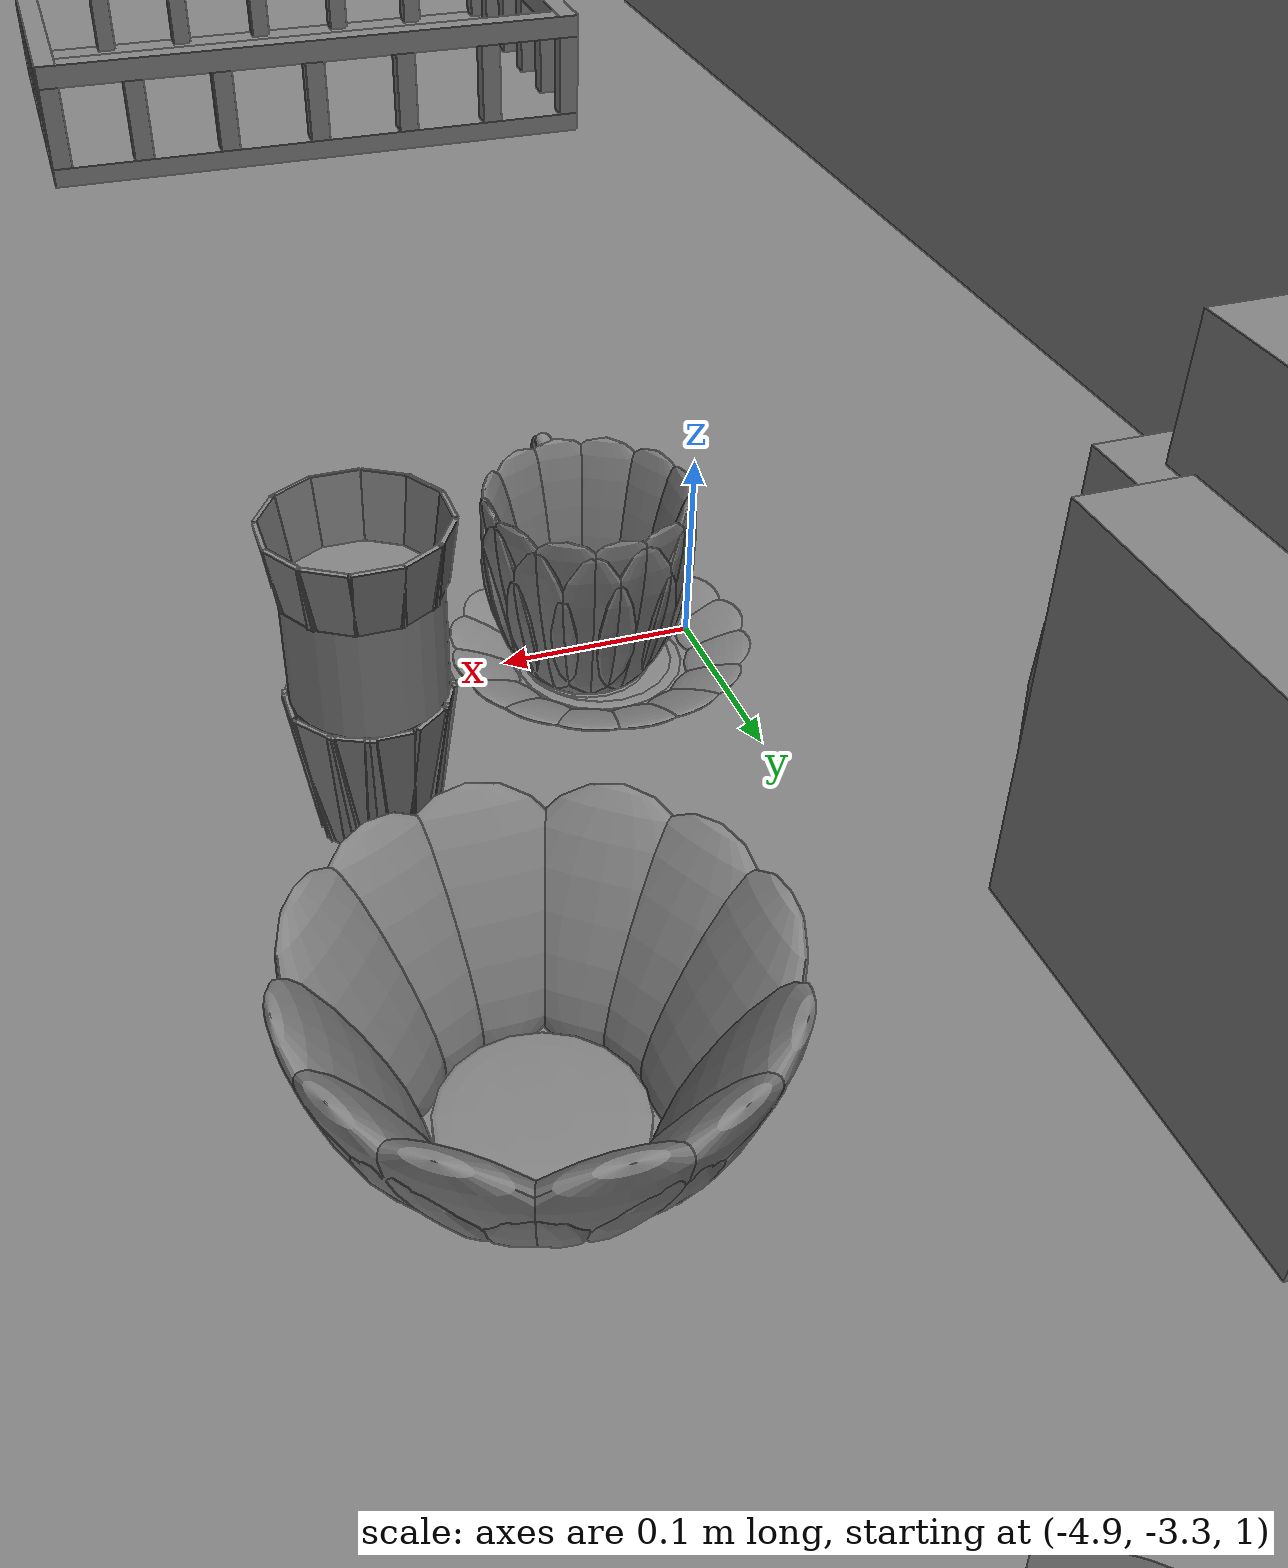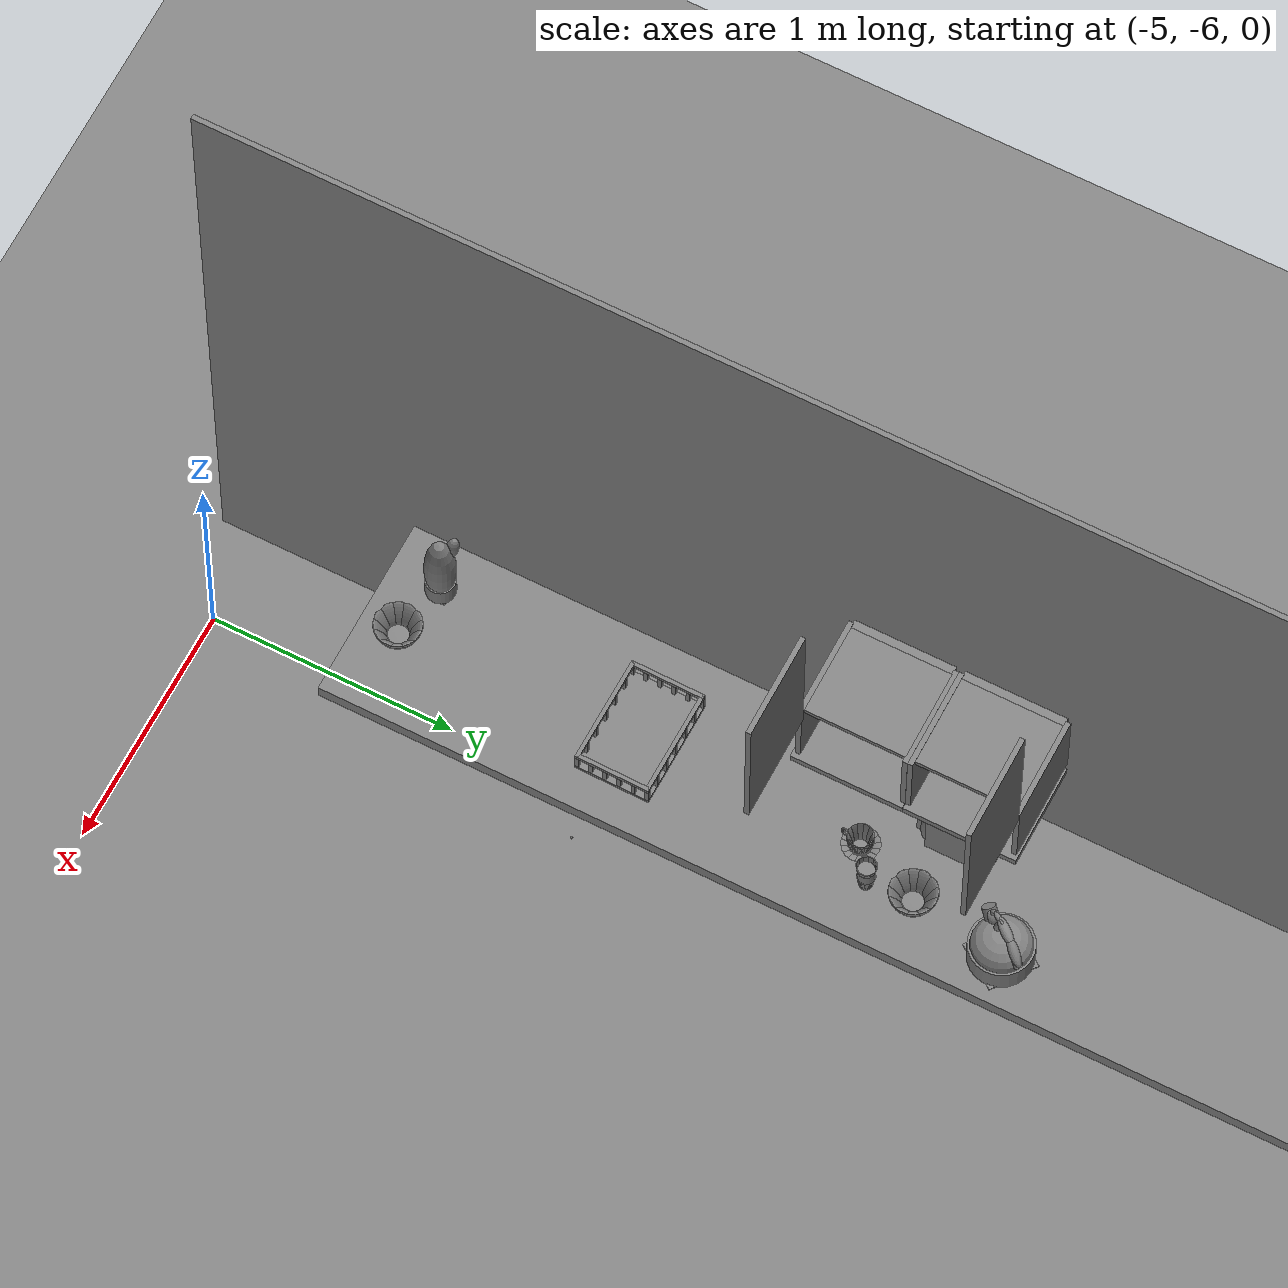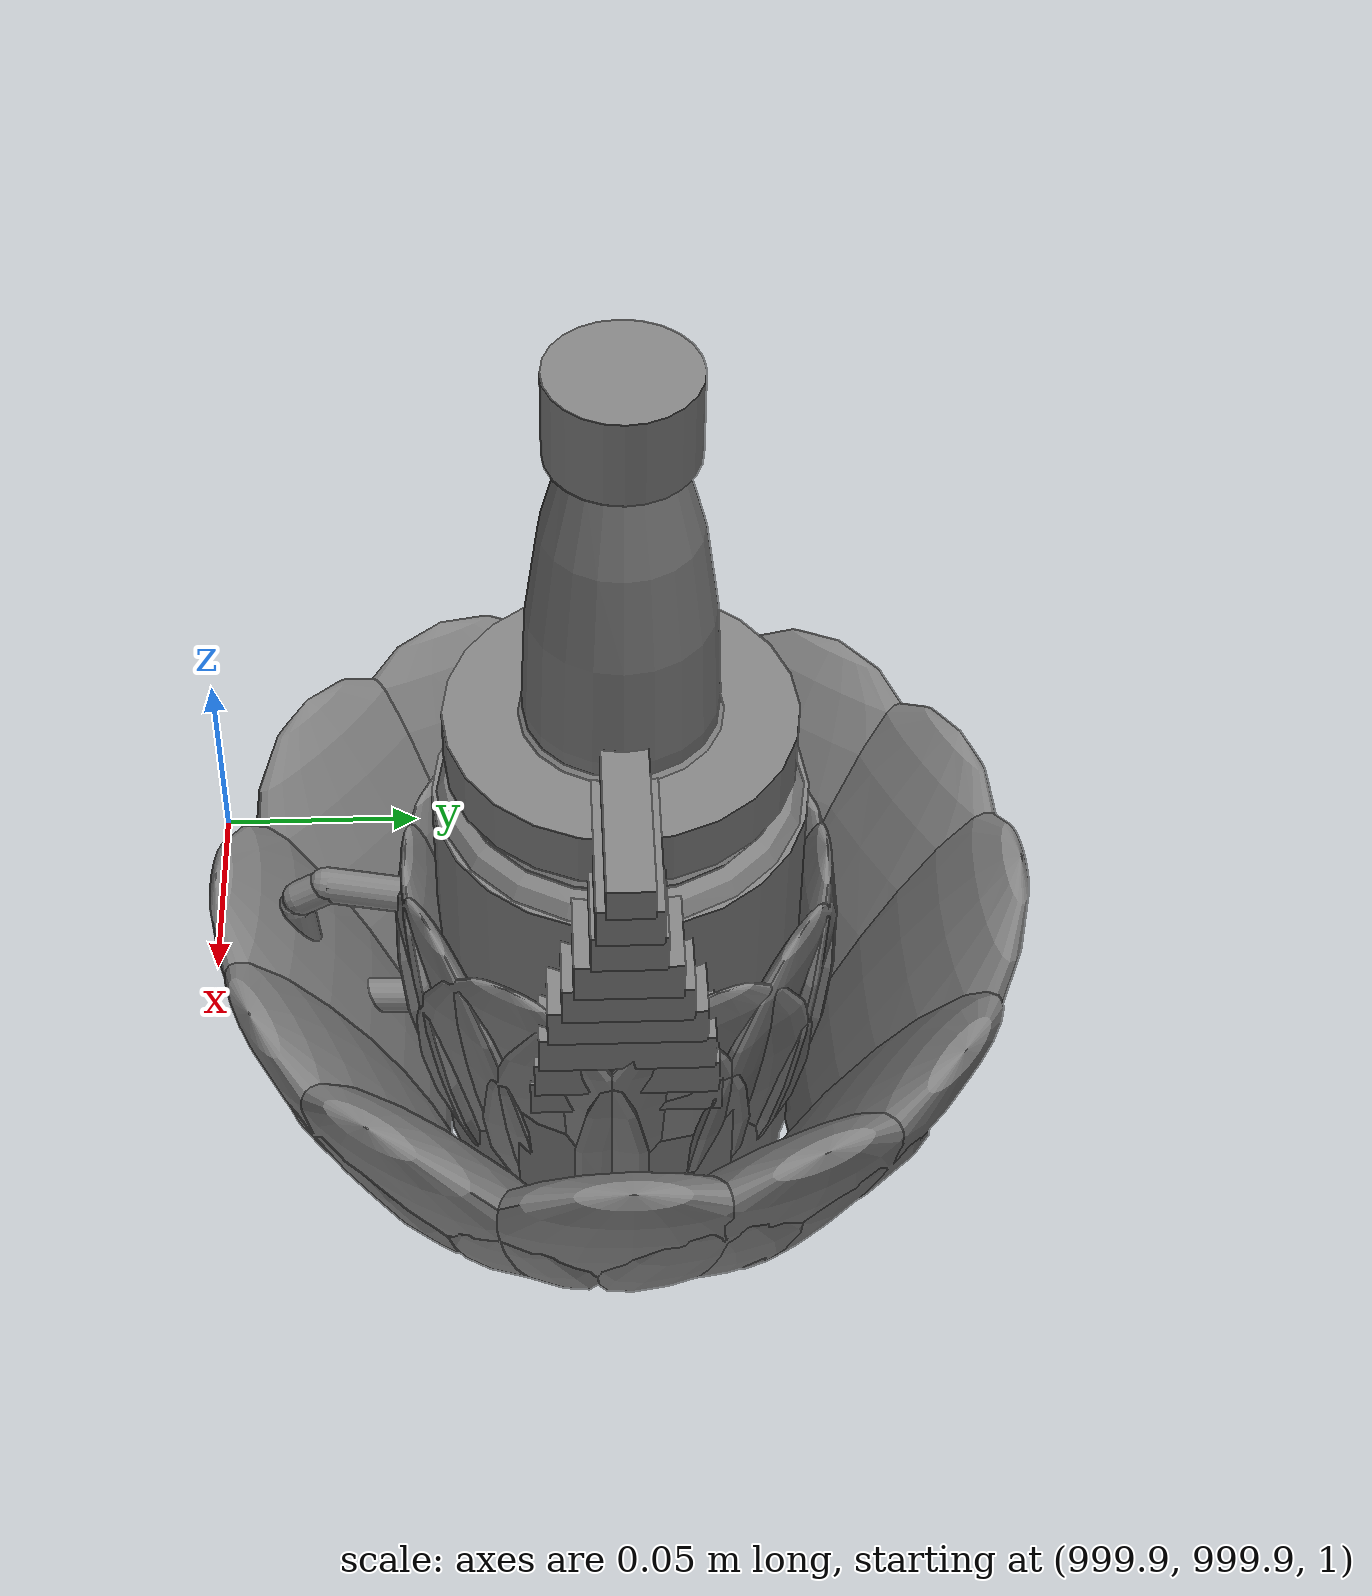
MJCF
<mujoco>
    <option gravity="0.000000000 0.000000000 -9.810000420" timestep="0.0049999999" integrator="implicitfast" density="9.8000002" viscosity="1.8000001e-05" noslip_iterations="10" iterations="100" sdf_iterations="50">
        <flag multiccd="disable"/>
    </option>
    <size memory="1000M"/>
    <compiler coordinate="local"/>
    <worldbody>
        <light cutoff="30" pos="0 1 1" dir="0 -1 -2"/>
        <light cutoff="30" pos="0 -1 1" dir="0 1 -2"/>
        <body pos="-5.046103477 -5.051773071 1.001502514" euler="0.000000000 0.000000000 0.000000000" name="Interactive Objcets_huapen">
            <geom contype="1" conaffinity="1" density="1000" type="ellipsoid" material="" rgba="0.500000000 0.500000000 0.500000000 1.000000000" solimp="0.899999976 0.949999988 0.001000000" friction="1.000000000 0.005000000 0.000100000" solref="0.020000000 1.000000000" margin="0" condim="3" group="0" pos="0.008062840 0.004346371 0.205056787" quat="1.000000000 0.000000000 0.000000000 0.000000000" size="0.059999999 0.059999999 0.180000007" name="Interactive Objcets_huapen_hua_4F478386_7C4C_4137_9655_6FDF3109524C"/>
            <geom contype="1" conaffinity="1" density="1000" type="cylinder" material="" rgba="0.500000000 0.500000000 0.500000000 1.000000000" solimp="0.899999976 0.949999988 0.001000000" friction="1.000000000 0.005000000 0.000100000" solref="0.020000000 1.000000000" margin="0" condim="3" group="0" pos="0.008062840 0.003952026 0.080107450" quat="1.000000000 0.000000000 0.000000000 0.000000000" size="0.057999998 0.039999999 1.000000000" name="Interactive Objcets_huapen_hua_C5D7F820_71C6_4CAE_ADA3_A156A898A0ED"/>
            <geom contype="1" conaffinity="1" density="1000" type="box" material="" rgba="0.500000000 0.500000000 0.500000000 1.000000000" solimp="0.899999976 0.949999988 0.001000000" friction="1.000000000 0.005000000 0.000100000" solref="0.020000000 1.000000000" margin="0" condim="3" group="0" pos="0.008062840 0.003952503 0.020566106" quat="1.000000000 0.000000000 0.000000000 0.000000000" size="0.035000000 0.035000000 0.020000000" name="Interactive Objcets_huapen_hua_4D28EA99_E8A3_4245_A04A_5B43EF9B7021"/>
            <geom contype="1" conaffinity="1" density="1000" type="ellipsoid" material="" rgba="0.500000000 0.500000000 0.500000000 1.000000000" solimp="0.899999976 0.949999988 0.001000000" friction="1.000000000 0.005000000 0.000100000" solref="0.020000000 1.000000000" margin="0" condim="3" group="0" pos="-0.029900074 0.033599377 0.321917295" quat="0.992658079 -0.083605267 -0.087364964 0.002748166" size="0.025000000 0.025000000 0.059999999" name="Interactive Objcets_huapen_hua_BFF9CBDE_4201_4827_80BD_D7D8BBA42B49"/>
            <freejoint name="Interactive Objcets_huapen"/>
        </body>
        <body pos="1000.000000000 1000.000000000 1.000000000" euler="0.000000000 0.000000000 0.000000000" name="openloong_gripper_2f85_fix_base_usda_bow_yellow_kps">
            <geom contype="1" conaffinity="1" density="1000" type="ellipsoid" material="" rgba="0.500000000 0.500000000 0.500000000 1.000000000" solimp="0.899999976 0.949999988 0.001000000" friction="1.000000000 0.005000000 0.000100000" solref="0.020000000 1.000000000" margin="0" condim="3" group="0" pos="-0.052185059 0.040283203 0.044118762" quat="0.919264615 -0.076883033 -0.225593656 -0.313287765" size="0.010000000 0.039999999 0.052000001" name="openloong_gripper_2f85_fix_base_usda_geom_2C0F07A5_C433_4AC4_90CE_91E6F23BF2FA"/>
            <geom contype="1" conaffinity="1" density="1000" type="ellipsoid" material="" rgba="0.500000000 0.500000000 0.500000000 1.000000000" solimp="0.899999976 0.949999988 0.001000000" friction="1.000000000 0.005000000 0.000100000" solref="0.020000000 1.000000000" margin="0" condim="3" group="0" pos="-0.000061035 0.065979004 0.044118762" quat="0.687598765 -0.168314874 -0.168741167 -0.685860336" size="0.010000000 0.039999999 0.052000001" name="openloong_gripper_2f85_fix_base_usda_geom_1843FD18_54F4_4FE5_A475_3A8BFCF9D3C2"/>
            <geom contype="1" conaffinity="1" density="1000" type="box" material="" rgba="0.500000000 0.500000000 0.500000000 1.000000000" solimp="0.899999976 0.949999988 0.001000000" friction="1.000000000 0.005000000 0.000100000" solref="0.020000000 1.000000000" margin="0" condim="3" group="0" pos="0.000061035 0.000000000 -0.002001643" quat="1.000000000 0.000000000 0.000000000 0.000000000" size="0.029999999 0.029999999 0.002000000" name="openloong_gripper_2f85_fix_base_usda_geom_F0BCD66A_145A_496C_9F03_DFC76636D558"/>
            <geom contype="1" conaffinity="1" density="1000" type="ellipsoid" material="" rgba="0.500000000 0.500000000 0.500000000 1.000000000" solimp="0.899999976 0.949999988 0.001000000" friction="1.000000000 0.005000000 0.000100000" solref="0.020000000 1.000000000" margin="0" condim="3" group="0" pos="0.029418945 -0.059082031 0.044118762" quat="0.825555861 0.125530601 0.202597082 -0.511521280" size="0.010000000 0.039999999 0.052000001" name="openloong_gripper_2f85_fix_base_usda_geom_66552EF8_DC09_4F35_BB80_DE3232106F3E"/>
            <geom contype="1" conaffinity="1" density="1000" type="ellipsoid" material="" rgba="0.500000000 0.500000000 0.500000000 1.000000000" solimp="0.899999976 0.949999988 0.001000000" friction="1.000000000 0.005000000 0.000100000" solref="0.020000000 1.000000000" margin="0" condim="3" group="0" pos="0.000244141 -0.065979004 0.044118762" quat="0.687598765 0.168314651 0.168741375 -0.685860336" size="0.010000000 0.039999999 0.052000001" name="openloong_gripper_2f85_fix_base_usda_geom_20621642_3A3C_4839_8A3D_78565F41F037"/>
            <geom contype="1" conaffinity="1" density="1000" type="ellipsoid" material="" rgba="0.500000000 0.500000000 0.500000000 1.000000000" solimp="0.899999976 0.949999988 0.001000000" friction="1.000000000 0.005000000 0.000100000" solref="0.020000000 1.000000000" margin="0" condim="3" group="0" pos="0.000061035 0.000000000 0.000446677" quat="1.000000000 0.000000000 0.000000000 0.000000000" size="0.039999999 0.039999999 0.002000000" name="openloong_gripper_2f85_fix_base_usda_geom_459C900A_9203_4B50_9BC6_00F18301A455"/>
            <geom contype="1" conaffinity="1" density="1000" type="ellipsoid" material="" rgba="0.500000000 0.500000000 0.500000000 1.000000000" solimp="0.899999976 0.949999988 0.001000000" friction="1.000000000 0.005000000 0.000100000" solref="0.020000000 1.000000000" margin="0" condim="3" group="0" pos="0.059082031 0.029541016 0.044118762" quat="0.223252773 -0.231952220 -0.054787423 -0.945174456" size="0.010000000 0.039999999 0.052000001" name="openloong_gripper_2f85_fix_base_usda_geom_B9C48B17_3F67_42F9_975D_9437DD4FD4DE"/>
            <geom contype="1" conaffinity="1" density="1000" type="ellipsoid" material="" rgba="0.500000000 0.500000000 0.500000000 1.000000000" solimp="0.899999976 0.949999988 0.001000000" friction="1.000000000 0.005000000 0.000100000" solref="0.020000000 1.000000000" margin="0" condim="3" group="0" pos="0.000061035 0.000000000 0.007335305" quat="1.000000000 0.000000000 0.000000000 0.000000000" size="0.039999999 0.039999999 0.002000000" name="openloong_gripper_2f85_fix_base_usda_geom_3DDF9301_EFF6_4278_9DEE_ECDB3FAD749D"/>
            <geom contype="1" conaffinity="1" density="1000" type="ellipsoid" material="" rgba="0.500000000 0.500000000 0.500000000 1.000000000" solimp="0.899999976 0.949999988 0.001000000" friction="1.000000000 0.005000000 0.000100000" solref="0.020000000 1.000000000" margin="0" condim="3" group="0" pos="-0.029296875 0.059082031 0.044118762" quat="0.825555861 -0.125530809 -0.202596918 -0.511521280" size="0.010000000 0.039999999 0.052000001" name="openloong_gripper_2f85_fix_base_usda_geom_CFFE97D3_D2A6_4C81_8448_6E08D06F0435"/>
            <geom contype="1" conaffinity="1" density="1000" type="ellipsoid" material="" rgba="0.500000000 0.500000000 0.500000000 1.000000000" solimp="0.899999976 0.949999988 0.001000000" friction="1.000000000 0.005000000 0.000100000" solref="0.020000000 1.000000000" margin="0" condim="3" group="0" pos="0.040222168 0.052368164 0.044118762" quat="0.429593176 -0.213750049 -0.105424821 -0.871002972" size="0.010000000 0.039999999 0.052000001" name="openloong_gripper_2f85_fix_base_usda_geom_BB946FC1_970E_4D4B_8997_7BA1E483BF26"/>
            <geom contype="1" conaffinity="1" density="1000" type="ellipsoid" material="" rgba="0.500000000 0.500000000 0.500000000 1.000000000" solimp="0.899999976 0.949999988 0.001000000" friction="1.000000000 0.005000000 0.000100000" solref="0.020000000 1.000000000" margin="0" condim="3" group="0" pos="0.066040039 0.000000000 0.044118762" quat="0.971183062 -0.000000156 0.238334835 0.000000030" size="0.010000000 0.039999999 0.052000001" name="openloong_gripper_2f85_fix_base_usda_geom_8C786353_E220_4AA3_914E_A9D995B1E1E6"/>
            <geom contype="1" conaffinity="1" density="1000" type="ellipsoid" material="" rgba="0.500000000 0.500000000 0.500000000 1.000000000" solimp="0.899999976 0.949999988 0.001000000" friction="1.000000000 0.005000000 0.000100000" solref="0.020000000 1.000000000" margin="0" condim="3" group="0" pos="0.052307129 -0.040283203 0.044118762" quat="0.919264674 0.076882750 0.225593731 -0.313287705" size="0.010000000 0.039999999 0.052000001" name="openloong_gripper_2f85_fix_base_usda_geom_BF96608E_8EB9_4DCF_9722_AEE520444452"/>
            <geom contype="1" conaffinity="1" density="1000" type="ellipsoid" material="" rgba="0.500000000 0.500000000 0.500000000 1.000000000" solimp="0.899999976 0.949999988 0.001000000" friction="1.000000000 0.005000000 0.000100000" solref="0.020000000 1.000000000" margin="0" condim="3" group="0" pos="-0.065917969 0.000000000 0.044118762" quat="0.971183062 -0.000000142 -0.238334835 0.000000030" size="0.010000000 0.039999999 0.052000001" name="openloong_gripper_2f85_fix_base_usda_geom_35EEB387_51F3_4F8F_93B2_3933D2ED5CFE"/>
            <geom contype="1" conaffinity="1" density="1000" type="ellipsoid" material="" rgba="0.500000000 0.500000000 0.500000000 1.000000000" solimp="0.899999976 0.949999988 0.001000000" friction="1.000000000 0.005000000 0.000100000" solref="0.020000000 1.000000000" margin="0" condim="3" group="0" pos="-0.058898926 -0.029541016 0.044118762" quat="0.223252758 0.231952101 0.054787733 -0.945174575" size="0.010000000 0.039999999 0.052000001" name="openloong_gripper_2f85_fix_base_usda_geom_E4B3A161_8868_4C15_9062_92704C9003D0"/>
            <geom contype="1" conaffinity="1" density="1000" type="ellipsoid" material="" rgba="0.500000000 0.500000000 0.500000000 1.000000000" solimp="0.899999976 0.949999988 0.001000000" friction="1.000000000 0.005000000 0.000100000" solref="0.020000000 1.000000000" margin="0" condim="3" group="0" pos="-0.040100098 -0.052368164 0.044118762" quat="0.429593235 0.213749886 0.105425082 -0.871003032" size="0.010000000 0.039999999 0.052000001" name="openloong_gripper_2f85_fix_base_usda_geom_92A30279_C1BB_43AB_AD2A_85C872F49A87"/>
            <freejoint name="openloong_gripper_2f85_fix_base_usda_bow_yellow_kps_joint"/>
            <site size="0.005000000 0.005000000 0.005000000" rgba="0.500000000 0.500000000 0.500000000 1.000000000" pos="0.000000000 0.000000000 0.000000000" quat="0.999961913 0.008726534 0.000000000 0.000000000" group="0" type="sphere" name="openloong_gripper_2f85_fix_base_usda_bow_yellow_kps"/>
        </body>
        <body pos="1000.000000000 1000.000000000 1.000000000" euler="0.000000000 0.000000000 0.000000000" name="openloong_gripper_2f85_fix_base_usda_bottle_red">
            <geom contype="1" conaffinity="1" density="1000" type="ellipsoid" material="" rgba="0.500000000 0.500000000 0.500000000 1.000000000" solimp="0.899999976 0.949999988 0.001000000" friction="1.000000000 0.005000000 0.000100000" solref="0.020000000 1.000000000" margin="0" condim="3" group="0" pos="0.000000000 0.000000000 0.144284487" quat="1.000000000 0.000000000 0.000000000 0.000000000" size="0.021000000 0.021000000 0.079999998" name="openloong_gripper_2f85_fix_base_usda_geom_BFAA3F43_CB44_4DD9_9F34_FA84A9335738"/>
            <geom contype="1" conaffinity="1" density="1000" type="cylinder" material="" rgba="0.500000000 0.500000000 0.500000000 1.000000000" solimp="0.899999976 0.949999988 0.001000000" friction="1.000000000 0.005000000 0.000100000" solref="0.020000000 1.000000000" margin="0" condim="3" group="0" pos="0.000000000 0.000000000 0.220618963" quat="1.000000000 0.000000000 0.000000000 0.000000000" size="0.016000001 0.010000000 1.000000000" name="openloong_gripper_2f85_fix_base_usda_geom_7D0B348A_0896_4C95_818A_59DF9B41B774"/>
            <geom contype="1" conaffinity="1" density="1000" type="ellipsoid" material="" rgba="0.500000000 0.500000000 0.500000000 1.000000000" solimp="0.899999976 0.949999988 0.001000000" friction="1.000000000 0.005000000 0.000100000" solref="0.020000000 1.000000000" margin="0" condim="3" group="0" pos="0.000000000 0.000000000 0.118945479" quat="1.000000000 0.000000000 0.000000000 0.000000000" size="0.030999999 0.030999999 0.029999999" name="openloong_gripper_2f85_fix_base_usda_geom_84BA130F_C40D_48A8_AE7E_972B241E25D3"/>
            <geom contype="1" conaffinity="1" density="1000" type="box" material="" rgba="0.500000000 0.500000000 0.500000000 1.000000000" solimp="0.899999976 0.949999988 0.001000000" friction="1.000000000 0.005000000 0.000100000" solref="0.020000000 1.000000000" margin="0" condim="3" group="0" pos="0.000000000 0.000000000 0.002189159" quat="1.000000000 0.000000000 0.000000000 0.000000000" size="0.020000000 0.020000000 0.003000000" name="openloong_gripper_2f85_fix_base_usda_geom_E523E144_00D4_423D_8064_1BDCD60EAB1F"/>
            <geom contype="1" conaffinity="1" density="1000" type="cylinder" material="" rgba="0.500000000 0.500000000 0.500000000 1.000000000" solimp="0.899999976 0.949999988 0.001000000" friction="1.000000000 0.005000000 0.000100000" solref="0.020000000 1.000000000" margin="0" condim="3" group="0" pos="0.000000000 -0.000366211 0.060884237" quat="1.000000000 0.000000000 0.000000000 0.000000000" size="0.030999999 0.057999998 1.000000000" name="openloong_gripper_2f85_fix_base_usda_geom_CF88D6FC_EB1E_4815_BD7B_836EED1ED571"/>
            <freejoint name="openloong_gripper_2f85_fix_base_usda_bottle_red_joint"/>
            <site size="0.005000000 0.005000000 0.005000000" rgba="0.500000000 0.500000000 0.500000000 1.000000000" pos="0.000000000 0.000000000 0.000000000" quat="0.999961913 0.008726535 0.000000000 0.000000000" group="0" type="sphere" name="openloong_gripper_2f85_fix_base_usda_bottle_redsite"/>
        </body>
        <body pos="-4.189439297 -4.394554138 1.917669415" euler="-63.923477173 -5.972087860 -157.387237549" mocap="true" name="spotlight1_SpotLight"/>
        <body pos="-4.197558880 -3.789601564 1.764804959" euler="-116.395103455 -41.780975342 -82.384201050" mocap="true" name="spotlight4_SpotLight"/>
        <body pos="1000.000000000 1000.000000000 1.000000000" euler="0.000000000 0.000000000 0.000000000" name="openloong_gripper_2f85_fix_base_usda_salt">
            <geom contype="1" conaffinity="1" density="1000" type="box" material="" rgba="0.500000000 0.500000000 0.500000000 1.000000000" solimp="0.899999976 0.949999988 0.001000000" friction="1.000000000 0.005000000 0.000100000" solref="0.020000000 1.000000000" margin="0" condim="3" group="0" pos="0.000305176 0.000000000 0.084862232" quat="1.000000000 0.000000000 0.000000000 0.000000000" size="0.048999999 0.018999999 0.005000000" name="openloong_gripper_2f85_fix_base_usda_geom_4A04ACA6_597F_4E07_869A_0B330DD25461"/>
            <geom contype="1" conaffinity="1" density="1000" type="box" material="" rgba="0.500000000 0.500000000 0.500000000 1.000000000" solimp="0.899999976 0.949999988 0.001000000" friction="1.000000000 0.005000000 0.000100000" solref="0.020000000 1.000000000" margin="0" condim="3" group="0" pos="0.000305176 0.000000000 0.104564309" quat="1.000000000 0.000000000 0.000000000 0.000000000" size="0.052000001 0.014000000 0.005000000" name="openloong_gripper_2f85_fix_base_usda_geom_4EDA5654_AFDE_4A73_BBFE_CB1F01449EB7"/>
            <geom contype="1" conaffinity="1" density="1000" type="box" material="" rgba="0.500000000 0.500000000 0.500000000 1.000000000" solimp="0.899999976 0.949999988 0.001000000" friction="1.000000000 0.005000000 0.000100000" solref="0.020000000 1.000000000" margin="0" condim="3" group="0" pos="0.000305176 0.000000000 0.114487171" quat="1.000000000 0.000000000 0.000000000 0.000000000" size="0.054000001 0.011500000 0.005000000" name="openloong_gripper_2f85_fix_base_usda_geom_9DA35F2A_B784_44BE_B16F_E9990D28E9CA"/>
            <geom contype="1" conaffinity="1" density="1000" type="box" material="" rgba="0.500000000 0.500000000 0.500000000 1.000000000" solimp="0.899999976 0.949999988 0.001000000" friction="1.000000000 0.005000000 0.000100000" solref="0.020000000 1.000000000" margin="0" condim="3" group="0" pos="0.000305176 0.000000000 0.075103164" quat="1.000000000 0.000000000 0.000000000 0.000000000" size="0.048000000 0.020000000 0.005000000" name="openloong_gripper_2f85_fix_base_usda_geom_E319A791_1B30_4976_86DA_188F012AF8DB"/>
            <geom contype="1" conaffinity="1" density="1000" type="box" material="" rgba="0.500000000 0.500000000 0.500000000 1.000000000" solimp="0.899999976 0.949999988 0.001000000" friction="1.000000000 0.005000000 0.000100000" solref="0.020000000 1.000000000" margin="0" condim="3" group="0" pos="0.000305176 0.000000000 0.134892464" quat="1.000000000 0.000000000 0.000000000 0.000000000" size="0.057000000 0.007000000 0.005000000" name="openloong_gripper_2f85_fix_base_usda_geom_CDAC5AF9_86ED_4C44_890B_FCFCD9A28254"/>
            <geom contype="1" conaffinity="1" density="1000" type="box" material="" rgba="0.500000000 0.500000000 0.500000000 1.000000000" solimp="0.899999976 0.949999988 0.001000000" friction="1.000000000 0.005000000 0.000100000" solref="0.020000000 1.000000000" margin="0" condim="3" group="0" pos="0.000305176 0.000000000 0.094920278" quat="1.000000000 0.000000000 0.000000000 0.000000000" size="0.050000001 0.017000001 0.005000000" name="openloong_gripper_2f85_fix_base_usda_geom_FB62ABA6_1CEA_4DB2_9621_7CC57C18CC0C"/>
            <geom contype="1" conaffinity="1" density="1000" type="box" material="" rgba="0.500000000 0.500000000 0.500000000 1.000000000" solimp="0.899999976 0.949999988 0.001000000" friction="1.000000000 0.005000000 0.000100000" solref="0.020000000 1.000000000" margin="0" condim="3" group="0" pos="0.000305176 0.000000000 0.065204859" quat="1.000000000 0.000000000 0.000000000 0.000000000" size="0.045000002 0.021000000 0.005000000" name="openloong_gripper_2f85_fix_base_usda_geom_887E2291_B390_4682_8053_1EA318D1C8CC"/>
            <geom contype="1" conaffinity="1" density="1000" type="box" material="" rgba="0.500000000 0.500000000 0.500000000 1.000000000" solimp="0.899999976 0.949999988 0.001000000" friction="1.000000000 0.005000000 0.000100000" solref="0.020000000 1.000000000" margin="0" condim="3" group="0" pos="0.000305176 0.000000000 0.144135714" quat="1.000000000 0.000000000 0.000000000 0.000000000" size="0.059000000 0.005000000 0.004000000" name="openloong_gripper_2f85_fix_base_usda_geom_5441128B_1E72_443C_AE07_DA610716474C"/>
            <geom contype="1" conaffinity="1" density="1000" type="box" material="" rgba="0.500000000 0.500000000 0.500000000 1.000000000" solimp="0.899999976 0.949999988 0.001000000" friction="1.000000000 0.005000000 0.000100000" solref="0.020000000 1.000000000" margin="0" condim="3" group="0" pos="0.000000000 0.000000000 0.031593561" quat="1.000000000 0.000000000 0.000000000 0.000000000" size="0.041999999 0.024000000 0.029999999" name="openloong_gripper_2f85_fix_base_usda_geom_3EFE0316_281C_4FC7_B920_B7E1461645B8"/>
            <geom contype="1" conaffinity="1" density="1000" type="box" material="" rgba="0.500000000 0.500000000 0.500000000 1.000000000" solimp="0.899999976 0.949999988 0.001000000" friction="1.000000000 0.005000000 0.000100000" solref="0.020000000 1.000000000" margin="0" condim="3" group="0" pos="0.000305176 0.000000000 0.124608755" quat="1.000000000 0.000000000 0.000000000 0.000000000" size="0.055000000 0.008000000 0.005000000" name="openloong_gripper_2f85_fix_base_usda_geom_122F490F_94BD_4FC1_9DCD_871F7FE16BF2"/>
            <freejoint name="openloong_gripper_2f85_fix_base_usda_salt_joint"/>
            <site size="0.005000000 0.005000000 0.005000000" rgba="0.500000000 0.500000000 0.500000000 1.000000000" pos="0.000000000 0.000000000 0.000000000" quat="1.000000000 0.000000000 0.000000000 0.000000000" group="0" type="sphere" name="openloong_gripper_2f85_fix_base_usda_saltsite"/>
        </body>
        <body pos="1000.000000000 1000.000000000 1.000000000" euler="0.000000000 0.000000000 0.000000000" name="openloong_gripper_2f85_fix_base_usda_jar_01">
            <geom contype="1" conaffinity="1" density="1000" type="box" material="" rgba="0.500000000 0.500000000 0.500000000 1.000000000" solimp="0.899999976 0.949999988 0.001000000" friction="1.000000000 0.005000000 0.000100000" solref="0.020000000 1.000000000" margin="0" condim="3" group="0" pos="0.000000000 0.000000000 0.006158113" quat="1.000000000 0.000000000 0.000000000 0.000000000" size="0.020000000 0.020000000 0.005000000" name="openloong_gripper_2f85_fix_base_usda_geom_135DCF63_B579_4671_9CCB_CBF76B569746"/>
            <geom contype="1" conaffinity="1" density="1000" type="cylinder" material="" rgba="0.500000000 0.500000000 0.500000000 1.000000000" solimp="0.899999976 0.949999988 0.001000000" friction="1.000000000 0.005000000 0.000100000" solref="0.020000000 1.000000000" margin="0" condim="3" group="0" pos="0.000000000 0.000000000 0.062744498" quat="1.000000000 0.000000000 0.000000000 0.000000000" size="0.041000001 0.052999999 1.000000000" name="openloong_gripper_2f85_fix_base_usda_geom_834B4E09_AF91_4DF9_919A_E0287984D106"/>
            <geom contype="1" conaffinity="1" density="1000" type="ellipsoid" material="" rgba="0.500000000 0.500000000 0.500000000 1.000000000" solimp="0.899999976 0.949999988 0.001000000" friction="1.000000000 0.005000000 0.000100000" solref="0.020000000 1.000000000" margin="0" condim="3" group="0" pos="0.000000000 0.000000000 0.122252703" quat="1.000000000 0.000000000 0.000000000 0.000000000" size="0.035999998 0.035999998 0.010000000" name="openloong_gripper_2f85_fix_base_usda_geom_2879A69C_D67B_4C4C_A48C_D8D6D5F42F8F"/>
            <geom contype="1" conaffinity="1" density="1000" type="cylinder" material="" rgba="0.500000000 0.500000000 0.500000000 1.000000000" solimp="0.899999976 0.949999988 0.001000000" friction="1.000000000 0.005000000 0.000100000" solref="0.020000000 1.000000000" margin="0" condim="3" group="0" pos="0.000000000 0.000000000 0.015747190" quat="1.000000000 0.000000000 0.000000000 0.000000000" size="0.035000000 0.010000000 1.000000000" name="openloong_gripper_2f85_fix_base_usda_geom_77A13D3A_54CB_493E_B269_566FCFD13365"/>
            <geom contype="1" conaffinity="1" density="1000" type="ellipsoid" material="" rgba="0.500000000 0.500000000 0.500000000 1.000000000" solimp="0.899999976 0.949999988 0.001000000" friction="1.000000000 0.005000000 0.000100000" solref="0.020000000 1.000000000" margin="0" condim="3" group="0" pos="0.000000000 0.000000000 0.115815401" quat="1.000000000 0.000000000 0.000000000 0.000000000" size="0.039999999 0.039999999 0.010000000" name="openloong_gripper_2f85_fix_base_usda_geom_D5AFF6F6_6286_421F_8CED_732A67CD8ED8"/>
            <geom contype="1" conaffinity="1" density="1000" type="cylinder" material="" rgba="0.500000000 0.500000000 0.500000000 1.000000000" solimp="0.899999976 0.949999988 0.001000000" friction="1.000000000 0.005000000 0.000100000" solref="0.020000000 1.000000000" margin="0" condim="3" group="0" pos="0.000000000 0.000000000 0.133183479" quat="1.000000000 0.000000000 0.000000000 0.000000000" size="0.037999999 0.006500000 1.000000000" name="openloong_gripper_2f85_fix_base_usda_geom_F9D6C889_9AA9_48D4_A8EC_7E9BC439A9CB"/>
            <freejoint name="openloong_gripper_2f85_fix_base_usda_jar_01_joint"/>
            <site size="0.005000000 0.005000000 0.005000000" rgba="0.500000000 0.500000000 0.500000000 1.000000000" pos="0.000000000 0.000000000 0.000000000" quat="1.000000000 0.000000000 0.000000000 0.000000000" group="0" type="sphere" name="openloong_gripper_2f85_fix_base_usda_jar_01site"/>
        </body>
        <body pos="-4.449879169 -3.939762354 1.789191008" euler="137.346237183 -18.253822327 86.369430542" mocap="true" name="spotlight5_SpotLight"/>
        <body pos="1000.000000000 1000.000000000 1.000000000" euler="0.000000000 0.000000000 0.000000000" name="openloong_gripper_2f85_fix_base_usda_coffeecup_white_kps">
            <geom contype="1" conaffinity="1" density="1000" type="capsule" material="" rgba="0.500000000 0.500000000 0.500000000 1.000000000" solimp="0.899999976 0.949999988 0.001000000" friction="1.000000000 0.005000000 0.000100000" solref="0.020000000 1.000000000" margin="0" condim="3" group="0" pos="-0.000854492 -0.065795898 0.050029993" quat="0.343559504 -0.613204718 0.626912475 0.336047262" size="0.004000000 0.005000000 1.000000000" name="openloong_gripper_2f85_fix_base_usda_geom_0B9A57C8_FAF3_40DF_AFE4_6AD35604E243"/>
            <geom contype="1" conaffinity="1" density="1000" type="ellipsoid" material="" rgba="0.500000000 0.500000000 0.500000000 1.000000000" solimp="0.899999976 0.949999988 0.001000000" friction="1.000000000 0.005000000 0.000100000" solref="0.020000000 1.000000000" margin="0" condim="3" group="0" pos="-0.000793457 -0.038452148 0.048040152" quat="0.711656272 0.066323131 -0.067805752 0.696095467" size="0.005000000 0.029999999 0.048999999" name="openloong_gripper_2f85_fix_base_usda_geom_CE47F39A_94DF_4F11_AC07_5BB17E392696"/>
            <geom contype="1" conaffinity="1" density="1000" type="ellipsoid" material="" rgba="0.500000000 0.500000000 0.500000000 1.000000000" solimp="0.899999976 0.949999988 0.001000000" friction="1.000000000 0.005000000 0.000100000" solref="0.020000000 1.000000000" margin="0" condim="3" group="0" pos="0.037719727 -0.001892090 0.048040152" quat="0.995387912 0.001371633 0.094835162 -0.014391154" size="0.005000000 0.029999999 0.048999999" name="openloong_gripper_2f85_fix_base_usda_geom_13989E02_4C8C_4DEE_8213_37E2C1242B61"/>
            <geom contype="1" conaffinity="1" density="1000" type="ellipsoid" material="" rgba="0.500000000 0.500000000 0.500000000 1.000000000" solimp="0.899999976 0.949999988 0.001000000" friction="1.000000000 0.005000000 0.000100000" solref="0.020000000 1.000000000" margin="0" condim="3" group="0" pos="0.033996582 0.015502930 0.048040152" quat="0.970659733 -0.021051638 0.092478797 0.220962167" size="0.005000000 0.029999999 0.048999999" name="openloong_gripper_2f85_fix_base_usda_geom_3F0963E7_26EF_4BB4_AAE5_D9EDA6E7B44D"/>
            <geom contype="1" conaffinity="1" density="1000" type="box" material="" rgba="0.500000000 0.500000000 0.500000000 1.000000000" solimp="0.899999976 0.949999988 0.001000000" friction="1.000000000 0.005000000 0.000100000" solref="0.020000000 1.000000000" margin="0" condim="3" group="0" pos="0.000793457 -0.000183105 0.000156164" quat="0.714879215 0.000000000 0.000000000 0.699247897" size="0.020000000 0.020000000 0.002000000" name="openloong_gripper_2f85_fix_base_usda_geom_B7080EAA_F69F_4F3D_A59C_798BB4E6A05E"/>
            <geom contype="1" conaffinity="1" density="1000" type="ellipsoid" material="" rgba="0.500000000 0.500000000 0.500000000 1.000000000" solimp="0.899999976 0.949999988 0.001000000" friction="1.000000000 0.005000000 0.000100000" solref="0.020000000 1.000000000" margin="0" condim="3" group="0" pos="-0.019409180 -0.033081055 0.048040152" quat="0.866879702 0.046630561 -0.082595348 0.489411235" size="0.005000000 0.029999999 0.048999999" name="openloong_gripper_2f85_fix_base_usda_geom_74BBDEBD_339A_417E_8E6A_A93444C83BF3"/>
            <geom contype="1" conaffinity="1" density="1000" type="ellipsoid" material="" rgba="0.500000000 0.500000000 0.500000000 1.000000000" solimp="0.899999976 0.949999988 0.001000000" friction="1.000000000 0.005000000 0.000100000" solref="0.020000000 1.000000000" margin="0" condim="3" group="0" pos="-0.016052246 0.033264160 0.048040152" quat="0.840792537 -0.050782297 -0.080109790 -0.532983541" size="0.005000000 0.029999999 0.048999999" name="openloong_gripper_2f85_fix_base_usda_geom_A88BB7D3_DD9D_463F_A3EA_71CB68B7B4CC"/>
            <geom contype="1" conaffinity="1" density="1000" type="capsule" material="" rgba="0.500000000 0.500000000 0.500000000 1.000000000" solimp="0.899999976 0.949999988 0.001000000" friction="1.000000000 0.005000000 0.000100000" solref="0.020000000 1.000000000" margin="0" condim="3" group="0" pos="-0.000549316 -0.053527832 0.046825886" quat="0.505496025 -0.494442940 0.505495846 0.494442940" size="0.004000000 0.005000000 1.000000000" name="openloong_gripper_2f85_fix_base_usda_geom_24DCD668_FA7A_4C36_9929_3BE9F02495DB"/>
            <geom contype="1" conaffinity="1" density="1000" type="ellipsoid" material="" rgba="0.500000000 0.500000000 0.500000000 1.000000000" solimp="0.899999976 0.949999988 0.001000000" friction="1.000000000 0.005000000 0.000100000" solref="0.020000000 1.000000000" margin="0" condim="3" group="0" pos="-0.032104492 0.018920898 0.048040152" quat="0.958129764 -0.025742561 -0.091288343 -0.270168930" size="0.005000000 0.029999999 0.048999999" name="openloong_gripper_2f85_fix_base_usda_geom_4ACD53D0_4D91_4E2F_A424_BDA0963B51EC"/>
            <geom contype="1" conaffinity="1" density="1000" type="ellipsoid" material="" rgba="0.500000000 0.500000000 0.500000000 1.000000000" solimp="0.899999976 0.949999988 0.001000000" friction="1.000000000 0.005000000 0.000100000" solref="0.020000000 1.000000000" margin="0" condim="3" group="0" pos="-0.037597656 0.000305176 0.048040152" quat="0.995387554 -0.001371440 -0.094839431 -0.014389008" size="0.005000000 0.029999999 0.048999999" name="openloong_gripper_2f85_fix_base_usda_geom_72D74154_D28E_406F_A727_0993B150AD7D"/>
            <geom contype="1" conaffinity="1" density="1000" type="capsule" material="" rgba="0.500000000 0.500000000 0.500000000 1.000000000" solimp="0.899999976 0.949999988 0.001000000" friction="1.000000000 0.005000000 0.000100000" solref="0.020000000 1.000000000" margin="0" condim="3" group="0" pos="-0.000366211 -0.043762207 0.044118762" quat="0.260488123 -0.651174724 0.665731549 0.254792154" size="0.004000000 0.003000000 1.000000000" name="openloong_gripper_2f85_fix_base_usda_geom_4A6A2D03_C1FD_43A4_A584_45528B7A66D2"/>
            <geom contype="1" conaffinity="1" density="1000" type="capsule" material="" rgba="0.500000000 0.500000000 0.500000000 1.000000000" solimp="0.899999976 0.949999988 0.001000000" friction="1.000000000 0.005000000 0.000100000" solref="0.020000000 1.000000000" margin="0" condim="3" group="0" pos="-0.000915527 -0.068542480 0.082936406" quat="0.624995589 -0.339446366 0.347034454 0.611329615" size="0.004000000 0.004000000 1.000000000" name="openloong_gripper_2f85_fix_base_usda_geom_EBF75A76_425C_45B3_B524_20D0E4496506"/>
            <geom contype="1" conaffinity="1" density="1000" type="ellipsoid" material="" rgba="0.500000000 0.500000000 0.500000000 1.000000000" solimp="0.899999976 0.949999988 0.001000000" friction="1.000000000 0.005000000 0.000100000" solref="0.020000000 1.000000000" margin="0" condim="3" group="0" pos="0.016113281 -0.034851074 0.048040152" quat="0.840793252 0.050779939 0.080106191 -0.532983422" size="0.005000000 0.029999999 0.048999999" name="openloong_gripper_2f85_fix_base_usda_geom_C9B7DEB2_33A6_44C7_A32E_3863018DCA56"/>
            <geom contype="1" conaffinity="1" density="1000" type="ellipsoid" material="" rgba="0.500000000 0.500000000 0.500000000 1.000000000" solimp="0.899999976 0.949999988 0.001000000" friction="1.000000000 0.005000000 0.000100000" solref="0.020000000 1.000000000" margin="0" condim="3" group="0" pos="0.000854492 0.036865234 0.048040152" quat="0.711656570 -0.066320375 0.067802906 0.696095705" size="0.005000000 0.029999999 0.048999999" name="openloong_gripper_2f85_fix_base_usda_geom_C8A0BCCB_05F6_424E_B23A_54C356BA1034"/>
            <geom contype="1" conaffinity="1" density="1000" type="ellipsoid" material="" rgba="0.500000000 0.500000000 0.500000000 1.000000000" solimp="0.899999976 0.949999988 0.001000000" friction="1.000000000 0.005000000 0.000100000" solref="0.020000000 1.000000000" margin="0" condim="3" group="0" pos="-0.033935547 -0.017089844 0.048040152" quat="0.970659137 0.021052625 -0.092483103 0.220962465" size="0.005000000 0.029999999 0.048999999" name="openloong_gripper_2f85_fix_base_usda_geom_8931B827_B274_40A2_88B5_4D9BE0A6B8E5"/>
            <geom contype="1" conaffinity="1" density="1000" type="ellipsoid" material="" rgba="0.500000000 0.500000000 0.500000000 1.000000000" solimp="0.899999976 0.949999988 0.001000000" friction="1.000000000 0.005000000 0.000100000" solref="0.020000000 1.000000000" margin="0" condim="3" group="0" pos="0.019531250 0.031494141 0.048040152" quat="0.866880119 -0.046628602 0.082591817 0.489411235" size="0.005000000 0.029999999 0.048999999" name="openloong_gripper_2f85_fix_base_usda_geom_2C6F207D_4A1F_44FB_BDAC_B2741A8DFFFE"/>
            <geom contype="1" conaffinity="1" density="1000" type="ellipsoid" material="" rgba="0.500000000 0.500000000 0.500000000 1.000000000" solimp="0.899999976 0.949999988 0.001000000" friction="1.000000000 0.005000000 0.000100000" solref="0.020000000 1.000000000" margin="0" condim="3" group="0" pos="0.032165527 -0.020507812 0.048040152" quat="0.958128154 0.025740955 0.091285400 -0.270175666" size="0.005000000 0.029999999 0.048999999" name="openloong_gripper_2f85_fix_base_usda_geom_3253146F_A883_40A0_A85D_45F1DE00BC3C"/>
            <geom contype="1" conaffinity="1" density="1000" type="capsule" material="" rgba="0.500000000 0.500000000 0.500000000 1.000000000" solimp="0.899999976 0.949999988 0.001000000" friction="1.000000000 0.005000000 0.000100000" solref="0.020000000 1.000000000" margin="0" condim="3" group="0" pos="-0.000610352 -0.056823730 0.083572865" quat="0.452654332 -0.541215360 0.553313971 0.442756712" size="0.004000000 0.009000000 1.000000000" name="openloong_gripper_2f85_fix_base_usda_geom_C98715F6_FEAD_4939_82A2_7D3D78CB37FE"/>
            <geom contype="1" conaffinity="1" density="1000" type="ellipsoid" material="" rgba="0.500000000 0.500000000 0.500000000 1.000000000" solimp="0.899999976 0.949999988 0.001000000" friction="1.000000000 0.005000000 0.000100000" solref="0.020000000 1.000000000" margin="0" condim="3" group="0" pos="0.000061035 -0.000183105 0.001848221" quat="0.714879215 0.000000000 0.000000000 0.699247897" size="0.029999999 0.029999999 0.001000000" name="openloong_gripper_2f85_fix_base_usda_geom_D977FDB4_0108_4C38_A335_881D86430C1F"/>
            <geom contype="1" conaffinity="1" density="1000" type="capsule" material="" rgba="0.500000000 0.500000000 0.500000000 1.000000000" solimp="0.899999976 0.949999988 0.001000000" friction="1.000000000 0.005000000 0.000100000" solref="0.020000000 1.000000000" margin="0" condim="3" group="0" pos="-0.000976562 -0.071838379 0.066101432" quat="0.031849027 -0.698553741 0.714169443 0.031152546" size="0.004000000 0.012000000 1.000000000" name="openloong_gripper_2f85_fix_base_usda_geom_7FA14965_152D_41F0_9401_4F4D8B3E294B"/>
            <freejoint name="openloong_gripper_2f85_fix_base_usda_coffeecup_white_kps_joint"/>
            <site size="0.005000000 0.005000000 0.005000000" rgba="0.500000000 0.500000000 0.500000000 1.000000000" pos="0.000000000 0.000000000 0.000000000" quat="0.999961913 0.008726534 0.000000000 0.000000000" group="0" type="sphere" name="openloong_gripper_2f85_fix_base_usda_coffeecup_white_kps"/>
        </body>
        <body pos="0.000000000 0.000000000 0.000000000" euler="0.000000000 0.000000000 0.000000000" name="Static Objcets_Static Objcets">
            <geom contype="1" conaffinity="1" density="1000" type="box" material="" rgba="0.500000000 0.500000000 0.500000000 1.000000000" solimp="0.899999976 0.949999988 0.001000000" friction="1.000000000 0.005000000 0.000100000" solref="0.020000000 1.000000000" margin="0" condim="3" group="0" pos="-4.999745846 -3.497932911 1.764780521" quat="0.707107067 0.707106471 0.000000000 0.000000000" size="0.200000003 0.159999996 0.010000000" name="Static Objcets_geom_F0C52AE3_E76E_401E_AB0F_8E67E8BA065D"/>
            <geom contype="1" conaffinity="1" density="1000" type="box" material="" rgba="0.500000000 0.500000000 0.500000000 1.000000000" solimp="0.899999976 0.949999988 0.001000000" friction="1.000000000 0.005000000 0.000100000" solref="0.020000000 1.000000000" margin="0" condim="3" group="0" pos="-4.979488373 -3.297635794 1.591412544" quat="0.707106829 0.707106709 0.000000000 0.000000000" size="0.200000003 0.015000000 0.219999999" name="Static Objcets_geom_D428C563_53BA_439A_B61F_EDC6A3E5C2A8"/>
            <geom contype="1" conaffinity="1" density="1000" type="box" material="" rgba="0.500000000 0.500000000 0.500000000 1.000000000" solimp="0.899999976 0.949999988 0.001000000" friction="1.000000000 0.005000000 0.000100000" solref="0.020000000 1.000000000" margin="0" condim="3" group="0" pos="-4.999745846 -3.087441683 1.763863802" quat="0.707107067 0.707106471 0.000000000 0.000000000" size="0.200000003 0.159999996 0.010000000" name="Static Objcets_geom_CCC8D419_C4D9_410C_8E8E_82CCC4111C98"/>
            <geom contype="1" conaffinity="1" density="1000" type="box" material="" rgba="0.500000000 0.500000000 0.500000000 1.000000000" solimp="0.899999976 0.949999988 0.001000000" friction="1.000000000 0.005000000 0.000100000" solref="0.020000000 1.000000000" margin="0" condim="3" group="0" pos="-5.189302921 -3.293644905 1.760152459" quat="0.707107067 0.707106471 0.000000000 0.000000000" size="0.025000000 0.159999996 0.200000003" name="Static Objcets_geom_788BF97A_537E_4DAD_8638_A88386A11278"/>
            <geom contype="1" conaffinity="1" density="1000" type="box" material="" rgba="0.500000000 0.500000000 0.500000000 1.000000000" solimp="0.899999976 0.949999988 0.001000000" friction="1.000000000 0.005000000 0.000100000" solref="0.020000000 1.000000000" margin="0" condim="3" group="0" pos="-5.000125408 -3.294431210 1.913951039" quat="0.707107067 0.707106471 0.000000000 0.000000000" size="0.180000007 0.010000000 0.200000003" name="Static Objcets_geom_A8756704_FF4A_4FAA_985B_2A9C70787087"/>
            <geom contype="1" conaffinity="1" density="1000" type="box" material="" rgba="0.500000000 0.500000000 0.500000000 1.000000000" solimp="0.899999976 0.949999988 0.001000000" friction="1.000000000 0.005000000 0.000100000" solref="0.020000000 1.000000000" margin="0" condim="3" group="0" pos="-5.000125408 -2.861802340 1.913950682" quat="0.707107067 0.707106471 0.000000000 0.000000000" size="0.180000007 0.010000000 0.200000003" name="Static Objcets_geom_352EC5BC_664E_44F7_9439_67DBDBFF640D"/>
            <geom contype="1" conaffinity="1" density="1000" type="box" material="" rgba="0.500000000 0.500000000 0.500000000 1.000000000" solimp="0.899999976 0.949999988 0.001000000" friction="1.000000000 0.005000000 0.000100000" solref="0.020000000 1.000000000" margin="0" condim="3" group="0" pos="-4.979488373 -2.855390549 1.591412187" quat="0.707106709 0.707106769 0.000000000 0.000000000" size="0.200000003 0.015000000 0.219999999" name="Static Objcets_geom_A3733D75_1B46_405E_9077_B062713AF0F3"/>
            <geom contype="1" conaffinity="1" density="1000" type="box" material="" rgba="0.500000000 0.500000000 0.500000000 1.000000000" solimp="0.899999976 0.949999988 0.001000000" friction="1.000000000 0.005000000 0.000100000" solref="0.020000000 1.000000000" margin="0" condim="3" group="0" pos="-4.999745846 -3.066934109 1.765979409" quat="0.707107067 0.707106471 0.000000000 0.000000000" size="0.200000003 0.159999996 0.010000000" name="Static Objcets_geom_169E24C5_AFA3_47F7_8959_568C461F0FFF"/>
            <geom contype="1" conaffinity="1" density="1000" type="box" material="" rgba="0.500000000 0.500000000 0.500000000 1.000000000" solimp="0.899999976 0.949999988 0.001000000" friction="1.000000000 0.005000000 0.000100000" solref="0.020000000 1.000000000" margin="0" condim="3" group="0" pos="-4.999745846 -2.653569937 1.764779806" quat="0.707107067 0.707106471 0.000000000 0.000000000" size="0.200000003 0.159999996 0.010000000" name="Static Objcets_geom_87282F8E_D228_4163_AF5D_6228EEAC1D61"/>
            <geom contype="1" conaffinity="1" density="1000" type="box" material="" rgba="0.500000000 0.500000000 0.500000000 1.000000000" solimp="0.899999976 0.949999988 0.001000000" friction="1.000000000 0.005000000 0.000100000" solref="0.020000000 1.000000000" margin="0" condim="3" group="0" pos="-5.189302921 -2.861564636 1.760152102" quat="0.707107067 0.707106471 0.000000000 0.000000000" size="0.025000000 0.159999996 0.200000003" name="Static Objcets_geom_D6D8AB03_487D_43F4_9D90_FABC1EA3B934"/>
            <geom contype="1" conaffinity="1" density="1000" type="box" material="" rgba="0.500000000 0.500000000 0.500000000 1.000000000" solimp="0.899999976 0.949999988 0.001000000" friction="1.000000000 0.005000000 0.000100000" solref="0.020000000 1.000000000" margin="0" condim="3" group="0" pos="-4.873187065 -2.461376429 0.977675021" quat="0.707107067 0.707106471 0.000000000 0.000000000" size="0.370000005 0.029999999 2.799999952" name="Static Objcets_geom_F21145F2_7312_4E0C_98F0_A8095BBB2AC1"/>
            <geom contype="1" conaffinity="1" density="1000" type="box" material="" rgba="0.500000000 0.500000000 0.500000000 1.000000000" solimp="0.899999976 0.949999988 0.001000000" friction="1.000000000 0.005000000 0.000100000" solref="0.020000000 1.000000000" margin="0" condim="3" group="0" pos="-5.244853973 -2.375543594 1.820221663" quat="0.707107008 0.707106531 0.000000000 0.000000000" size="0.010000000 1.500000000 3.700000048" name="Static Objcets_geom_5A6B525C_A7E3_4956_BADB_D78E01AB25FA"/>
            <geom contype="1" conaffinity="1" density="1000" type="box" material="" rgba="0.500000000 0.500000000 0.500000000 1.000000000" solimp="0.899999976 0.949999988 0.001000000" friction="1.000000000 0.005000000 0.000100000" solref="0.020000000 1.000000000" margin="0" condim="3" group="0" pos="-0.720102787 0.222944975 -1.102830648" quat="0.000000954 1.000000000 0.000000000 0.000000000" size="8.000000000 8.000000000 0.010000000" name="Static Objcets_geom_153ED2A9_F3A0_429E_A1BB_FE182A11EB51"/>
        </body>
        <body pos="-4.685121059 -2.618872881 1.139834642" euler="-89.999885559 -75.046211243 -179.999633789" name="Interactive Objcets_shuihu">
            <geom contype="1" conaffinity="1" density="1000" type="ellipsoid" material="" rgba="0.500000000 0.500000000 0.500000000 1.000000000" solimp="0.899999976 0.949999988 0.001000000" friction="1.000000000 0.005000000 0.000100000" solref="0.020000000 1.000000000" margin="0" condim="3" group="0" pos="0.031587839 0.066336274 0.011863232" quat="0.813834965 -0.098448642 0.568551302 0.068776846" size="0.020000000 0.059999999 0.015000000" name="Interactive Objcets_geom_6556845C_12D6_4726_86DB_70568FFB26E2"/>
            <geom contype="1" conaffinity="1" density="1000" type="cylinder" material="" rgba="0.500000000 0.500000000 0.500000000 1.000000000" solimp="0.899999976 0.949999988 0.001000000" friction="1.000000000 0.005000000 0.000100000" solref="0.020000000 1.000000000" margin="0" condim="3" group="0" pos="0.097564876 0.019223809 0.042538166" quat="0.757945418 -0.330064029 0.507527351 0.242883876" size="0.027000001 0.032499999 1.000000000" name="Interactive Objcets_geom_024C4A1D_E230_4F86_826C_22273306D627"/>
            <geom contype="1" conaffinity="1" density="1000" type="ellipsoid" material="" rgba="0.500000000 0.500000000 0.500000000 1.000000000" solimp="0.899999976 0.949999988 0.001000000" friction="1.000000000 0.005000000 0.000100000" solref="0.020000000 1.000000000" margin="0" condim="3" group="0" pos="0.079775751 0.074323297 0.032407284" quat="0.807211578 -0.212389767 0.536951303 0.122406662" size="0.011000000 0.029999999 0.010000000" name="Interactive Objcets_geom_6065ABD3_F562_43E0_88CD_D734FF15739D"/>
            <geom contype="1" conaffinity="1" density="1000" type="cylinder" material="" rgba="0.500000000 0.500000000 0.500000000 1.000000000" solimp="0.899999976 0.949999988 0.001000000" friction="1.000000000 0.005000000 0.000100000" solref="0.020000000 1.000000000" margin="0" condim="3" group="0" pos="0.006719470 -0.083229184 -0.000185013" quat="0.579664290 -0.579662681 0.404957741 0.404956520" size="0.123000003 0.050000001 1.000000000" name="Interactive Objcets_geom_7F0BEAF8_5199_4F5F_8C1D_A53F0C65101F"/>
            <geom contype="1" conaffinity="1" density="1000" type="cylinder" material="" rgba="0.500000000 0.500000000 0.500000000 1.000000000" solimp="0.899999976 0.949999988 0.001000000" friction="1.000000000 0.005000000 0.000100000" solref="0.020000000 1.000000000" margin="0" condim="3" group="0" pos="-0.109747589 0.061178923 -0.054180622" quat="0.791120291 -0.252390862 0.522301614 0.193980843" size="0.017000001 0.015000000 1.000000000" name="Interactive Objcets_geom_6D150B1C_003C_4704_9894_2DC0A295CF8D"/>
            <geom contype="1" conaffinity="1" density="1000" type="ellipsoid" material="" rgba="0.500000000 0.500000000 0.500000000 1.000000000" solimp="0.899999976 0.949999988 0.001000000" friction="1.000000000 0.005000000 0.000100000" solref="0.020000000 1.000000000" margin="0" condim="3" group="0" pos="-0.012925148 0.115441918 -0.008463383" quat="0.573223114 -0.617213011 0.363985062 0.397464871" size="0.020000000 0.059999999 0.017999999" name="Interactive Objcets_geom_0E35B2D0_EA6C_418C_AC6A_041B92BDA78C"/>
            <geom contype="1" conaffinity="1" density="1000" type="ellipsoid" material="" rgba="0.500000000 0.500000000 0.500000000 1.000000000" solimp="0.899999976 0.949999988 0.001000000" friction="1.000000000 0.005000000 0.000100000" solref="0.020000000 1.000000000" margin="0" condim="3" group="0" pos="0.076839805 0.041928887 0.028444767" quat="0.777403057 0.260122687 0.543099582 -0.181723833" size="0.020000000 0.029999999 0.015000000" name="Interactive Objcets_geom_A3D2DF74_3EC9_4E2A_8CF2_2626D1F98331"/>
            <geom contype="1" conaffinity="1" density="1000" type="ellipsoid" material="" rgba="0.500000000 0.500000000 0.500000000 1.000000000" solimp="0.899999976 0.949999988 0.001000000" friction="1.000000000 0.005000000 0.000100000" solref="0.020000000 1.000000000" margin="0" condim="3" group="0" pos="-0.081469536 0.090929627 -0.040654182" quat="0.423473954 -0.728255510 0.250199795 0.477193654" size="0.020000000 0.059999999 0.017999999" name="Interactive Objcets_geom_D9D7CD66_C6BD_4606_B61D_DB32CF6792A7"/>
            <geom contype="1" conaffinity="1" density="1000" type="ellipsoid" material="" rgba="0.500000000 0.500000000 0.500000000 1.000000000" solimp="0.899999976 0.949999988 0.001000000" friction="1.000000000 0.005000000 0.000100000" solref="0.020000000 1.000000000" margin="0" condim="3" group="0" pos="0.036164403 0.116219044 0.012343884" quat="0.691036344 -0.468154669 0.465933800 0.293608427" size="0.011000000 0.039999999 0.010000000" name="Interactive Objcets_geom_301975A1_B7E6_4E27_8C7D_BAB1A69A00FB"/>
            <geom contype="1" conaffinity="1" density="1000" type="box" material="" rgba="0.500000000 0.500000000 0.500000000 1.000000000" solimp="0.899999976 0.949999988 0.001000000" friction="1.000000000 0.005000000 0.000100000" solref="0.020000000 1.000000000" margin="0" condim="3" group="0" pos="0.006720424 -0.132364750 -0.000183582" quat="0.579664230 -0.579662681 0.404957652 0.404956520" size="0.100000001 0.100000001 0.005000000" name="Interactive Objcets_geom_57C51442_19C7_47BC_8CED_76C936061F69"/>
            <geom contype="1" conaffinity="1" density="1000" type="ellipsoid" material="" rgba="0.500000000 0.500000000 0.500000000 1.000000000" solimp="0.899999976 0.949999988 0.001000000" friction="1.000000000 0.005000000 0.000100000" solref="0.020000000 1.000000000" margin="0" condim="3" group="0" pos="0.006307602 -0.038442492 -0.000561237" quat="0.579664290 -0.579662681 0.404957741 0.404956520" size="0.115000002 0.115000002 0.079999998" name="Interactive Objcets_geom_3789250A_CEB3_45A2_953F_8A4BE9F697C3"/>
            <freejoint name="Interactive Objcets_shuihu"/>
        </body>
        <body pos="-4.821335316 -5.105734825 1.007418752" euler="0.000000000 0.000000000 89.999946594" name="Interactive Objcets_bow_04">
            <geom contype="1" conaffinity="1" density="1000" type="ellipsoid" material="" rgba="0.500000000 0.500000000 0.500000000 1.000000000" solimp="0.899999976 0.949999988 0.001000000" friction="1.000000000 0.005000000 0.000100000" solref="0.020000000 1.000000000" margin="0" condim="3" group="0" pos="-0.000090122 0.065967083 0.044118762" quat="0.687598825 -0.168314755 -0.168741047 -0.685860395" size="0.010000000 0.039999999 0.052000001" name="Interactive Objcets_geom_EAB7080D_1517_404C_B124_24170E0E4190"/>
            <geom contype="1" conaffinity="1" density="1000" type="ellipsoid" material="" rgba="0.500000000 0.500000000 0.500000000 1.000000000" solimp="0.899999976 0.949999988 0.001000000" friction="1.000000000 0.005000000 0.000100000" solref="0.020000000 1.000000000" margin="0" condim="3" group="0" pos="-0.040080309 -0.052354813 0.044118762" quat="0.429593146 0.213749856 0.105425127 -0.871003032" size="0.010000000 0.039999999 0.052000001" name="Interactive Objcets_geom_9A3891F8_3899_4B9F_9E87_06503E956513"/>
            <geom contype="1" conaffinity="1" density="1000" type="ellipsoid" material="" rgba="0.500000000 0.500000000 0.500000000 1.000000000" solimp="0.899999976 0.949999988 0.001000000" friction="1.000000000 0.005000000 0.000100000" solref="0.020000000 1.000000000" margin="0" condim="3" group="0" pos="-0.029293537 0.059069157 0.044118762" quat="0.825556040 -0.125530839 -0.202596709 -0.511521041" size="0.010000000 0.039999999 0.052000001" name="Interactive Objcets_geom_22CD6CEC_129E_4BA1_802E_6AE7EF09BB0C"/>
            <geom contype="1" conaffinity="1" density="1000" type="ellipsoid" material="" rgba="0.500000000 0.500000000 0.500000000 1.000000000" solimp="0.899999976 0.949999988 0.001000000" friction="1.000000000 0.005000000 0.000100000" solref="0.020000000 1.000000000" margin="0" condim="3" group="0" pos="-0.065898657 -0.000007629 0.044118762" quat="0.971183062 -0.000000142 -0.238334835 0.000000030" size="0.010000000 0.039999999 0.052000001" name="Interactive Objcets_geom_FA438631_8623_435A_AD72_321500A142B9"/>
            <geom contype="1" conaffinity="1" density="1000" type="ellipsoid" material="" rgba="0.500000000 0.500000000 0.500000000 1.000000000" solimp="0.899999976 0.949999988 0.001000000" friction="1.000000000 0.005000000 0.000100000" solref="0.020000000 1.000000000" margin="0" condim="3" group="0" pos="0.000082970 0.000000000 0.000446677" quat="1.000000000 0.000000000 0.000000000 0.000000000" size="0.039999999 0.039999999 0.002000000" name="Interactive Objcets_geom_76B72AD7_8A1A_44D8_BCFD_F9F88C3CDEBA"/>
            <geom contype="1" conaffinity="1" density="1000" type="ellipsoid" material="" rgba="0.500000000 0.500000000 0.500000000 1.000000000" solimp="0.899999976 0.949999988 0.001000000" friction="1.000000000 0.005000000 0.000100000" solref="0.020000000 1.000000000" margin="0" condim="3" group="0" pos="0.000243664 -0.065983295 0.044118762" quat="0.687598884 0.168314576 0.168741226 -0.685860336" size="0.010000000 0.039999999 0.052000001" name="Interactive Objcets_geom_43DF364E_DB1F_4273_8AE2_9C946EF57C86"/>
            <geom contype="1" conaffinity="1" density="1000" type="ellipsoid" material="" rgba="0.500000000 0.500000000 0.500000000 1.000000000" solimp="0.899999976 0.949999988 0.001000000" friction="1.000000000 0.005000000 0.000100000" solref="0.020000000 1.000000000" margin="0" condim="3" group="0" pos="0.000082970 0.000000000 0.003118873" quat="1.000000000 0.000000000 0.000000000 0.000000000" size="0.039999999 0.039999999 0.002000000" name="Interactive Objcets_geom_205F7419_FDA5_4713_AA31_261E532834F6"/>
            <geom contype="1" conaffinity="1" density="1000" type="ellipsoid" material="" rgba="0.500000000 0.500000000 0.500000000 1.000000000" solimp="0.899999976 0.949999988 0.001000000" friction="1.000000000 0.005000000 0.000100000" solref="0.020000000 1.000000000" margin="0" condim="3" group="0" pos="0.040234327 0.052339077 0.044118762" quat="0.429593533 -0.213750005 -0.105424747 -0.871002972" size="0.010000000 0.039999999 0.052000001" name="Interactive Objcets_geom_32452190_4EB1_47A5_BEB5_9FE305E687D7"/>
            <geom contype="1" conaffinity="1" density="1000" type="ellipsoid" material="" rgba="0.500000000 0.500000000 0.500000000 1.000000000" solimp="0.899999976 0.949999988 0.001000000" friction="1.000000000 0.005000000 0.000100000" solref="0.020000000 1.000000000" margin="0" condim="3" group="0" pos="0.066051960 -0.000007629 0.044118762" quat="0.971183062 -0.000000156 0.238334835 0.000000030" size="0.010000000 0.039999999 0.052000001" name="Interactive Objcets_geom_94C6C06D_E551_4D31_9BE8_DDEDA2D46B9E"/>
            <geom contype="1" conaffinity="1" density="1000" type="ellipsoid" material="" rgba="0.500000000 0.500000000 0.500000000 1.000000000" solimp="0.899999976 0.949999988 0.001000000" friction="1.000000000 0.005000000 0.000100000" solref="0.020000000 1.000000000" margin="0" condim="3" group="0" pos="-0.058925867 -0.029528618 0.044118762" quat="0.223252863 0.231952116 0.054787725 -0.945174456" size="0.010000000 0.039999999 0.052000001" name="Interactive Objcets_geom_3EE0C082_09BD_4244_9838_951E9AE0A698"/>
            <geom contype="1" conaffinity="1" density="1000" type="ellipsoid" material="" rgba="0.500000000 0.500000000 0.500000000 1.000000000" solimp="0.899999976 0.949999988 0.001000000" friction="1.000000000 0.005000000 0.000100000" solref="0.020000000 1.000000000" margin="0" condim="3" group="0" pos="0.029448032 -0.059085369 0.044118762" quat="0.825555801 0.125530601 0.202597082 -0.511521280" size="0.010000000 0.039999999 0.052000001" name="Interactive Objcets_geom_B7D05A19_DFAB_4775_B66E_8F0A3DDD8E48"/>
            <geom contype="1" conaffinity="1" density="1000" type="ellipsoid" material="" rgba="0.500000000 0.500000000 0.500000000 1.000000000" solimp="0.899999976 0.949999988 0.001000000" friction="1.000000000 0.005000000 0.000100000" solref="0.020000000 1.000000000" margin="0" condim="3" group="0" pos="0.059080124 0.029511929 0.044118762" quat="0.223252952 -0.231952190 -0.054787360 -0.945174456" size="0.010000000 0.039999999 0.052000001" name="Interactive Objcets_geom_8E5D5CFB_8176_4937_926F_E90F32DC25D6"/>
            <geom contype="1" conaffinity="1" density="1000" type="ellipsoid" material="" rgba="0.500000000 0.500000000 0.500000000 1.000000000" solimp="0.899999976 0.949999988 0.001000000" friction="1.000000000 0.005000000 0.000100000" solref="0.020000000 1.000000000" margin="0" condim="3" group="0" pos="-0.052167892 0.040281773 0.044118762" quat="0.919264615 -0.076883025 -0.225593626 -0.313287735" size="0.010000000 0.039999999 0.052000001" name="Interactive Objcets_geom_10F03126_86C4_4B33_9CB7_FD54D7A18B09"/>
            <geom contype="1" conaffinity="1" density="1000" type="ellipsoid" material="" rgba="0.500000000 0.500000000 0.500000000 1.000000000" solimp="0.899999976 0.949999988 0.001000000" friction="1.000000000 0.005000000 0.000100000" solref="0.020000000 1.000000000" margin="0" condim="3" group="0" pos="0.052321672 -0.040297985 0.044118762" quat="0.919264674 0.076882720 0.225593746 -0.313287675" size="0.010000000 0.039999999 0.052000001" name="Interactive Objcets_geom_689C988B_55C1_461D_910D_10F6969F9635"/>
            <freejoint name="Interactive Objcets_bow_04"/>
        </body>
        <body pos="-4.835184574 -3.254794121 1.033557892" euler="0.000000000 0.000000000 0.000000000" name="Interactive Objcets_cupplate_01">
            <geom contype="1" conaffinity="1" density="1000" type="ellipsoid" material="" rgba="0.500000000 0.500000000 0.500000000 1.000000000" solimp="0.899999976 0.949999988 0.001000000" friction="1.000000000 0.005000000 0.000100000" solref="0.020000000 1.000000000" margin="0" condim="3" group="0" pos="0.052457333 0.022318602 0.000154614" quat="0.165263638 -0.548659503 -0.111679509 -0.811904132" size="0.002000000 0.020000000 0.017000001" name="Interactive Objcets_geom_51A572C1_11AC_4283_A400_11E03D9B7CC7"/>
            <geom contype="1" conaffinity="1" density="1000" type="ellipsoid" material="" rgba="0.500000000 0.500000000 0.500000000 1.000000000" solimp="0.899999976 0.949999988 0.001000000" friction="1.000000000 0.005000000 0.000100000" solref="0.020000000 1.000000000" margin="0" condim="3" group="0" pos="0.000000000 0.000000000 -0.007192612" quat="1.000000000 0.000000000 0.000000000 0.000000000" size="0.039999999 0.039999999 0.001000000" name="Interactive Objcets_geom_D87895AB_DC08_4385_B7F0_7E8E9DFDCA3F"/>
            <geom contype="1" conaffinity="1" density="1000" type="ellipsoid" material="" rgba="0.500000000 0.500000000 0.500000000 1.000000000" solimp="0.899999976 0.949999988 0.001000000" friction="1.000000000 0.005000000 0.000100000" solref="0.020000000 1.000000000" margin="0" condim="3" group="0" pos="0.022432804 0.052464008 0.000154614" quat="0.455865860 -0.467545629 -0.308059722 -0.691871881" size="0.002000000 0.020000000 0.017000001" name="Interactive Objcets_geom_191BA7D3_42CB_41BD_B11C_3A3F50E64F96"/>
            <geom contype="1" conaffinity="1" density="1000" type="ellipsoid" material="" rgba="0.500000000 0.500000000 0.500000000 1.000000000" solimp="0.899999976 0.949999988 0.001000000" friction="1.000000000 0.005000000 0.000100000" solref="0.020000000 1.000000000" margin="0" condim="3" group="0" pos="-0.052522659 0.022613287 0.000154614" quat="0.811438143 -0.113215551 -0.548344791 -0.167535841" size="0.002000000 0.020000000 0.017000001" name="Interactive Objcets_geom_C40CD937_C955_4787_A2AF_A7843A0CCDAE"/>
            <geom contype="1" conaffinity="1" density="1000" type="ellipsoid" material="" rgba="0.500000000 0.500000000 0.500000000 1.000000000" solimp="0.899999976 0.949999988 0.001000000" friction="1.000000000 0.005000000 0.000100000" solref="0.020000000 1.000000000" margin="0" condim="3" group="0" pos="0.057000160 0.000000477 0.000000000" quat="0.828553081 0.000000000 0.559910476 0.000000000" size="0.002000000 0.020000000 0.017000001" name="Interactive Objcets_geom_702C70F6_30F9_4033_A2B7_1B388F8DF698"/>
            <geom contype="1" conaffinity="1" density="1000" type="ellipsoid" material="" rgba="0.500000000 0.500000000 0.500000000 1.000000000" solimp="0.899999976 0.949999988 0.001000000" friction="1.000000000 0.005000000 0.000100000" solref="0.020000000 1.000000000" margin="0" condim="3" group="0" pos="-0.039110661 0.041686535 0.000154614" quat="0.760133922 -0.222795680 -0.513674736 -0.329691947" size="0.002000000 0.020000000 0.017000001" name="Interactive Objcets_geom_93B53143_4E99_4CAE_A158_83668F52C23E"/>
            <geom contype="1" conaffinity="1" density="1000" type="ellipsoid" material="" rgba="0.500000000 0.500000000 0.500000000 1.000000000" solimp="0.899999976 0.949999988 0.001000000" friction="1.000000000 0.005000000 0.000100000" solref="0.020000000 1.000000000" margin="0" condim="3" group="0" pos="-0.041719437 -0.039082766 0.000000000" quat="0.304989874 0.520597219 0.206102297 -0.770377457" size="0.002000000 0.020000000 0.017000001" name="Interactive Objcets_geom_8D1EA597_86D8_4E51_AD3B_DF1907C7E18D"/>
            <geom contype="1" conaffinity="1" density="1000" type="ellipsoid" material="" rgba="0.500000000 0.500000000 0.500000000 1.000000000" solimp="0.899999976 0.949999988 0.001000000" friction="1.000000000 0.005000000 0.000100000" solref="0.020000000 1.000000000" margin="0" condim="3" group="0" pos="-0.000003815 -0.057095528 0.000000000" quat="0.586347640 0.395597160 0.396235406 -0.585402966" size="0.002000000 0.020000000 0.017000001" name="Interactive Objcets_geom_39FFA59E_C67F_4AE2_B765_5FD9C70E08B1"/>
            <geom contype="1" conaffinity="1" density="1000" type="ellipsoid" material="" rgba="0.500000000 0.500000000 0.500000000 1.000000000" solimp="0.899999976 0.949999988 0.001000000" friction="1.000000000 0.005000000 0.000100000" solref="0.020000000 1.000000000" margin="0" condim="3" group="0" pos="0.041527748 0.039082766 0.000154614" quat="0.304989874 -0.520597219 -0.206102297 -0.770377457" size="0.002000000 0.020000000 0.017000001" name="Interactive Objcets_geom_11E979C2_1E8C_4D80_91BD_11F898FF6DB8"/>
            <geom contype="1" conaffinity="1" density="1000" type="ellipsoid" material="" rgba="0.500000000 0.500000000 0.500000000 1.000000000" solimp="0.899999976 0.949999988 0.001000000" friction="1.000000000 0.005000000 0.000100000" solref="0.020000000 1.000000000" margin="0" condim="3" group="0" pos="0.022139072 -0.052588940 0.000000119" quat="0.690592766 0.309367865 0.466681093 -0.457801163" size="0.002000000 0.020000000 0.017000001" name="Interactive Objcets_geom_2ED7DF8C_C472_4BBC_BD3C_5D1A714DD57E"/>
            <geom contype="1" conaffinity="1" density="1000" type="ellipsoid" material="" rgba="0.500000000 0.500000000 0.500000000 1.000000000" solimp="0.899999976 0.949999988 0.001000000" friction="1.000000000 0.005000000 0.000100000" solref="0.020000000 1.000000000" margin="0" condim="3" group="0" pos="-0.057191849 0.000000477 0.000154614" quat="0.828553081 0.000000000 -0.559910476 0.000000000" size="0.002000000 0.020000000 0.017000001" name="Interactive Objcets_geom_B9BE1D3B_6F24_4572_84C8_3C3C940F1373"/>
            <geom contype="1" conaffinity="1" density="1000" type="ellipsoid" material="" rgba="0.500000000 0.500000000 0.500000000 1.000000000" solimp="0.899999976 0.949999988 0.001000000" friction="1.000000000 0.005000000 0.000100000" solref="0.020000000 1.000000000" margin="0" condim="3" group="0" pos="-0.052649021 -0.022319317 0.000000119" quat="0.165263638 0.548659503 0.111679509 -0.811904132" size="0.002000000 0.020000000 0.017000001" name="Interactive Objcets_geom_6227A319_7C2A_4F0A_9770_102855D20B07"/>
            <geom contype="1" conaffinity="1" density="1000" type="ellipsoid" material="" rgba="0.500000000 0.500000000 0.500000000 1.000000000" solimp="0.899999976 0.949999988 0.001000000" friction="1.000000000 0.005000000 0.000100000" solref="0.020000000 1.000000000" margin="0" condim="3" group="0" pos="0.038919926 -0.041685820 0.000000000" quat="0.760133922 0.222795680 0.513674736 -0.329691947" size="0.002000000 0.020000000 0.017000001" name="Interactive Objcets_geom_8CA72FC6_59E9_4D94_A1A8_C4E0DDC1943B"/>
            <geom contype="1" conaffinity="1" density="1000" type="ellipsoid" material="" rgba="0.500000000 0.500000000 0.500000000 1.000000000" solimp="0.899999976 0.949999988 0.001000000" friction="1.000000000 0.005000000 0.000100000" solref="0.020000000 1.000000000" margin="0" condim="3" group="0" pos="-0.000187874 0.057096481 0.000154614" quat="0.586347640 -0.395597160 -0.396235406 -0.585402966" size="0.002000000 0.020000000 0.017000001" name="Interactive Objcets_geom_1835A1C7_3C8B_476F_8A84_CB1504F0FCB1"/>
            <geom contype="1" conaffinity="1" density="1000" type="ellipsoid" material="" rgba="0.500000000 0.500000000 0.500000000 1.000000000" solimp="0.899999976 0.949999988 0.001000000" friction="1.000000000 0.005000000 0.000100000" solref="0.020000000 1.000000000" margin="0" condim="3" group="0" pos="0.052331448 -0.022612572 0.000000000" quat="0.811438143 0.113215551 0.548344791 -0.167535841" size="0.002000000 0.020000000 0.017000001" name="Interactive Objcets_geom_59197937_E52B_442D_AF7A_7B3CBBBFE7C7"/>
            <geom contype="1" conaffinity="1" density="1000" type="ellipsoid" material="" rgba="0.500000000 0.500000000 0.500000000 1.000000000" solimp="0.899999976 0.949999988 0.001000000" friction="1.000000000 0.005000000 0.000100000" solref="0.020000000 1.000000000" margin="0" condim="3" group="0" pos="0.000000000 0.000000000 -0.006308794" quat="1.000000000 0.000000000 0.000000000 0.000000000" size="0.035000000 0.035000000 0.001000000" name="Interactive Objcets_geom_9081E358_4C12_4082_972B_E1841D180A4B"/>
            <geom contype="1" conaffinity="1" density="1000" type="ellipsoid" material="" rgba="0.500000000 0.500000000 0.500000000 1.000000000" solimp="0.899999976 0.949999988 0.001000000" friction="1.000000000 0.005000000 0.000100000" solref="0.020000000 1.000000000" margin="0" condim="3" group="0" pos="-0.022624493 -0.052463770 0.000000000" quat="0.455865860 0.467545629 0.308059722 -0.691871881" size="0.002000000 0.020000000 0.017000001" name="Interactive Objcets_geom_F0712ABF_8114_436E_A792_6D1EAFC693C5"/>
            <geom contype="1" conaffinity="1" density="1000" type="ellipsoid" material="" rgba="0.500000000 0.500000000 0.500000000 1.000000000" solimp="0.899999976 0.949999988 0.001000000" friction="1.000000000 0.005000000 0.000100000" solref="0.020000000 1.000000000" margin="0" condim="3" group="0" pos="-0.022329807 0.052588463 0.000154614" quat="0.690592766 -0.309367865 -0.466681093 -0.457801163" size="0.002000000 0.020000000 0.017000001" name="Interactive Objcets_geom_5588B43D_2ADB_49B7_A6ED_1C6D3429BE28"/>
            <freejoint name="Interactive Objcets_cupplate_01"/>
        </body>
        <body pos="-5.020127296 -2.953741550 1.135127425" euler="89.999946594 0.000000000 0.000000000" name="Interactive Objcets_Bread">
            <geom contype="1" conaffinity="1" density="1000" type="ellipsoid" material="" rgba="0.500000000 0.500000000 0.500000000 1.000000000" solimp="0.899999976 0.949999988 0.001000000" friction="1.000000000 0.005000000 0.000100000" solref="0.020000000 1.000000000" margin="0" condim="3" group="0" pos="-0.069190502 -0.026057363 0.101458766" quat="0.707107067 -0.707106471 0.000000021 -0.000000021" size="0.020000000 0.029999999 0.094999999" name="Interactive Objcets_geom_7BA583E9_9F9D_47D5_AF40_3068B211467C"/>
            <geom contype="1" conaffinity="1" density="1000" type="box" material="" rgba="0.500000000 0.500000000 0.500000000 1.000000000" solimp="0.899999976 0.949999988 0.001000000" friction="1.000000000 0.005000000 0.000100000" solref="0.020000000 1.000000000" margin="0" condim="3" group="0" pos="-0.008702755 -0.017670274 -0.135069147" quat="0.707107067 -0.707106471 0.000000021 -0.000000021" size="0.045000002 0.020000000 0.079999998" name="Interactive Objcets_geom_7845AFD9_1FA9_4D3F_BC8F_1B88E6BCFDCD"/>
            <geom contype="1" conaffinity="1" density="1000" type="box" material="" rgba="0.500000000 0.500000000 0.500000000 1.000000000" solimp="0.899999976 0.949999988 0.001000000" friction="1.000000000 0.005000000 0.000100000" solref="0.020000000 1.000000000" margin="0" condim="3" group="0" pos="0.033925056 -0.123201847 0.086778767" quat="0.707107067 -0.707106471 0.000000021 -0.000000021" size="0.020000000 0.020000000 0.005000000" name="Interactive Objcets_geom_B2F9EA9E_95F4_42DF_8FB9_93856D98E0C2"/>
            <geom contype="1" conaffinity="1" density="1000" type="box" material="" rgba="0.500000000 0.500000000 0.500000000 1.000000000" solimp="0.899999976 0.949999988 0.001000000" friction="1.000000000 0.005000000 0.000100000" solref="0.020000000 1.000000000" margin="0" condim="3" group="0" pos="-0.008702755 0.104617000 -0.003706597" quat="0.707107067 -0.707106471 0.000000021 -0.000000021" size="0.039999999 0.119999997 0.030999999" name="Interactive Objcets_geom_E2AB31CF_8A8B_43C6_87F4_F5F31A7E974D"/>
            <geom contype="1" conaffinity="1" density="1000" type="ellipsoid" material="" rgba="0.500000000 0.500000000 0.500000000 1.000000000" solimp="0.899999976 0.949999988 0.001000000" friction="1.000000000 0.005000000 0.000100000" solref="0.020000000 1.000000000" margin="0" condim="3" group="0" pos="0.052222252 -0.026057363 0.101459242" quat="0.707107067 -0.707106471 0.000000021 -0.000000021" size="0.020000000 0.029999999 0.094999999" name="Interactive Objcets_geom_94829263_6CB6_4555_8FAD_4A8963486BF6"/>
            <geom contype="1" conaffinity="1" density="1000" type="ellipsoid" material="" rgba="0.500000000 0.500000000 0.500000000 1.000000000" solimp="0.899999976 0.949999988 0.001000000" friction="1.000000000 0.005000000 0.000100000" solref="0.020000000 1.000000000" margin="0" condim="3" group="0" pos="0.052222252 -0.026057243 -0.106481344" quat="0.707107067 -0.707106471 0.000000021 -0.000000021" size="0.020000000 0.029999999 0.094999999" name="Interactive Objcets_geom_76BB1AB8_6617_4F1E_B4C9_2AA1A312DE42"/>
            <geom contype="1" conaffinity="1" density="1000" type="box" material="" rgba="0.500000000 0.500000000 0.500000000 1.000000000" solimp="0.899999976 0.949999988 0.001000000" friction="1.000000000 0.005000000 0.000100000" solref="0.020000000 1.000000000" margin="0" condim="3" group="0" pos="-0.050020695 -0.123201847 0.086778767" quat="0.707107067 -0.707106471 0.000000021 -0.000000021" size="0.020000000 0.020000000 0.005000000" name="Interactive Objcets_geom_F882FD78_53F8_41B5_89C0_5247FB2D03A5"/>
            <geom contype="1" conaffinity="1" density="1000" type="box" material="" rgba="0.500000000 0.500000000 0.500000000 1.000000000" solimp="0.899999976 0.949999988 0.001000000" friction="1.000000000 0.005000000 0.000100000" solref="0.020000000 1.000000000" margin="0" condim="3" group="0" pos="0.033925056 -0.123201728 -0.092369899" quat="0.707107067 -0.707106471 0.000000021 -0.000000021" size="0.020000000 0.020000000 0.005000000" name="Interactive Objcets_geom_80F29486_86EC_46F4_836D_07232B2398B3"/>
            <geom contype="1" conaffinity="1" density="1000" type="box" material="" rgba="0.500000000 0.500000000 0.500000000 1.000000000" solimp="0.899999976 0.949999988 0.001000000" friction="1.000000000 0.005000000 0.000100000" solref="0.020000000 1.000000000" margin="0" condim="3" group="0" pos="-0.050020695 -0.123201728 -0.092370376" quat="0.707107067 -0.707106471 0.000000021 -0.000000021" size="0.020000000 0.020000000 0.005000000" name="Interactive Objcets_geom_7115406C_F5C8_4BB6_894F_A90822A814FF"/>
            <geom contype="1" conaffinity="1" density="1000" type="box" material="" rgba="0.500000000 0.500000000 0.500000000 1.000000000" solimp="0.899999976 0.949999988 0.001000000" friction="1.000000000 0.005000000 0.000100000" solref="0.020000000 1.000000000" margin="0" condim="3" group="0" pos="-0.008702755 -0.017670155 0.134585604" quat="0.707107067 -0.707106471 0.000000021 -0.000000021" size="0.045000002 0.020000000 0.079999998" name="Interactive Objcets_geom_3A6695A2_62B7_4C77_A11A_49B4FDB83762"/>
            <geom contype="1" conaffinity="1" density="1000" type="box" material="" rgba="0.500000000 0.500000000 0.500000000 1.000000000" solimp="0.899999976 0.949999988 0.001000000" friction="1.000000000 0.005000000 0.000100000" solref="0.020000000 1.000000000" margin="0" condim="3" group="0" pos="-0.008702755 -0.016588926 0.000174277" quat="0.707107067 -0.707106471 0.000000021 -0.000000021" size="0.090000004 0.100000001 0.094999999" name="Interactive Objcets_geom_24C9E19B_4A0D_48DD_956D_EACB68446270"/>
            <geom contype="1" conaffinity="1" density="1000" type="ellipsoid" material="" rgba="0.500000000 0.500000000 0.500000000 1.000000000" solimp="0.899999976 0.949999988 0.001000000" friction="1.000000000 0.005000000 0.000100000" solref="0.020000000 1.000000000" margin="0" condim="3" group="0" pos="-0.067312241 -0.026057482 -0.101716787" quat="0.707107067 -0.707106471 0.000000021 -0.000000021" size="0.020000000 0.029999999 0.094999999" name="Interactive Objcets_geom_661E1805_B893_4848_80EF_60D1AD4CCBF6"/>
            <freejoint name="Interactive Objcets_Bread"/>
        </body>
        <body pos="-4.705342293 -3.169416904 1.103703976" euler="0.000000000 0.000000000 0.000000000" name="Interactive Objcets_cup_02">
            <geom contype="1" conaffinity="1" density="1000" type="box" material="" rgba="0.500000000 0.500000000 0.500000000 1.000000000" solimp="0.899999976 0.949999988 0.001000000" friction="1.000000000 0.005000000 0.000100000" solref="0.020000000 1.000000000" margin="0" condim="3" group="0" pos="-0.016875744 0.022189617 -0.037281752" quat="0.944716334 -0.074092269 -0.024973858 0.318430305" size="0.010000000 0.001000000 0.035000000" name="Interactive Objcets_geom_6250B93A_EA5A_4249_A40A_DAC3461F930F"/>
            <geom contype="1" conaffinity="1" density="1000" type="box" material="" rgba="0.500000000 0.500000000 0.500000000 1.000000000" solimp="0.899999976 0.949999988 0.001000000" friction="1.000000000 0.005000000 0.000100000" solref="0.020000000 1.000000000" margin="0" condim="3" group="0" pos="0.029378891 -0.018181801 0.062637210" quat="0.870895982 0.068302706 0.038053915 0.485208035" size="0.010000000 0.001000000 0.015000000" name="Interactive Objcets_geom_B25D4868_E4DC_460B_AB73_5609B1AF37C7"/>
            <geom contype="1" conaffinity="1" density="1000" type="box" material="" rgba="0.500000000 0.500000000 0.500000000 1.000000000" solimp="0.899999976 0.949999988 0.001000000" friction="1.000000000 0.005000000 0.000100000" solref="0.020000000 1.000000000" margin="0" condim="3" group="0" pos="0.027999878 0.000000000 -0.037281752" quat="0.704941988 -0.055288255 0.055288251 -0.704942048" size="0.010000000 0.001000000 0.035000000" name="Interactive Objcets_geom_2E0431B8_C0F8_4753_BFDD_BBEE5CDD8A82"/>
            <geom contype="1" conaffinity="1" density="1000" type="box" material="" rgba="0.500000000 0.500000000 0.500000000 1.000000000" solimp="0.899999976 0.949999988 0.001000000" friction="1.000000000 0.005000000 0.000100000" solref="0.020000000 1.000000000" margin="0" condim="3" group="0" pos="0.022285938 0.016949892 -0.037281752" quat="0.893179297 -0.070051625 0.034732576 -0.442851186" size="0.010000000 0.001000000 0.035000000" name="Interactive Objcets_geom_12443056_5159_449A_B51E_C53D9E63D9DA"/>
            <geom contype="1" conaffinity="1" density="1000" type="cylinder" material="" rgba="0.500000000 0.500000000 0.500000000 1.000000000" solimp="0.899999976 0.949999988 0.001000000" friction="1.000000000 0.005000000 0.000100000" solref="0.020000000 1.000000000" margin="0" condim="3" group="0" pos="0.000000000 0.000000000 0.022491097" quat="1.000000000 0.000000030 0.000000000 0.000000000" size="0.033000000 0.025000000 1.000000000" name="Interactive Objcets_geom_E9723240_6545_418A_96FD_35D7A35A76B1"/>
            <geom contype="1" conaffinity="1" density="1000" type="box" material="" rgba="0.500000000 0.500000000 0.500000000 1.000000000" solimp="0.899999976 0.949999988 0.001000000" friction="1.000000000 0.005000000 0.000100000" solref="0.020000000 1.000000000" margin="0" condim="3" group="0" pos="0.000000000 0.034549713 0.062637210" quat="0.996938646 -0.078187965 0.000000000 0.000000000" size="0.010000000 0.001000000 0.015000000" name="Interactive Objcets_geom_057F72D1_662A_4D06_9AC9_322FC9D196A8"/>
            <geom contype="1" conaffinity="1" density="1000" type="box" material="" rgba="0.500000000 0.500000000 0.500000000 1.000000000" solimp="0.899999976 0.949999988 0.001000000" friction="1.000000000 0.005000000 0.000100000" solref="0.020000000 1.000000000" margin="0" condim="3" group="0" pos="-0.018181324 -0.029377937 0.062637210" quat="0.958910167 0.075206861 -0.021389510 -0.272722572" size="0.010000000 0.001000000 0.015000000" name="Interactive Objcets_geom_94A765C5_8ABC_4B1E_8149_C0C35E345F86"/>
            <geom contype="1" conaffinity="1" density="1000" type="box" material="" rgba="0.500000000 0.500000000 0.500000000 1.000000000" solimp="0.899999976 0.949999988 0.001000000" friction="1.000000000 0.005000000 0.000100000" solref="0.020000000 1.000000000" margin="0" condim="3" group="0" pos="-0.034549713 0.000000000 0.062637210" quat="0.704941988 0.055288255 -0.055288251 -0.704942048" size="0.010000000 0.001000000 0.015000000" name="Interactive Objcets_geom_F9ACDAA2_CA37_45BA_A164_816DBE7D4D90"/>
            <geom contype="1" conaffinity="1" density="1000" type="box" material="" rgba="0.500000000 0.500000000 0.500000000 1.000000000" solimp="0.899999976 0.949999988 0.001000000" friction="1.000000000 0.005000000 0.000100000" solref="0.020000000 1.000000000" margin="0" condim="3" group="0" pos="0.011943817 0.025323629 -0.037281752" quat="0.972834349 -0.076298930 0.017089661 -0.217898533" size="0.010000000 0.001000000 0.035000000" name="Interactive Objcets_geom_9AB13919_AE9C_4E6B_A8DE_5FEC91A2CABE"/>
            <geom contype="1" conaffinity="1" density="1000" type="box" material="" rgba="0.500000000 0.500000000 0.500000000 1.000000000" solimp="0.899999976 0.949999988 0.001000000" friction="1.000000000 0.005000000 0.000100000" solref="0.020000000 1.000000000" margin="0" condim="3" group="0" pos="0.017436981 -0.029826880 0.062637210" quat="0.962265730 0.075468659 0.020441191 0.260636479" size="0.010000000 0.001000000 0.015000000" name="Interactive Objcets_geom_58A6978C_A86C_4A0C_A0D2_050C62B44A28"/>
            <geom contype="1" conaffinity="1" density="1000" type="box" material="" rgba="0.500000000 0.500000000 0.500000000 1.000000000" solimp="0.899999976 0.949999988 0.001000000" friction="1.000000000 0.005000000 0.000100000" solref="0.020000000 1.000000000" margin="0" condim="3" group="0" pos="0.000000000 -0.034549713 0.062637210" quat="0.996938646 0.078187965 0.000000000 0.000000000" size="0.010000000 0.001000000 0.015000000" name="Interactive Objcets_geom_6263CAA0_B78C_47D5_8D33_E9BB963D1BB9"/>
            <geom contype="1" conaffinity="1" density="1000" type="box" material="" rgba="0.500000000 0.500000000 0.500000000 1.000000000" solimp="0.899999976 0.949999988 0.001000000" friction="1.000000000 0.005000000 0.000100000" solref="0.020000000 1.000000000" margin="0" condim="3" group="0" pos="0.016875744 -0.022189379 -0.037281752" quat="0.944716334 0.074092269 0.024973858 0.318430305" size="0.010000000 0.001000000 0.035000000" name="Interactive Objcets_geom_E3E670B7_52B3_4A0B_AC86_53B5A5ED5128"/>
            <geom contype="1" conaffinity="1" density="1000" type="box" material="" rgba="0.500000000 0.500000000 0.500000000 1.000000000" solimp="0.899999976 0.949999988 0.001000000" friction="1.000000000 0.005000000 0.000100000" solref="0.020000000 1.000000000" margin="0" condim="3" group="0" pos="-0.025214195 0.011891127 -0.037281752" quat="0.841975451 -0.066034243 -0.041866414 0.533820212" size="0.010000000 0.001000000 0.035000000" name="Interactive Objcets_geom_80C1962A_CCF4_4A12_9E60_2E3ACFBBC79C"/>
            <geom contype="1" conaffinity="1" density="1000" type="box" material="" rgba="0.500000000 0.500000000 0.500000000 1.000000000" solimp="0.899999976 0.949999988 0.001000000" friction="1.000000000 0.005000000 0.000100000" solref="0.020000000 1.000000000" margin="0" condim="3" group="0" pos="0.000000000 0.027877331 -0.037281752" quat="0.996938646 -0.078187965 0.000000000 0.000000000" size="0.010000000 0.001000000 0.035000000" name="Interactive Objcets_geom_8C53A9BB_9D52_4EDB_BD04_487210819CDD"/>
            <geom contype="1" conaffinity="1" density="1000" type="box" material="" rgba="0.500000000 0.500000000 0.500000000 1.000000000" solimp="0.899999976 0.949999988 0.001000000" friction="1.000000000 0.005000000 0.000100000" solref="0.020000000 1.000000000" margin="0" condim="3" group="0" pos="0.000000000 0.000000000 -0.075536966" quat="1.000000000 0.000000000 0.000000000 0.000000000" size="0.015000000 0.015000000 0.002000000" name="Interactive Objcets_geom_A10354C1_32F7_4A54_8108_4779D144053F"/>
            <geom contype="1" conaffinity="1" density="1000" type="box" material="" rgba="0.500000000 0.500000000 0.500000000 1.000000000" solimp="0.899999976 0.949999988 0.001000000" friction="1.000000000 0.005000000 0.000100000" solref="0.020000000 1.000000000" margin="0" condim="3" group="0" pos="-0.022286415 -0.016949654 -0.037281752" quat="0.893179297 0.070051625 -0.034732576 -0.442851186" size="0.010000000 0.001000000 0.035000000" name="Interactive Objcets_geom_CBF51327_E0EF_41E7_81B4_74D63773375B"/>
            <geom contype="1" conaffinity="1" density="1000" type="box" material="" rgba="0.500000000 0.500000000 0.500000000 1.000000000" solimp="0.899999976 0.949999988 0.001000000" friction="1.000000000 0.005000000 0.000100000" solref="0.020000000 1.000000000" margin="0" condim="3" group="0" pos="-0.017436504 0.029826880 0.062637210" quat="0.962265730 -0.075468659 -0.020441191 0.260636479" size="0.010000000 0.001000000 0.015000000" name="Interactive Objcets_geom_7FFA9DB5_A9E7_45EB_BECC_179CD50D9286"/>
            <geom contype="1" conaffinity="1" density="1000" type="box" material="" rgba="0.500000000 0.500000000 0.500000000 1.000000000" solimp="0.899999976 0.949999988 0.001000000" friction="1.000000000 0.005000000 0.000100000" solref="0.020000000 1.000000000" margin="0" condim="3" group="0" pos="0.034549713 0.000000000 0.062637210" quat="0.704941988 -0.055288255 0.055288251 -0.704942048" size="0.010000000 0.001000000 0.015000000" name="Interactive Objcets_geom_541332E5_8CCA_45FC_938D_71C6F969B012"/>
            <geom contype="1" conaffinity="1" density="1000" type="box" material="" rgba="0.500000000 0.500000000 0.500000000 1.000000000" solimp="0.899999976 0.949999988 0.001000000" friction="1.000000000 0.005000000 0.000100000" solref="0.020000000 1.000000000" margin="0" condim="3" group="0" pos="0.029827118 0.017437220 0.062637210" quat="0.864722252 -0.067819774 0.038910985 -0.496126890" size="0.010000000 0.001000000 0.015000000" name="Interactive Objcets_geom_581A71F1_9477_4DE9_A822_7B562436DB5F"/>
            <geom contype="1" conaffinity="1" density="1000" type="box" material="" rgba="0.500000000 0.500000000 0.500000000 1.000000000" solimp="0.899999976 0.949999988 0.001000000" friction="1.000000000 0.005000000 0.000100000" solref="0.020000000 1.000000000" margin="0" condim="3" group="0" pos="0.018182278 0.029379368 0.062637210" quat="0.958910167 -0.075206861 0.021389510 -0.272722572" size="0.010000000 0.001000000 0.015000000" name="Interactive Objcets_geom_81F42432_A1E1_4468_880B_A432D6AACB86"/>
            <geom contype="1" conaffinity="1" density="1000" type="box" material="" rgba="0.500000000 0.500000000 0.500000000 1.000000000" solimp="0.899999976 0.949999988 0.001000000" friction="1.000000000 0.005000000 0.000100000" solref="0.020000000 1.000000000" margin="0" condim="3" group="0" pos="-0.027999878 0.000000000 -0.037281752" quat="0.704941988 0.055288255 -0.055288251 -0.704942048" size="0.010000000 0.001000000 0.035000000" name="Interactive Objcets_geom_9AEA6D86_D4A2_4781_8937_CE3A1BD8AF30"/>
            <geom contype="1" conaffinity="1" density="1000" type="box" material="" rgba="0.500000000 0.500000000 0.500000000 1.000000000" solimp="0.899999976 0.949999988 0.001000000" friction="1.000000000 0.005000000 0.000100000" solref="0.020000000 1.000000000" margin="0" condim="3" group="0" pos="0.000000000 -0.027877331 -0.037281752" quat="0.996938646 0.078187965 0.000000000 0.000000000" size="0.010000000 0.001000000 0.035000000" name="Interactive Objcets_geom_85EFB232_E41B_41E9_8660_8A81D8CB5BDC"/>
            <geom contype="1" conaffinity="1" density="1000" type="box" material="" rgba="0.500000000 0.500000000 0.500000000 1.000000000" solimp="0.899999976 0.949999988 0.001000000" friction="1.000000000 0.005000000 0.000100000" solref="0.020000000 1.000000000" margin="0" condim="3" group="0" pos="-0.029377937 0.018182278 0.062637210" quat="0.870895982 -0.068302706 -0.038053915 0.485208035" size="0.010000000 0.001000000 0.015000000" name="Interactive Objcets_geom_E48FEEEA_4348_4992_90F9_B6D79A4B41A3"/>
            <geom contype="1" conaffinity="1" density="1000" type="box" material="" rgba="0.500000000 0.500000000 0.500000000 1.000000000" solimp="0.899999976 0.949999988 0.001000000" friction="1.000000000 0.005000000 0.000100000" solref="0.020000000 1.000000000" margin="0" condim="3" group="0" pos="0.025214195 -0.011892319 -0.037281752" quat="0.841975451 0.066034243 0.041866414 0.533820212" size="0.010000000 0.001000000 0.035000000" name="Interactive Objcets_geom_978A6938_B4FF_4BF6_9DE2_0FFA74FBD89B"/>
            <geom contype="1" conaffinity="1" density="1000" type="box" material="" rgba="0.500000000 0.500000000 0.500000000 1.000000000" solimp="0.899999976 0.949999988 0.001000000" friction="1.000000000 0.005000000 0.000100000" solref="0.020000000 1.000000000" margin="0" condim="3" group="0" pos="-0.029826641 -0.017436504 0.062637210" quat="0.864722252 0.067819774 -0.038910985 -0.496126890" size="0.010000000 0.001000000 0.015000000" name="Interactive Objcets_geom_9B6B51E5_645D_4711_A015_9FD95A601EE1"/>
            <freejoint name="Interactive Objcets_cup_02"/>
        </body>
        <body pos="-4.805274963 -2.665403366 1.876015186" euler="89.999877930 89.999969482 0.000000000" name="Interactive Objcets_guimen_02">
            <geom contype="1" conaffinity="1" density="1000" type="box" material="" rgba="0.500000000 0.500000000 0.500000000 1.000000000" solimp="0.899999976 0.949999988 0.001000000" friction="1.000000000 0.005000000 0.000100000" solref="0.020000000 1.000000000" margin="0" condim="3" group="0" pos="0.006727815 0.314709663 0.203009367" quat="0.999999940 0.000000000 0.000000000 0.000000000" size="0.010000000 0.317999989 0.204999998" name="Interactive Objcets_geom_6D7FA143_3DB6_49C7_B579_627BE6978F0E"/>
            <joint armature="0" stiffness="0" damping="1" axis="0.000000 1.000000 0.000000" type="hinge" name="Interactive Objcets_guimen_02"/>
        </body>
        <body pos="-4.827295780 -3.287638187 1.074643731" euler="0.000000000 0.000000000 89.999992371" name="Interactive Objcets_coffeecup_01">
            <geom contype="1" conaffinity="1" density="1000" type="ellipsoid" material="" rgba="0.500000000 0.500000000 0.500000000 1.000000000" solimp="0.899999976 0.949999988 0.001000000" friction="1.000000000 0.005000000 0.000100000" solref="0.020000000 1.000000000" margin="0" condim="3" group="0" pos="0.053700209 0.033117294 0.002976775" quat="0.496025741 -0.082236379 -0.047260769 -0.863111615" size="0.005000000 0.029999999 0.048999999" name="Interactive Objcets_geom_1EDB4752_D2DD_4321_AF12_7692221D66AC"/>
            <geom contype="1" conaffinity="1" density="1000" type="ellipsoid" material="" rgba="0.500000000 0.500000000 0.500000000 1.000000000" solimp="0.899999976 0.949999988 0.001000000" friction="1.000000000 0.005000000 0.000100000" solref="0.020000000 1.000000000" margin="0" condim="3" group="0" pos="0.068445444 0.017385960 0.002976775" quat="0.228377223 -0.092319682 -0.021759447 -0.968941331" size="0.005000000 0.029999999 0.048999999" name="Interactive Objcets_geom_5371B010_1775_4365_A075_467793D0941D"/>
            <geom contype="1" conaffinity="1" density="1000" type="capsule" material="" rgba="0.500000000 0.500000000 0.500000000 1.000000000" solimp="0.899999976 0.949999988 0.001000000" friction="1.000000000 0.005000000 0.000100000" solref="0.020000000 1.000000000" margin="0" condim="3" group="0" pos="-0.030251026 0.000000000 0.004966617" quat="0.480583906 -0.000000000 0.876948774 -0.000000126" size="0.004000000 0.005000000 1.000000000" name="Interactive Objcets_geom_2450D512_18BF_42FD_AB7F_204496FEAF5C"/>
            <geom contype="1" conaffinity="1" density="1000" type="ellipsoid" material="" rgba="0.500000000 0.500000000 0.500000000 1.000000000" solimp="0.899999976 0.949999988 0.001000000" friction="1.000000000 0.005000000 0.000100000" solref="0.020000000 1.000000000" margin="0" condim="3" group="0" pos="0.034471050 -0.037125111 0.002976775" quat="0.701517045 0.067293778 0.066836871 -0.706313014" size="0.005000000 0.029999999 0.048999999" name="Interactive Objcets_geom_2270BF8F_F91C_45DE_9B88_DD9B2AD76BB7"/>
            <geom contype="1" conaffinity="1" density="1000" type="ellipsoid" material="" rgba="0.500000000 0.500000000 0.500000000 1.000000000" solimp="0.899999976 0.949999988 0.001000000" friction="1.000000000 0.005000000 0.000100000" solref="0.020000000 1.000000000" margin="0" condim="3" group="0" pos="0.035336256 0.000558376 -0.045152068" quat="0.999999881 0.000000000 0.000000000 0.000000000" size="0.029999999 0.029999999 0.001000000" name="Interactive Objcets_geom_1F3855AB_B740_4ACF_B34B_39ACD739000D"/>
            <geom contype="1" conaffinity="1" density="1000" type="capsule" material="" rgba="0.500000000 0.500000000 0.500000000 1.000000000" solimp="0.899999976 0.949999988 0.001000000" friction="1.000000000 0.005000000 0.000100000" solref="0.020000000 1.000000000" margin="0" condim="3" group="0" pos="-0.021276474 0.000000000 0.038509369" quat="0.633189917 0.000000000 0.773996413 0.000000000" size="0.004000000 0.009000000 1.000000000" name="Interactive Objcets_geom_6BABD50C_1653_4116_8C29_2B0953326885"/>
            <geom contype="1" conaffinity="1" density="1000" type="capsule" material="" rgba="0.500000000 0.500000000 0.500000000 1.000000000" solimp="0.899999976 0.949999988 0.001000000" friction="1.000000000 0.005000000 0.000100000" solref="0.020000000 1.000000000" margin="0" condim="3" group="0" pos="-0.018014431 0.000000000 0.001762271" quat="0.707106769 -0.000000004 0.707106709 -0.000000088" size="0.004000000 0.005000000 1.000000000" name="Interactive Objcets_geom_240A1CB8_20EC_4471_926E_DB0565C586C1"/>
            <geom contype="1" conaffinity="1" density="1000" type="ellipsoid" material="" rgba="0.500000000 0.500000000 0.500000000 1.000000000" solimp="0.899999976 0.949999988 0.001000000" friction="1.000000000 0.005000000 0.000100000" solref="0.020000000 1.000000000" margin="0" condim="3" group="0" pos="0.001010895 -0.016271591 0.002976775" quat="0.228377163 0.092315644 0.021758538 -0.968941689" size="0.005000000 0.029999999 0.048999999" name="Interactive Objcets_geom_B12D22DB_0D12_45F6_B5F2_145A2CB42504"/>
            <geom contype="1" conaffinity="1" density="1000" type="capsule" material="" rgba="0.500000000 0.500000000 0.500000000 1.000000000" solimp="0.899999976 0.949999988 0.001000000" friction="1.000000000 0.005000000 0.000100000" solref="0.020000000 1.000000000" margin="0" condim="3" group="0" pos="-0.008219719 0.000000000 -0.000944734" quat="0.364379913 0.000000063 0.931250274 -0.000000063" size="0.004000000 0.003000000 1.000000000" name="Interactive Objcets_geom_D807112A_D916_4ECF_9CCC_15B40724935D"/>
            <geom contype="1" conaffinity="1" density="1000" type="ellipsoid" material="" rgba="0.500000000 0.500000000 0.500000000 1.000000000" solimp="0.899999976 0.949999988 0.001000000" friction="1.000000000 0.005000000 0.000100000" solref="0.020000000 1.000000000" margin="0" condim="3" group="0" pos="0.002039194 0.019308567 0.002976775" quat="0.961933970 -0.024419386 -0.091652036 -0.256293654" size="0.005000000 0.029999999 0.048999999" name="Interactive Objcets_geom_4918CDC4_ED28_44D4_B2A5_74F051E17FC1"/>
            <geom contype="1" conaffinity="1" density="1000" type="capsule" material="" rgba="0.500000000 0.500000000 0.500000000 1.000000000" solimp="0.899999976 0.949999988 0.001000000" friction="1.000000000 0.005000000 0.000100000" solref="0.020000000 1.000000000" margin="0" condim="3" group="0" pos="-0.033022881 0.000000000 0.037873149" quat="0.874267220 0.000000042 0.485444903 -0.000000084" size="0.004000000 0.004000000 1.000000000" name="Interactive Objcets_geom_07556DEC_9186_455E_84A1_25BF66DCB842"/>
            <geom contype="1" conaffinity="1" density="1000" type="ellipsoid" material="" rgba="0.500000000 0.500000000 0.500000000 1.000000000" solimp="0.899999976 0.949999988 0.001000000" friction="1.000000000 0.005000000 0.000100000" solref="0.020000000 1.000000000" margin="0" condim="3" group="0" pos="0.034984604 0.038240910 0.002976775" quat="0.701516926 -0.067296736 -0.066839755 -0.706312656" size="0.005000000 0.029999999 0.048999999" name="Interactive Objcets_geom_5DD2DE23_3B85_4AC3_8D21_2027BFA6E780"/>
            <geom contype="1" conaffinity="1" density="1000" type="ellipsoid" material="" rgba="0.500000000 0.500000000 0.500000000 1.000000000" solimp="0.899999976 0.949999988 0.001000000" friction="1.000000000 0.005000000 0.000100000" solref="0.020000000 1.000000000" margin="0" condim="3" group="0" pos="-0.002956629 0.000558376 0.002976775" quat="0.995491505 0.000000004 -0.094849378 -0.000000089" size="0.005000000 0.029999999 0.048999999" name="Interactive Objcets_geom_AA16DF44_8691_476B_B0ED_5842FD043390"/>
            <geom contype="1" conaffinity="1" density="1000" type="ellipsoid" material="" rgba="0.500000000 0.500000000 0.500000000 1.000000000" solimp="0.899999976 0.949999988 0.001000000" friction="1.000000000 0.005000000 0.000100000" solref="0.020000000 1.000000000" margin="0" condim="3" group="0" pos="0.017669693 0.034160614 0.002976775" quat="0.848410904 -0.049618516 -0.080835648 -0.520770907" size="0.005000000 0.029999999 0.048999999" name="Interactive Objcets_geom_A912DDF3_CE62_4F71_9D91_E13C8867B8FA"/>
            <geom contype="1" conaffinity="1" density="1000" type="ellipsoid" material="" rgba="0.500000000 0.500000000 0.500000000 1.000000000" solimp="0.899999976 0.949999988 0.001000000" friction="1.000000000 0.005000000 0.000100000" solref="0.020000000 1.000000000" margin="0" condim="3" group="0" pos="0.051787138 -0.033043861 0.002976775" quat="0.848411202 0.049616337 0.080832161 -0.520771146" size="0.005000000 0.029999999 0.048999999" name="Interactive Objcets_geom_6D429188_E73E_4B96_A1DC_08DD3A47CBAF"/>
            <geom contype="1" conaffinity="1" density="1000" type="ellipsoid" material="" rgba="0.500000000 0.500000000 0.500000000 1.000000000" solimp="0.899999976 0.949999988 0.001000000" friction="1.000000000 0.005000000 0.000100000" solref="0.020000000 1.000000000" margin="0" condim="3" group="0" pos="0.035336256 0.000558376 -0.043215394" quat="0.999999881 0.000000000 0.000000000 0.000000000" size="0.029999999 0.029999999 0.001000000" name="Interactive Objcets_geom_FDA9A869_926A_4CD0_BF7F_58218DD63C85"/>
            <geom contype="1" conaffinity="1" density="1000" type="capsule" material="" rgba="0.500000000 0.500000000 0.500000000 1.000000000" solimp="0.899999976 0.949999988 0.001000000" friction="1.000000000 0.005000000 0.000100000" solref="0.020000000 1.000000000" margin="0" condim="3" group="0" pos="-0.036300898 0.000000000 0.021037936" quat="0.044551343 -0.000000000 0.999007046 -0.000000126" size="0.004000000 0.012000000 1.000000000" name="Interactive Objcets_geom_F8426470_5CE2_4C22_95DC_DAB74F36DC5D"/>
            <geom contype="1" conaffinity="1" density="1000" type="ellipsoid" material="" rgba="0.500000000 0.500000000 0.500000000 1.000000000" solimp="0.899999976 0.949999988 0.001000000" friction="1.000000000 0.005000000 0.000100000" solref="0.020000000 1.000000000" margin="0" condim="3" group="0" pos="0.067416430 -0.018191338 0.002976775" quat="0.961934388 0.024418317 0.091648072 -0.256293803" size="0.005000000 0.029999999 0.048999999" name="Interactive Objcets_geom_E2136E77_27AC_4454_9DED_F9B65551BCCF"/>
            <geom contype="1" conaffinity="1" density="1000" type="ellipsoid" material="" rgba="0.500000000 0.500000000 0.500000000 1.000000000" solimp="0.899999976 0.949999988 0.001000000" friction="1.000000000 0.005000000 0.000100000" solref="0.020000000 1.000000000" margin="0" condim="3" group="0" pos="0.015755907 -0.032001972 0.002976775" quat="0.496025920 0.082232773 0.047258731 -0.863112032" size="0.005000000 0.029999999 0.048999999" name="Interactive Objcets_geom_33A6B127_C526_48E5_A6F2_5EF3B0C0AFE7"/>
            <geom contype="1" conaffinity="1" density="1000" type="ellipsoid" material="" rgba="0.500000000 0.500000000 0.500000000 1.000000000" solimp="0.899999976 0.949999988 0.001000000" friction="1.000000000 0.005000000 0.000100000" solref="0.020000000 1.000000000" margin="0" condim="3" group="0" pos="0.072411790 0.000558376 0.002976775" quat="0.995491922 -0.000000019 0.094845265 -0.000000089" size="0.005000000 0.029999999 0.048999999" name="Interactive Objcets_geom_E3D7BF7F_13F3_448F_9881_C87D406A99D1"/>
            <freejoint name="Interactive Objcets_coffeecup_01"/>
        </body>
        <body pos="-4.802892208 -3.488179445 1.876015186" euler="89.999992371 -89.999946594 0.000000000" name="Interactive Objcets_guimen_01">
            <geom contype="1" conaffinity="1" density="1000" type="box" material="" rgba="0.500000000 0.500000000 0.500000000 1.000000000" solimp="0.899999976 0.949999988 0.001000000" friction="1.000000000 0.005000000 0.000100000" solref="0.020000000 1.000000000" margin="0" condim="3" group="0" pos="0.006727934 0.314709902 -0.203009605" quat="1.000000000 0.000000119 -0.000000119 0.000000000" size="0.010000000 0.317999989 0.204999998" name="Interactive Objcets_geom_E4D20FE1_C0B3_43A2_B898_3AF99DB19AB4"/>
            <joint armature="0" stiffness="0" damping="1" axis="0.000000 1.000000 0.000000" type="hinge" name="Interactive Objcets_guimen_01"/>
        </body>
        <body pos="-4.721817970 -2.990536690 1.027358174" euler="0.000000000 0.000000000 89.999946594" name="Interactive Objcets_bow_02">
            <geom contype="1" conaffinity="1" density="1000" type="ellipsoid" material="" rgba="0.500000000 0.500000000 0.500000000 1.000000000" solimp="0.899999976 0.949999988 0.001000000" friction="1.000000000 0.005000000 0.000100000" solref="0.020000000 1.000000000" margin="0" condim="3" group="0" pos="-0.058925860 -0.029528141 0.044118762" quat="0.223252773 0.231952101 0.054787740 -0.945174515" size="0.010000000 0.039999999 0.052000001" name="Interactive Objcets_geom_4ADF6D24_B140_4C23_872A_5D5CC7B0DAA9"/>
            <geom contype="1" conaffinity="1" density="1000" type="ellipsoid" material="" rgba="0.500000000 0.500000000 0.500000000 1.000000000" solimp="0.899999976 0.949999988 0.001000000" friction="1.000000000 0.005000000 0.000100000" solref="0.020000000 1.000000000" margin="0" condim="3" group="0" pos="0.000082973 0.000000000 0.000446677" quat="1.000000000 0.000000000 0.000000000 0.000000000" size="0.039999999 0.039999999 0.002000000" name="Interactive Objcets_geom_2F53EE03_6F6E_4693_AD39_38B05DA05900"/>
            <geom contype="1" conaffinity="1" density="1000" type="ellipsoid" material="" rgba="0.500000000 0.500000000 0.500000000 1.000000000" solimp="0.899999976 0.949999988 0.001000000" friction="1.000000000 0.005000000 0.000100000" solref="0.020000000 1.000000000" margin="0" condim="3" group="0" pos="0.029448029 -0.059084892 0.044118762" quat="0.825555801 0.125530601 0.202597082 -0.511521280" size="0.010000000 0.039999999 0.052000001" name="Interactive Objcets_geom_2DB135E1_B6DF_42AE_BA47_1B9C5186ED77"/>
            <geom contype="1" conaffinity="1" density="1000" type="ellipsoid" material="" rgba="0.500000000 0.500000000 0.500000000 1.000000000" solimp="0.899999976 0.949999988 0.001000000" friction="1.000000000 0.005000000 0.000100000" solref="0.020000000 1.000000000" margin="0" condim="3" group="0" pos="0.000082973 0.000000000 0.005656481" quat="1.000000000 0.000000000 0.000000000 0.000000000" size="0.039999999 0.039999999 0.002000000" name="Interactive Objcets_geom_009B630E_96EE_452C_BDDE_3586EB53F1AD"/>
            <geom contype="1" conaffinity="1" density="1000" type="ellipsoid" material="" rgba="0.500000000 0.500000000 0.500000000 1.000000000" solimp="0.899999976 0.949999988 0.001000000" friction="1.000000000 0.005000000 0.000100000" solref="0.020000000 1.000000000" margin="0" condim="3" group="0" pos="-0.040080305 -0.052354336 0.044118762" quat="0.429593205 0.213749886 0.105425082 -0.871003032" size="0.010000000 0.039999999 0.052000001" name="Interactive Objcets_geom_3CD4A3F0_7183_4A0D_9E57_88C5084812EB"/>
            <geom contype="1" conaffinity="1" density="1000" type="ellipsoid" material="" rgba="0.500000000 0.500000000 0.500000000 1.000000000" solimp="0.899999976 0.949999988 0.001000000" friction="1.000000000 0.005000000 0.000100000" solref="0.020000000 1.000000000" margin="0" condim="3" group="0" pos="-0.065898418 -0.000007629 0.044118762" quat="0.971183062 -0.000000142 -0.238334835 0.000000030" size="0.010000000 0.039999999 0.052000001" name="Interactive Objcets_geom_F30348CC_BF1E_4109_BBA2_658D0BD50015"/>
            <geom contype="1" conaffinity="1" density="1000" type="ellipsoid" material="" rgba="0.500000000 0.500000000 0.500000000 1.000000000" solimp="0.899999976 0.949999988 0.001000000" friction="1.000000000 0.005000000 0.000100000" solref="0.020000000 1.000000000" margin="0" condim="3" group="0" pos="0.059080135 0.029512405 0.044118762" quat="0.223252743 -0.231952220 -0.054787420 -0.945174456" size="0.010000000 0.039999999 0.052000001" name="Interactive Objcets_geom_0C73B67C_E40F_4D1D_9ECD_1A55338E0D7D"/>
            <geom contype="1" conaffinity="1" density="1000" type="ellipsoid" material="" rgba="0.500000000 0.500000000 0.500000000 1.000000000" solimp="0.899999976 0.949999988 0.001000000" friction="1.000000000 0.005000000 0.000100000" solref="0.020000000 1.000000000" margin="0" condim="3" group="0" pos="0.066052437 -0.000007629 0.044118762" quat="0.971183062 -0.000000156 0.238334835 0.000000030" size="0.010000000 0.039999999 0.052000001" name="Interactive Objcets_geom_2ABB1006_77F0_495E_AB32_754CAA301E1B"/>
            <geom contype="1" conaffinity="1" density="1000" type="ellipsoid" material="" rgba="0.500000000 0.500000000 0.500000000 1.000000000" solimp="0.899999976 0.949999988 0.001000000" friction="1.000000000 0.005000000 0.000100000" solref="0.020000000 1.000000000" margin="0" condim="3" group="0" pos="0.000243668 -0.065982819 0.044118762" quat="0.687598705 0.168314636 0.168741375 -0.685860336" size="0.010000000 0.039999999 0.052000001" name="Interactive Objcets_geom_C41A6C3E_A6AC_40C0_B107_2B6C69AD1CE1"/>
            <geom contype="1" conaffinity="1" density="1000" type="ellipsoid" material="" rgba="0.500000000 0.500000000 0.500000000 1.000000000" solimp="0.899999976 0.949999988 0.001000000" friction="1.000000000 0.005000000 0.000100000" solref="0.020000000 1.000000000" margin="0" condim="3" group="0" pos="-0.000090118 0.065967560 0.044118762" quat="0.687598705 -0.168314859 -0.168741152 -0.685860336" size="0.010000000 0.039999999 0.052000001" name="Interactive Objcets_geom_A62CFDBF_A69F_45D1_A0B5_65B63C0D8B63"/>
            <geom contype="1" conaffinity="1" density="1000" type="ellipsoid" material="" rgba="0.500000000 0.500000000 0.500000000 1.000000000" solimp="0.899999976 0.949999988 0.001000000" friction="1.000000000 0.005000000 0.000100000" solref="0.020000000 1.000000000" margin="0" condim="3" group="0" pos="0.052321676 -0.040297508 0.044118762" quat="0.919264674 0.076882742 0.225593731 -0.313287675" size="0.010000000 0.039999999 0.052000001" name="Interactive Objcets_geom_D1F86819_696D_4590_9F9D_AF041B03D6F4"/>
            <geom contype="1" conaffinity="1" density="1000" type="ellipsoid" material="" rgba="0.500000000 0.500000000 0.500000000 1.000000000" solimp="0.899999976 0.949999988 0.001000000" friction="1.000000000 0.005000000 0.000100000" solref="0.020000000 1.000000000" margin="0" condim="3" group="0" pos="0.040234569 0.052338600 0.044118762" quat="0.429593176 -0.213750035 -0.105424814 -0.871002913" size="0.010000000 0.039999999 0.052000001" name="Interactive Objcets_geom_80A1BBF6_5632_4111_9575_9DF57A610A08"/>
            <geom contype="1" conaffinity="1" density="1000" type="ellipsoid" material="" rgba="0.500000000 0.500000000 0.500000000 1.000000000" solimp="0.899999976 0.949999988 0.001000000" friction="1.000000000 0.005000000 0.000100000" solref="0.020000000 1.000000000" margin="0" condim="3" group="0" pos="-0.052167647 0.040282249 0.044118762" quat="0.919264615 -0.076883025 -0.225593641 -0.313287735" size="0.010000000 0.039999999 0.052000001" name="Interactive Objcets_geom_8A094276_CE54_460E_800E_837487164C8E"/>
            <geom contype="1" conaffinity="1" density="1000" type="ellipsoid" material="" rgba="0.500000000 0.500000000 0.500000000 1.000000000" solimp="0.899999976 0.949999988 0.001000000" friction="1.000000000 0.005000000 0.000100000" solref="0.020000000 1.000000000" margin="0" condim="3" group="0" pos="-0.029293532 0.059069633 0.044118762" quat="0.825555801 -0.125530809 -0.202596903 -0.511521280" size="0.010000000 0.039999999 0.052000001" name="Interactive Objcets_geom_6D332965_77F1_4A5E_89CE_701405D652A7"/>
            <freejoint name="Interactive Objcets_bow_02"/>
        </body>
        <body pos="-4.860558033 -4.149443150 1.004824400" euler="0.000000000 0.000000000 -90.691085815" name="openloong_gripper_2f85_fix_base_usda_Basket_Kitchen_01">
            <geom contype="1" conaffinity="1" density="1000" type="box" material="" rgba="0.500000000 0.500000000 0.500000000 1.000000000" solimp="0.899999976 0.949999988 0.001000000" friction="1.000000000 0.005000000 0.000100000" solref="0.020000000 1.000000000" margin="0" condim="3" group="0" pos="0.086542420 0.207580194 0.047888089" quat="0.707106888 0.000000000 0.000000000 0.707106292" size="0.007600000 0.007600000 0.032000002" name="openloong_gripper_2f85_fix_base_usda_geom_1D69A645_A1C9_485B_9C9B_1424FC6013C1"/>
            <geom contype="1" conaffinity="1" density="1000" type="box" material="" rgba="0.500000000 0.500000000 0.500000000 1.000000000" solimp="0.899999976 0.949999988 0.001000000" friction="1.000000000 0.005000000 0.000100000" solref="0.020000000 1.000000000" margin="0" condim="3" group="0" pos="-0.140816495 0.143604279 0.047889519" quat="0.707106888 0.000000000 0.000000000 0.707106292" size="0.007600000 0.007600000 0.032000002" name="openloong_gripper_2f85_fix_base_usda_geom_823D817F_709C_4F48_ACA7_6C57A5FA9D52"/>
            <geom contype="1" conaffinity="1" density="1000" type="box" material="" rgba="0.500000000 0.500000000 0.500000000 1.000000000" solimp="0.899999976 0.949999988 0.001000000" friction="1.000000000 0.005000000 0.000100000" solref="0.020000000 1.000000000" margin="0" condim="3" group="0" pos="-0.140816122 -0.070957564 0.047889043" quat="0.707106888 0.000000000 0.000000000 0.707106292" size="0.007600000 0.007600000 0.032000002" name="openloong_gripper_2f85_fix_base_usda_geom_0C995910_CCD8_4D59_8254_FCA85B03163D"/>
            <geom contype="1" conaffinity="1" density="1000" type="box" material="" rgba="0.500000000 0.500000000 0.500000000 1.000000000" solimp="0.899999976 0.949999988 0.001000000" friction="1.000000000 0.005000000 0.000100000" solref="0.020000000 1.000000000" margin="0" condim="3" group="0" pos="0.140802577 0.207579806 0.047887992" quat="0.707106888 0.000000000 0.000000000 0.707106292" size="0.007600000 0.007600000 0.032000002" name="openloong_gripper_2f85_fix_base_usda_geom_B3BA852E_9E35_472F_A687_1FF8FE1CE4AD"/>
            <geom contype="1" conaffinity="1" density="1000" type="box" material="" rgba="0.500000000 0.500000000 0.500000000 1.000000000" solimp="0.899999976 0.949999988 0.001000000" friction="1.000000000 0.005000000 0.000100000" solref="0.020000000 1.000000000" margin="0" condim="3" group="0" pos="0.086541556 -0.207637027 0.047888376" quat="0.707106888 0.000000000 0.000000000 0.707106292" size="0.007600000 0.007600000 0.032000002" name="openloong_gripper_2f85_fix_base_usda_geom_5A154121_9C16_41B3_BDA6_0F7EA5A53725"/>
            <geom contype="1" conaffinity="1" density="1000" type="box" material="" rgba="0.500000000 0.500000000 0.500000000 1.000000000" solimp="0.899999976 0.949999988 0.001000000" friction="1.000000000 0.005000000 0.000100000" solref="0.020000000 1.000000000" margin="0" condim="3" group="0" pos="0.140633583 -0.000002289 0.087263778" quat="0.707106888 0.000000000 0.000000000 0.707106292" size="0.215199992 0.008000000 0.008400000" name="openloong_gripper_2f85_fix_base_usda_geom_EFFC08CB_3CFD_41B1_B9F5_923F997E62C0"/>
            <geom contype="1" conaffinity="1" density="1000" type="box" material="" rgba="0.500000000 0.500000000 0.500000000 1.000000000" solimp="0.899999976 0.949999988 0.001000000" friction="1.000000000 0.005000000 0.000100000" solref="0.020000000 1.000000000" margin="0" condim="3" group="0" pos="-0.027960682 -0.207637414 0.047888566" quat="0.707106888 0.000000000 0.000000000 0.707106292" size="0.007600000 0.007600000 0.032000002" name="openloong_gripper_2f85_fix_base_usda_geom_A80A982E_A792_4855_84C9_02955C4ED198"/>
            <geom contype="1" conaffinity="1" density="1000" type="box" material="" rgba="0.500000000 0.500000000 0.500000000 1.000000000" solimp="0.899999976 0.949999988 0.001000000" friction="1.000000000 0.005000000 0.000100000" solref="0.020000000 1.000000000" margin="0" condim="3" group="0" pos="-0.140816122 -0.141625986 0.047889043" quat="0.707106888 0.000000000 0.000000000 0.707106292" size="0.007600000 0.007600000 0.032000002" name="openloong_gripper_2f85_fix_base_usda_geom_D7DBA389_0DF5_460C_BCDB_B7049F825D98"/>
            <geom contype="1" conaffinity="1" density="1000" type="box" material="" rgba="0.500000000 0.500000000 0.500000000 1.000000000" solimp="0.899999976 0.949999988 0.001000000" friction="1.000000000 0.005000000 0.000100000" solref="0.020000000 1.000000000" margin="0" condim="3" group="0" pos="-0.140816122 0.207579806 0.047888756" quat="0.707106888 0.000000000 0.000000000 0.707106292" size="0.007600000 0.007600000 0.032000002" name="openloong_gripper_2f85_fix_base_usda_geom_6688DEA1_1979_4BBE_A0A3_27DA6DB9E3BA"/>
            <geom contype="1" conaffinity="1" density="1000" type="box" material="" rgba="0.500000000 0.500000000 0.500000000 1.000000000" solimp="0.899999976 0.949999988 0.001000000" friction="1.000000000 0.005000000 0.000100000" solref="0.020000000 1.000000000" margin="0" condim="3" group="0" pos="0.140800670 -0.070957184 0.047888566" quat="0.707106888 0.000000000 0.000000000 0.707106292" size="0.007600000 0.007600000 0.032000002" name="openloong_gripper_2f85_fix_base_usda_geom_6AA50AB0_0B34_438B_8326_B6C7AAEF2BAF"/>
            <geom contype="1" conaffinity="1" density="1000" type="box" material="" rgba="0.500000000 0.500000000 0.500000000 1.000000000" solimp="0.899999976 0.949999988 0.001000000" friction="1.000000000 0.005000000 0.000100000" solref="0.020000000 1.000000000" margin="0" condim="3" group="0" pos="0.140800476 0.002392578 0.047888566" quat="0.707106888 0.000000000 0.000000000 0.707106292" size="0.007600000 0.007600000 0.032000002" name="openloong_gripper_2f85_fix_base_usda_geom_65936708_E865_4E4F_B928_EEC016BE5147"/>
            <geom contype="1" conaffinity="1" density="1000" type="box" material="" rgba="0.500000000 0.500000000 0.500000000 1.000000000" solimp="0.899999976 0.949999988 0.001000000" friction="1.000000000 0.005000000 0.000100000" solref="0.020000000 1.000000000" margin="0" condim="3" group="0" pos="-0.140543744 -0.000001907 0.087263875" quat="0.707106888 0.000000000 0.000000000 0.707106292" size="0.215199992 0.008000000 0.008400000" name="openloong_gripper_2f85_fix_base_usda_geom_F02E2AE2_9A4A_43A6_A344_CEF8B07FA306"/>
            <geom contype="1" conaffinity="1" density="1000" type="box" material="" rgba="0.500000000 0.500000000 0.500000000 1.000000000" solimp="0.899999976 0.949999988 0.001000000" friction="1.000000000 0.005000000 0.000100000" solref="0.020000000 1.000000000" margin="0" condim="3" group="0" pos="-0.140816122 0.075379945 0.047889329" quat="0.707106888 0.000000000 0.000000000 0.707106292" size="0.007600000 0.007600000 0.032000002" name="openloong_gripper_2f85_fix_base_usda_geom_45D3B330_07B2_46AC_AA42_899BC28A6B36"/>
            <geom contype="1" conaffinity="1" density="1000" type="box" material="" rgba="0.500000000 0.500000000 0.500000000 1.000000000" solimp="0.899999976 0.949999988 0.001000000" friction="1.000000000 0.005000000 0.000100000" solref="0.020000000 1.000000000" margin="0" condim="3" group="0" pos="0.140801057 -0.141625986 0.047888376" quat="0.707106888 0.000000000 0.000000000 0.707106292" size="0.007600000 0.007600000 0.032000002" name="openloong_gripper_2f85_fix_base_usda_geom_A61BDBB3_2378_4322_8386_D102B4851853"/>
            <geom contype="1" conaffinity="1" density="1000" type="box" material="" rgba="0.500000000 0.500000000 0.500000000 1.000000000" solimp="0.899999976 0.949999988 0.001000000" friction="1.000000000 0.005000000 0.000100000" solref="0.020000000 1.000000000" margin="0" condim="3" group="0" pos="-0.000000095 -0.207718655 0.087264061" quat="0.707106888 0.000000000 0.000000000 0.707106292" size="0.008000000 0.148000002 0.008400000" name="openloong_gripper_2f85_fix_base_usda_geom_E37EAFD7_ADF7_4CE0_A2F2_810919184758"/>
            <geom contype="1" conaffinity="1" density="1000" type="box" material="" rgba="0.500000000 0.500000000 0.500000000 1.000000000" solimp="0.899999976 0.949999988 0.001000000" friction="1.000000000 0.005000000 0.000100000" solref="0.020000000 1.000000000" margin="0" condim="3" group="0" pos="0.029044246 -0.207636639 0.047888566" quat="0.707106888 0.000000000 0.000000000 0.707106292" size="0.007600000 0.007600000 0.032000002" name="openloong_gripper_2f85_fix_base_usda_geom_D150AF5B_7958_494C_969A_0561350E56DD"/>
            <geom contype="1" conaffinity="1" density="1000" type="box" material="" rgba="0.500000000 0.500000000 0.500000000 1.000000000" solimp="0.899999976 0.949999988 0.001000000" friction="1.000000000 0.005000000 0.000100000" solref="0.020000000 1.000000000" margin="0" condim="3" group="0" pos="0.140800387 0.075379185 0.047888566" quat="0.707106888 0.000000000 0.000000000 0.707106292" size="0.007600000 0.007600000 0.032000002" name="openloong_gripper_2f85_fix_base_usda_geom_CEE70BFB_E48E_40EC_87CA_69EAB05168E8"/>
            <geom contype="1" conaffinity="1" density="1000" type="box" material="" rgba="0.500000000 0.500000000 0.500000000 1.000000000" solimp="0.899999976 0.949999988 0.001000000" friction="1.000000000 0.005000000 0.000100000" solref="0.020000000 1.000000000" margin="0" condim="3" group="0" pos="-0.027959539 0.207579806 0.047888566" quat="0.707106888 0.000000000 0.000000000 0.707106292" size="0.007600000 0.007600000 0.032000002" name="openloong_gripper_2f85_fix_base_usda_geom_2E7920C8_9E76_4ACA_85EF_A20A3F521DF2"/>
            <geom contype="1" conaffinity="1" density="1000" type="box" material="" rgba="0.500000000 0.500000000 0.500000000 1.000000000" solimp="0.899999976 0.949999988 0.001000000" friction="1.000000000 0.005000000 0.000100000" solref="0.020000000 1.000000000" margin="0" condim="3" group="0" pos="0.140799999 0.143603906 0.047888756" quat="0.707106888 0.000000000 0.000000000 0.707106292" size="0.007600000 0.007600000 0.032000002" name="openloong_gripper_2f85_fix_base_usda_geom_FEE0E12C_24A8_4DFB_9C31_F4FD48F6222B"/>
            <geom contype="1" conaffinity="1" density="1000" type="box" material="" rgba="0.500000000 0.500000000 0.500000000 1.000000000" solimp="0.899999976 0.949999988 0.001000000" friction="1.000000000 0.005000000 0.000100000" solref="0.020000000 1.000000000" margin="0" condim="3" group="0" pos="-0.140816122 0.002392960 0.047889233" quat="0.707106888 0.000000000 0.000000000 0.707106292" size="0.007600000 0.007600000 0.032000002" name="openloong_gripper_2f85_fix_base_usda_geom_427F4571_81E1_4866_982C_72A276028345"/>
            <geom contype="1" conaffinity="1" density="1000" type="box" material="" rgba="0.500000000 0.500000000 0.500000000 1.000000000" solimp="0.899999976 0.949999988 0.001000000" friction="1.000000000 0.005000000 0.000100000" solref="0.020000000 1.000000000" margin="0" condim="3" group="0" pos="-0.085476778 0.207579806 0.047888566" quat="0.707106888 0.000000000 0.000000000 0.707106292" size="0.007600000 0.007600000 0.032000002" name="openloong_gripper_2f85_fix_base_usda_geom_9A043CAE_EEC1_4B96_A837_F96C25F54C2D"/>
            <geom contype="1" conaffinity="1" density="1000" type="box" material="" rgba="0.500000000 0.500000000 0.500000000 1.000000000" solimp="0.899999976 0.949999988 0.001000000" friction="1.000000000 0.005000000 0.000100000" solref="0.020000000 1.000000000" margin="0" condim="3" group="0" pos="-0.000000191 0.207717896 0.087264061" quat="0.707106888 0.000000000 0.000000000 0.707106292" size="0.008000000 0.148000002 0.008400000" name="openloong_gripper_2f85_fix_base_usda_geom_3480900C_B906_489D_81CC_EC7C5DCECF89"/>
            <geom contype="1" conaffinity="1" density="1000" type="box" material="" rgba="0.500000000 0.500000000 0.500000000 1.000000000" solimp="0.899999976 0.949999988 0.001000000" friction="1.000000000 0.005000000 0.000100000" solref="0.020000000 1.000000000" margin="0" condim="3" group="0" pos="0.029045487 0.207580194 0.047888376" quat="0.707106888 0.000000000 0.000000000 0.707106292" size="0.007600000 0.007600000 0.032000002" name="openloong_gripper_2f85_fix_base_usda_geom_9E592DB3_AD40_490D_996B_64D13B262538"/>
            <geom contype="1" conaffinity="1" density="1000" type="box" material="" rgba="0.500000000 0.500000000 0.500000000 1.000000000" solimp="0.899999976 0.949999988 0.001000000" friction="1.000000000 0.005000000 0.000100000" solref="0.020000000 1.000000000" margin="0" condim="3" group="0" pos="-0.140816122 -0.207637027 0.047889043" quat="0.707106888 0.000000000 0.000000000 0.707106292" size="0.007600000 0.007600000 0.032000002" name="openloong_gripper_2f85_fix_base_usda_geom_C03D32A4_7CF3_4A83_BF9B_1045CBAFCC18"/>
            <geom contype="1" conaffinity="1" density="1000" type="box" material="" rgba="0.500000000 0.500000000 0.500000000 1.000000000" solimp="0.899999976 0.949999988 0.001000000" friction="1.000000000 0.005000000 0.000100000" solref="0.020000000 1.000000000" margin="0" condim="3" group="0" pos="-0.085477069 -0.207637414 0.047888853" quat="0.707106888 0.000000000 0.000000000 0.707106292" size="0.007600000 0.007600000 0.032000002" name="openloong_gripper_2f85_fix_base_usda_geom_E2773FB9_1847_4944_9A85_EA152AF4F576"/>
            <geom contype="1" conaffinity="1" density="1000" type="box" material="" rgba="0.500000000 0.500000000 0.500000000 1.000000000" solimp="0.899999976 0.949999988 0.001000000" friction="1.000000000 0.005000000 0.000100000" solref="0.020000000 1.000000000" margin="0" condim="3" group="0" pos="-0.000012207 -0.000000381 0.008534431" quat="0.707106888 0.000000000 0.000000000 0.707106292" size="0.215199992 0.148800001 0.008400000" name="openloong_gripper_2f85_fix_base_usda_geom_E415BFEA_653D_47A7_B4CE_80483EA9FDC3"/>
            <geom contype="1" conaffinity="1" density="1000" type="box" material="" rgba="0.500000000 0.500000000 0.500000000 1.000000000" solimp="0.899999976 0.949999988 0.001000000" friction="1.000000000 0.005000000 0.000100000" solref="0.020000000 1.000000000" margin="0" condim="3" group="0" pos="0.140801430 -0.207637027 0.047888186" quat="0.707106888 0.000000000 0.000000000 0.707106292" size="0.007600000 0.007600000 0.032000002" name="openloong_gripper_2f85_fix_base_usda_geom_CE77CE63_9674_4E3E_B8BC_811393E196C6"/>
            <freejoint name="openloong_gripper_2f85_fix_base_usda_Basket_Kitchen_01_joint"/>
            <site size="0.005000000 0.005000000 0.005000000" rgba="0.500000000 0.500000000 0.500000000 1.000000000" pos="0.000000000 0.000000000 0.000000000" quat="1.000000000 0.000000000 0.000000000 0.000000000" group="0" type="sphere" name="openloong_gripper_2f85_fix_base_usda_Basket_Kitchen_01site"/>
        </body>
        <body pos="-4.356668472 -4.161190033 -0.097664952" euler="0.000000000 0.000000000 180.000000000" mocap="true" name="openloong_gripper_2f85_fix_base_usda_leftHandMocap"/>
        <body pos="-4.356668472 -4.161190033 -0.097664952" euler="0.000000000 0.000000000 180.000000000" mocap="true" name="openloong_gripper_2f85_fix_base_usda_rightHandMocap"/>
        <body pos="-4.356668472 -4.161190033 1.102335095" euler="0.000000000 0.000000000 180.000000000" name="openloong_gripper_2f85_fix_base_usda_base_link">
            <geom contype="1" conaffinity="1" density="1000" type="mesh" material="" rgba="0.783999979 0.783999979 0.783999979 1.000000000" solimp="0.899999976 0.949999988 0.001000000" friction="1.000000000 0.005000000 0.000100000" solref="0.020000000 1.000000000" margin="0" condim="3" group="3" mesh="base_link" pos="0.000000000 0.000000000 0.000000000" quat="1.000000000 0.000000000 0.000000000 0.000000000" size="1.000000000 1.000000000 1.000000000" name="openloong_gripper_2f85_fix_base_usda__geom_7_730B1262_5716_43DB_A9CF_DDB988382136"/>
            <site size="0.005000000 0.005000000 0.005000000" rgba="0.500000000 0.500000000 0.500000000 1.000000000" pos="0.000000000 0.000000000 0.000000000" quat="1.000000000 0.000000000 0.000000000 0.000000000" group="0" type="sphere" name="openloong_gripper_2f85_fix_base_usda_imu"/>
            <inertial mass="22.447001" pos="-0.005664100 -0.001336700 0.238289997" diaginertia="0.374352545 0.277180195 0.220617250" quat="0.999247074 0.035235517 -0.015086859 0.006023135"/>
            <body pos="0.000000000 0.000000000 0.300000072" euler="0.000000000 0.000000000 0.000000000" name="openloong_gripper_2f85_fix_base_usda_dummy_body">
                <geom contype="1" conaffinity="1" density="1000" type="sphere" material="" rgba="0.783999979 0.783999979 0.783999979 1.000000000" solimp="0.899999976 0.949999988 0.001000000" friction="1.000000000 0.005000000 0.000100000" solref="0.020000000 1.000000000" margin="0" condim="3" group="3" pos="0.000000000 0.000000000 0.000000000" quat="1.000000000 0.000000000 0.000000000 0.000000000" size="0.010000000 0.000000000 0.000000000" name="openloong_gripper_2f85_fix_base_usda__geom_8_AA4DE619_B944_4693_97A6_64A551302118"/>
                <joint armature="0.0099999998" stiffness="0" damping="0.1" axis="0.000000 0.000000 1.000000" type="hinge" name="openloong_gripper_2f85_fix_base_usda_dummy_joint"/>
                <site size="0.010000000 0.005000000 0.005000000" rgba="0.500000000 0.500000000 0.500000000 1.000000000" pos="0.000000000 0.000000000 0.000000000" quat="1.000000000 0.000000000 0.000000000 0.000000000" group="3" type="sphere" name="openloong_gripper_2f85_fix_base_usda_dummy_site"/>
            </body>
            <body pos="0.009000063 0.000000000 0.406399965" euler="0.000000000 0.000000000 0.000000000" name="openloong_gripper_2f85_fix_base_usda_Link_head_yaw">
                <geom contype="1" conaffinity="1" density="1000" type="mesh" material="" rgba="0.783999979 0.783999979 0.783999979 1.000000000" solimp="0.899999976 0.949999988 0.001000000" friction="1.000000000 0.005000000 0.000100000" solref="0.020000000 1.000000000" margin="0" condim="3" group="3" mesh="Link_head_yaw" pos="0.000000000 0.000000000 0.000000000" quat="1.000000000 0.000000000 0.000000000 0.000000000" size="1.000000000 1.000000000 1.000000000" name="openloong_gripper_2f85_fix_base_usda__geom_10_9FE113A5_C641_4D6F_BA9A_87F47B1A4B4C"/>
                <inertial mass="0.84249002" pos="0.000000000 -0.002081400 0.044801001" diaginertia="0.000700588 0.000629000 0.000553812" quat="0.706933022 -0.015675601 0.015677100 0.706933022"/>
                <body pos="0.000000000 -0.034600019 0.048499942" euler="0.000000000 0.000000000 0.000000000" name="openloong_gripper_2f85_fix_base_usda_Link_head_pitch">
                    <geom contype="1" conaffinity="1" density="1000" type="mesh" material="" rgba="0.783999979 0.783999979 0.783999979 1.000000000" solimp="0.899999976 0.949999988 0.001000000" friction="1.000000000 0.005000000 0.000100000" solref="0.020000000 1.000000000" margin="0" condim="3" group="3" mesh="Link_head_pitch" pos="0.000000000 0.000000000 0.000000000" quat="1.000000000 0.000000000 0.000000000 0.000000000" size="1.000000000 1.000000000 1.000000000" name="openloong_gripper_2f85_fix_base_usda__geom_12_D67E1972_B454_4210_AED3_D2990047A4A7"/>
                    <inertial mass="1.3943" pos="0.020569000 0.033004001 0.125000000" diaginertia="0.006381400 0.006289940 0.004481460" quat="0.973390222 0.008406822 0.228157058 0.019624906"/>
                    <body pos="0.000000000 0.029999971 0.000000000" euler="0.000000000 0.000000000 0.000000000" name="openloong_gripper_2f85_fix_base_usda_neck_center_body">
                        <site size="0.010000000 0.005000000 0.005000000" rgba="0.500000000 0.500000000 0.500000000 1.000000000" pos="0.000000000 0.000000000 0.000000000" quat="1.000000000 0.000000000 0.000000000 0.000000000" group="3" type="sphere" name="openloong_gripper_2f85_fix_base_usda_neck_center_site"/>
                        <body pos="0.019999981 0.000000000 0.149999976" euler="-0.000002229 39.998176575 -90.000205994" name="openloong_gripper_2f85_fix_base_usda_camera_head">
                            <site size="0.010000000 0.005000000 0.005000000" rgba="0.500000000 0.500000000 0.500000000 1.000000000" pos="0.000000000 0.000000000 0.000000000" quat="1.000000000 0.000000000 0.000000000 0.000000000" group="3" type="sphere" name="openloong_gripper_2f85_fix_base_usda_camera_head_site"/>
                        </body>
                    </body>
                </body>
            </body>
            <body pos="0.003999949 -0.161599994 0.392199993" euler="0.000000000 0.000000000 0.000000000" name="openloong_gripper_2f85_fix_base_usda_Link_arm_r_01">
                <geom contype="1" conaffinity="1" density="1000" type="mesh" material="" rgba="0.783999979 0.783999979 0.783999979 1.000000000" solimp="0.899999976 0.949999988 0.001000000" friction="1.000000000 0.005000000 0.000100000" solref="0.020000000 1.000000000" margin="0" condim="3" group="3" mesh="Link_arm_r_01" pos="0.000000000 0.000000000 0.000000000" quat="1.000000000 0.000000000 0.000000000 0.000000000" size="1.000000000 1.000000000 1.000000000" name="openloong_gripper_2f85_fix_base_usda__geom_14_6F5C13BB_6B28_4A61_9E23_1C18B72CE6D8"/>
                <joint armature="0.0099999998" stiffness="0" damping="1" axis="0.000000 -1.000000 0.000000" limited="true" range="-170.000015259 170.000015259" type="hinge" name="openloong_gripper_2f85_fix_base_usda_J_arm_r_01"/>
                <inertial mass="0.75641" pos="0.004494600 -0.038293999 -0.000001874" diaginertia="0.000842990 0.000803050 0.000587120" quat="-0.000163502 0.707098067 0.000812463 0.707115054"/>
                <body pos="-0.042000055 -0.041000009 0.000000000" euler="0.000000000 0.000000000 0.000000000" name="openloong_gripper_2f85_fix_base_usda_Link_arm_r_02">
                    <geom contype="1" conaffinity="1" density="1000" type="mesh" material="" rgba="0.783999979 0.783999979 0.783999979 1.000000000" solimp="0.899999976 0.949999988 0.001000000" friction="1.000000000 0.005000000 0.000100000" solref="0.020000000 1.000000000" margin="0" condim="3" group="3" mesh="Link_arm_r_02" pos="0.000000000 0.000000000 0.000000000" quat="1.000000000 0.000000000 0.000000000 0.000000000" size="1.000000000 1.000000000 1.000000000" name="openloong_gripper_2f85_fix_base_usda__geom_16_48ACD5D0_3B41_4405_A9FC_D40CC434234D"/>
                    <joint armature="0.0099999998" stiffness="0" damping="1" axis="-1.000000 0.000000 0.000000" limited="true" range="-105.000244141 105.000244141" type="hinge" name="openloong_gripper_2f85_fix_base_usda_J_arm_r_02"/>
                    <inertial mass="0.98500001" pos="0.041999999 -0.067430697 0.000000000" diaginertia="0.002262690 0.001730990 0.001154020" quat="0.500000000 0.500000000 -0.500000000 0.500000000"/>
                    <body pos="0.042000055 -0.122600019 0.000000000" euler="0.000000000 0.000000000 0.000000000" name="openloong_gripper_2f85_fix_base_usda_Link_arm_r_03">
                        <geom contype="1" conaffinity="1" density="1000" type="mesh" material="" rgba="0.783999979 0.783999979 0.783999979 1.000000000" solimp="0.899999976 0.949999988 0.001000000" friction="1.000000000 0.005000000 0.000100000" solref="0.020000000 1.000000000" margin="0" condim="3" group="3" mesh="Link_arm_r_03" pos="0.000000000 0.000000000 0.000000000" quat="1.000000000 0.000000000 0.000000000 0.000000000" size="1.000000000 1.000000000 1.000000000" name="openloong_gripper_2f85_fix_base_usda__geom_18_E6AB83EF_129C_4038_945B_7C6DD2D803CB"/>
                        <joint armature="0.0099999998" stiffness="0" damping="1" axis="0.000000 -1.000000 0.000000" limited="true" range="-170.000015259 170.000015259" type="hinge" name="openloong_gripper_2f85_fix_base_usda_J_arm_r_03"/>
                        <inertial mass="0.95899999" pos="-0.001413580 -0.164663002 0.020757901" diaginertia="0.002101340 0.002064590 0.000754802" quat="0.560480952 0.454391927 -0.443732947 0.531497955"/>
                        <body pos="0.035300016 -0.177399993 0.024000049" euler="0.000000000 0.000000000 0.000000000" name="openloong_gripper_2f85_fix_base_usda_Link_arm_r_04">
                            <geom contype="1" conaffinity="1" density="1000" type="mesh" material="" rgba="0.783999979 0.783999979 0.783999979 1.000000000" solimp="0.899999976 0.949999988 0.001000000" friction="1.000000000 0.005000000 0.000100000" solref="0.020000000 1.000000000" margin="0" condim="3" group="3" mesh="Link_arm_r_04" pos="0.000000000 0.000000000 0.000000000" quat="1.000000000 0.000000000 0.000000000 0.000000000" size="1.000000000 1.000000000 1.000000000" name="openloong_gripper_2f85_fix_base_usda__geom_20_10F613A6_5323_4F8D_9B9D_276F25C88CBD"/>
                            <joint armature="0.0099999998" stiffness="0" damping="1" axis="-1.000000 0.000000 0.000000" limited="true" range="0.000000000 170.000015259" type="hinge" name="openloong_gripper_2f85_fix_base_usda_J_arm_r_04"/>
                            <inertial mass="0.60000002" pos="-0.038727000 -0.060766999 -0.021003000" diaginertia="0.001092610 0.000712422 0.000645102" quat="0.327701002 0.632602990 -0.467366993 0.523443997"/>
                            <body pos="-0.035300016 -0.103500009 -0.024000049" euler="0.000000000 0.000000000 0.000000000" name="openloong_gripper_2f85_fix_base_usda_Link_arm_r_05">
                                <geom contype="1" conaffinity="1" density="1000" type="mesh" material="" rgba="0.783999979 0.783999979 0.783999979 1.000000000" solimp="0.899999976 0.949999988 0.001000000" friction="1.000000000 0.005000000 0.000100000" solref="0.020000000 1.000000000" margin="0" condim="3" group="3" mesh="Link_arm_r_05" pos="0.000000000 0.000000000 0.000000000" quat="1.000000000 0.000000000 0.000000000 0.000000000" size="1.000000000 1.000000000 1.000000000" name="openloong_gripper_2f85_fix_base_usda__geom_22_43F43825_537E_4D05_9E06_F877F616E731"/>
                                <joint armature="0.0099999998" stiffness="0" damping="1" axis="0.000000 -1.000000 0.000000" limited="true" range="-170.000015259 170.000015259" type="hinge" name="openloong_gripper_2f85_fix_base_usda_J_arm_r_05"/>
                                <inertial mass="0.68976003" pos="0.000032712 -0.068658002 -0.000111780" diaginertia="0.002522510 0.002411100 0.000448695" quat="0.707660973 0.706543028 -0.002603360 0.002470550"/>
                                <body pos="-0.026499987 -0.196500003 0.000000000" euler="0.000000000 0.000000000 0.000000000" name="openloong_gripper_2f85_fix_base_usda_Link_arm_r_06">
                                    <geom contype="1" conaffinity="1" density="1000" type="mesh" material="" rgba="0.783999979 0.783999979 0.783999979 1.000000000" solimp="0.899999976 0.949999988 0.001000000" friction="1.000000000 0.005000000 0.000100000" solref="0.020000000 1.000000000" margin="0" condim="3" group="3" mesh="Link_arm_r_06" pos="0.000000000 0.000000000 0.000000000" quat="1.000000000 0.000000000 0.000000000 0.000000000" size="1.000000000 1.000000000 1.000000000" name="openloong_gripper_2f85_fix_base_usda__geom_24_CBCBE09C_784D_45AE_B532_830C39C67F0F"/>
                                    <joint armature="0.0099999998" stiffness="0" damping="1" axis="1.000000 0.000000 0.000000" limited="true" range="-105.000244141 105.000244141" type="hinge" name="openloong_gripper_2f85_fix_base_usda_J_arm_r_06"/>
                                    <inertial mass="0.28" pos="0.026078001 -0.000000896 0.001663700" diaginertia="0.000156930 0.000145601 0.000104979" quat="0.707080841 0.001851080 0.001883810 0.707127810"/>
                                    <body pos="0.026499987 0.000000000 0.031800032" euler="0.000000000 0.000000000 0.000000000" name="openloong_gripper_2f85_fix_base_usda_Link_arm_r_07">
                                        <geom contype="1" conaffinity="1" density="1000" type="mesh" material="" rgba="0.783999979 0.783999979 0.783999979 1.000000000" solimp="0.899999976 0.949999988 0.001000000" friction="1.000000000 0.005000000 0.000100000" solref="0.020000000 1.000000000" margin="0" condim="3" group="3" mesh="Link_arm_r_07" pos="0.000000000 0.000000000 0.000000000" quat="1.000000000 0.000000000 0.000000000 0.000000000" size="1.000000000 1.000000000 1.000000000" name="openloong_gripper_2f85_fix_base_usda__geom_26_E56842D1_BA13_4AE8_8987_8B6ACCD2EB74"/>
                                        <joint armature="0.0099999998" stiffness="0" damping="1" axis="0.000000 0.000000 1.000000" limited="true" range="-60.000133514 60.000133514" type="hinge" name="openloong_gripper_2f85_fix_base_usda_J_arm_r_07"/>
                                        <inertial mass="0.61353999" pos="-0.007859000 -0.158170000 -0.027736001" diaginertia="0.003037610 0.002570910 0.000729379" quat="0.427542925 0.443532884 -0.553093910 0.560867906"/>
                                        <body pos="0.000000000 0.287000000 -0.269999981" euler="150.000350952 0.000000000 0.000000000" name="openloong_gripper_2f85_fix_base_usda_camera_wrist_r">
                                            <site size="0.010000000 0.005000000 0.005000000" rgba="0.500000000 0.500000000 0.500000000 1.000000000" pos="0.000000000 0.000000000 0.000000000" quat="1.000000000 0.000000000 0.000000000 0.000000000" group="3" type="sphere" name="openloong_gripper_2f85_fix_base_usda_camera_wrist_r_site"/>
                                        </body>
                                        <body pos="0.000000000 -0.219999999 -0.032999992" euler="0.000000000 0.000000000 179.999969482" name="openloong_gripper_2f85_fix_base_usda_ee_center_body_r">
                                            <site size="0.010000000 0.005000000 0.005000000" rgba="0.500000000 0.500000000 0.500000000 1.000000000" pos="0.000000000 0.000000000 0.000000000" quat="1.000000000 0.000000000 0.000000000 0.000000000" group="3" type="sphere" name="openloong_gripper_2f85_fix_base_usda_ee_center_site_r"/>
                                        </body>
                                        <body pos="0.000000000 -0.065999985 -0.031000018" euler="89.999984741 0.000000000 180.000000000" name="openloong_gripper_2f85_fix_base_usda_zbr_base_link">
                                            <geom contype="1" conaffinity="1" density="1000" type="mesh" material="" rgba="0.783999979 0.783999979 0.783999979 1.000000000" solimp="0.899999976 0.949999988 0.001000000" friction="1.000000000 0.005000000 0.000100000" solref="0.020000000 1.000000000" margin="0" condim="3" group="3" mesh="base" pos="0.000000238 0.000000000 0.000000000" quat="1.000000000 0.000000000 0.000000000 0.000000000" size="1.000000238 1.000000238 1.000000238" name="openloong_gripper_2f85_fix_base_usda__geom_30_A42ED12C_E2EA_4BD2_815F_B2DC2B6632B0"/>
                                            <inertial mass="0.77744102" pos="0.000000000 -0.000027039 0.035467502" diaginertia="0.000260285 0.000225381 0.000152708" quat="0.999998808 -0.001528488 0.000000000 0.000000000"/>
                                            <body pos="-0.030600794 0.004750014 0.065704525" euler="-89.999977112 0.000000000 0.000000000" name="openloong_gripper_2f85_fix_base_usda_r_left_driver">
                                                <geom contype="1" conaffinity="1" density="1000" type="mesh" material="" rgba="0.783999979 0.783999979 0.783999979 1.000000000" solimp="0.899999976 0.949999988 0.001000000" friction="1.000000000 0.005000000 0.000100000" solref="0.020000000 1.000000000" margin="0" condim="3" group="3" mesh="driver" pos="0.030601032 0.054904506 -0.004699946" quat="0.707106709 0.707106590 0.000000000 0.000000000" size="1.000000238 1.000000238 1.000000238" name="openloong_gripper_2f85_fix_base_usda__geom_32_52FB6B29_BAEE_4BD8_8EB0_64D0A30A450A"/>
                                                <joint armature="0.0049999999" stiffness="0" damping="0.1" axis="0.000000 0.000000 1.000000" limited="true" range="0.000000000 51.566200256" type="hinge" name="openloong_gripper_2f85_fix_base_usda_r_left_driver_joint"/>
                                                <inertial mass="0.0089956298" pos="0.000000000 0.017754700 0.001073140" diaginertia="0.000001724 0.000001609 0.000000322" quat="0.681301236 0.732003212 0.000000000 0.000000000"/>
                                                <body pos="-0.031425007 0.004532234 -0.010199907" euler="0.000000000 0.000000000 180.000000000" name="openloong_gripper_2f85_fix_base_usda_r_left_coupler">
                                                    <geom contype="1" conaffinity="1" density="1000" type="mesh" material="" rgba="0.783999979 0.783999979 0.783999979 1.000000000" solimp="0.899999976 0.949999988 0.001000000" friction="1.000000000 0.005000000 0.000100000" solref="0.020000000 1.000000000" margin="0" condim="3" group="3" mesh="coupler" pos="-0.062026039 -0.050372269 0.005499841" quat="0.707106709 -0.707106590 0.000000000 0.000000000" size="1.000000238 1.000000238 1.000000238" name="openloong_gripper_2f85_fix_base_usda__geom_34_EC6BA1A0_596E_4C2C_9E7C_D12334039EB7"/>
                                                    <inertial mass="0.0140974" pos="0.000000000 0.003012090 0.023217499" diaginertia="0.000004162 0.000003522 0.000000888" quat="0.705635548 -0.045590367 0.045590367 0.705635548"/>
                                                </body>
                                            </body>
                                            <body pos="-0.012699845 -0.011999848 0.072220027" euler="-89.999977112 0.000000000 0.000000000" name="openloong_gripper_2f85_fix_base_usda_r_left_spring_link">
                                                <geom contype="1" conaffinity="1" density="1000" type="mesh" material="" rgba="0.783999979 0.783999979 0.783999979 1.000000000" solimp="0.899999976 0.949999988 0.001000000" friction="1.000000000 0.005000000 0.000100000" solref="0.020000000 1.000000000" margin="0" condim="3" group="3" mesh="spring_link" pos="0.012700084 0.061420009 0.012049797" quat="0.707106709 0.707106590 0.000000000 0.000000000" size="1.000000238 1.000000238 1.000000238" name="openloong_gripper_2f85_fix_base_usda__geom_36_EEA8623A_75CA_46FE_91DA_51618F6536FF"/>
                                                <joint armature="0.001" stiffness="0.050000001" damping="0.00125" axis="0.000000 0.000000 1.000000" limited="true" range="-17.000000000 51.566200256" type="hinge" name="openloong_gripper_2f85_fix_base_usda_r_left_spring_link_joint"/>
                                                <inertial mass="0.0221642" pos="-0.000000009 0.018162400 0.021265799" diaginertia="0.000008969 0.000006717 0.000002639" quat="0.663403213 -0.244737089 0.244737089 0.663403213"/>
                                                <body pos="-0.038208015 -0.042500284 0.002949954" euler="180.000000000 0.000000000 -0.002179886" name="openloong_gripper_2f85_fix_base_usda_r_left_follower">
                                                    <geom contype="1" conaffinity="1" density="1000" type="mesh" material="" rgba="0.783999979 0.783999979 0.783999979 1.000000000" solimp="0.899999976 0.949999988 0.001000000" friction="1.000000000 0.005000000 0.000100000" solref="0.020000000 1.000000000" margin="0" condim="3" group="3" mesh="tongue" pos="0.050908100 -0.103919990 -0.009099843" quat="0.707106709 -0.707106590 0.000000000 -0.000000000" size="1.000000238 1.000000238 1.000000238" name="openloong_gripper_2f85_fix_base_usda__geom_40_F46387B8_49A6_4396_8652_2AD861354F01"/>
                                                    <geom contype="1" conaffinity="1" density="1000" type="mesh" material="" rgba="0.783999979 0.783999979 0.783999979 1.000000000" solimp="0.899999976 0.949999988 0.001000000" friction="1.000000000 0.005000000 0.000100000" solref="0.020000000 1.000000000" margin="0" condim="3" group="3" mesh="follower" pos="0.050908100 -0.103919990 -0.009099843" quat="0.707106709 -0.707106590 0.000000000 -0.000000000" size="1.000000238 1.000000238 1.000000238" name="openloong_gripper_2f85_fix_base_usda__geom_39_7D2FF144_3B34_4744_BC19_414BB5AB5C0C"/>
                                                    <joint armature="0.001" stiffness="0" damping="0.1" axis="0.000000 0.000000 1.000000" limited="true" range="-49.999961853 51.566200256" type="hinge" name="openloong_gripper_2f85_fix_base_usda_r_left_follower"/>
                                                    <inertial mass="0.0125222" pos="0.000000000 -0.011046000 0.012478600" diaginertia="0.000002674 0.000002456 0.000000602" quat="0.986436546 0.164143041 0.000000000 0.000000000"/>
                                                    <body pos="-0.037789591 -0.103915967 -0.009099843" euler="-89.999961853 0.000000000 -0.000000000" name="openloong_gripper_2f85_fix_base_usda_r_left_pad">
                                                        <geom contype="1" conaffinity="1" density="1000" type="box" material="" rgba="0.550000012 0.550000012 0.550000012 1.000000000" solimp="0.949999988 0.990000010 0.001000000" friction="0.699999988 0.005000000 0.000100000" solref="0.020000000 1.000000000" margin="0" condim="3" group="3" mass="1e-06" pos="0.043258440 0.000000000 0.120000005" quat="0.999999821 0.000000000 0.000000000 0.000000000" size="0.002000001 0.011000003 0.009375002" name="openloong_gripper_2f85_fix_base_usda_r_left_pad1_2113801A_BEF4_4276_BC2C_3427283916CD"/>
                                                        <geom contype="1" conaffinity="1" density="1000" type="box" material="" rgba="0.449999988 0.449999988 0.449999988 1.000000000" solimp="0.949999988 0.990000010 0.001000000" friction="0.600000024 0.005000000 0.000100000" solref="0.020000000 1.000000000" margin="0" condim="3" group="3" mass="1e-06" pos="0.043258201 0.000000000 0.138750002" quat="0.999999821 0.000000000 0.000000000 0.000000000" size="0.002000001 0.011000003 0.009375002" name="openloong_gripper_2f85_fix_base_usda_r_left_pad2_9F919FF1_3AE4_471D_9C1C_03253A5AD48A"/>
                                                    </body>
                                                </body>
                                            </body>
                                            <body pos="0.030601032 -0.004749895 0.065704525" euler="89.999984741 0.000000000 180.000000000" name="openloong_gripper_2f85_fix_base_usda_r_right_driver">
                                                <geom contype="1" conaffinity="1" density="1000" type="mesh" material="" rgba="0.783999979 0.783999979 0.783999979 1.000000000" solimp="0.899999976 0.949999988 0.001000000" friction="1.000000000 0.005000000 0.000100000" solref="0.020000000 1.000000000" margin="0" condim="3" group="3" mesh="driver" pos="0.030601032 0.054904506 -0.004699946" quat="0.707106829 0.707106709 0.000000000 0.000000000" size="1.000000238 1.000000238 1.000000238" name="openloong_gripper_2f85_fix_base_usda__geom_42_8E0A8B1B_0FCD_476A_9114_93C94B5A7066"/>
                                                <joint armature="0.0049999999" stiffness="0" damping="0.1" axis="0.000000 0.000000 1.000000" limited="true" range="0.000000000 51.566200256" type="hinge" name="openloong_gripper_2f85_fix_base_usda_r_right_driver_joint"/>
                                                <inertial mass="0.0089956298" pos="0.000000000 0.017754700 0.001073140" diaginertia="0.000001724 0.000001609 0.000000322" quat="0.681301236 0.732003212 0.000000000 0.000000000"/>
                                                <body pos="-0.031425007 0.004532234 -0.010200026" euler="0.000000000 0.000000000 180.000000000" name="openloong_gripper_2f85_fix_base_usda_r_right_coupler">
                                                    <geom contype="1" conaffinity="1" density="1000" type="mesh" material="" rgba="0.783999979 0.783999979 0.783999979 1.000000000" solimp="0.899999976 0.949999988 0.001000000" friction="1.000000000 0.005000000 0.000100000" solref="0.020000000 1.000000000" margin="0" condim="3" group="3" mesh="coupler" pos="-0.062026039 -0.050372299 0.005499960" quat="0.707106829 -0.707106709 0.000000000 0.000000000" size="1.000000238 1.000000238 1.000000238" name="openloong_gripper_2f85_fix_base_usda__geom_44_3D30712A_5BE1_49FA_9FB5_478FB2E3B021"/>
                                                    <inertial mass="0.0140974" pos="0.000000000 0.003012090 0.023217499" diaginertia="0.000004162 0.000003522 0.000000888" quat="0.705635548 -0.045590367 0.045590367 0.705635548"/>
                                                </body>
                                            </body>
                                            <body pos="0.012700084 0.012000087 0.072220027" euler="89.999984741 0.000000000 180.000000000" name="openloong_gripper_2f85_fix_base_usda_r_right_spring_link">
                                                <geom contype="1" conaffinity="1" density="1000" type="mesh" material="" rgba="0.783999979 0.783999979 0.783999979 1.000000000" solimp="0.899999976 0.949999988 0.001000000" friction="1.000000000 0.005000000 0.000100000" solref="0.020000000 1.000000000" margin="0" condim="3" group="3" mesh="spring_link" pos="0.012700084 0.061420009 0.012050035" quat="0.707106829 0.707106709 0.000000000 0.000000000" size="1.000000238 1.000000238 1.000000238" name="openloong_gripper_2f85_fix_base_usda__geom_46_EB60AB0B_BCF6_417E_8E82_7A86D39B9B25"/>
                                                <joint armature="0.001" stiffness="0.050000001" damping="0.00125" axis="0.000000 0.000000 1.000000" limited="true" range="-17.000000000 51.566200256" type="hinge" name="openloong_gripper_2f85_fix_base_usda_r_right_spring_link_joint"/>
                                                <inertial mass="0.0221642" pos="-0.000000009 0.018162400 0.021265799" diaginertia="0.000008969 0.000006717 0.000002639" quat="0.663403213 -0.244737089 0.244737089 0.663403213"/>
                                                <body pos="-0.038208015 -0.042500298 0.002949954" euler="180.000000000 0.000000000 0.000000000" name="openloong_gripper_2f85_fix_base_usda_r_right_follower">
                                                    <geom contype="1" conaffinity="1" density="1000" type="mesh" material="" rgba="0.783999979 0.783999979 0.783999979 1.000000000" solimp="0.899999976 0.949999988 0.001000000" friction="1.000000000 0.005000000 0.000100000" solref="0.020000000 1.000000000" margin="0" condim="3" group="3" mesh="tongue" pos="0.050907861 -0.103920005 -0.009099962" quat="0.707106829 -0.707106709 0.000000000 0.000000000" size="1.000000238 1.000000238 1.000000238" name="openloong_gripper_2f85_fix_base_usda__geom_49_19F16833_1770_48D2_AC8D_1FD246007F49"/>
                                                    <geom contype="1" conaffinity="1" density="1000" type="mesh" material="" rgba="0.783999979 0.783999979 0.783999979 1.000000000" solimp="0.899999976 0.949999988 0.001000000" friction="1.000000000 0.005000000 0.000100000" solref="0.020000000 1.000000000" margin="0" condim="3" group="3" mesh="follower" pos="0.050907861 -0.103920005 -0.009099962" quat="0.707106829 -0.707106709 0.000000000 0.000000000" size="1.000000238 1.000000238 1.000000238" name="openloong_gripper_2f85_fix_base_usda__geom_50_2B442F23_A21C_41B9_9918_A0762D073721"/>
                                                    <joint armature="0.001" stiffness="0" damping="0.1" axis="0.000000 0.000000 1.000000" limited="true" range="-49.999961853 51.566200256" type="hinge" name="openloong_gripper_2f85_fix_base_usda_r_right_follower_joint"/>
                                                    <inertial mass="0.0125222" pos="0.000000000 -0.011046000 0.012478600" diaginertia="0.000002674 0.000002456 0.000000602" quat="0.986436546 0.164143041 0.000000000 0.000000000"/>
                                                    <body pos="-0.037789829 -0.103916012 -0.009099962" euler="-89.999984741 0.000000000 0.000000000" name="openloong_gripper_2f85_fix_base_usda_r_right_pad">
                                                        <geom contype="1" conaffinity="1" density="1000" type="box" material="" rgba="0.550000012 0.550000012 0.550000012 1.000000000" solimp="0.949999988 0.990000010 0.001000000" friction="0.699999988 0.005000000 0.000100000" solref="0.020000000 1.000000000" margin="0" condim="3" group="3" mass="1e-06" pos="0.043257963 0.000000000 0.119999975" quat="1.000000000 0.000000000 0.000000000 0.000000000" size="0.002000001 0.011000003 0.009375002" name="openloong_gripper_2f85_fix_base_usda_r_right_pad1_F133F9BC_99D8_4ADC_8AE2_72403D4EF55D"/>
                                                        <geom contype="1" conaffinity="1" density="1000" type="box" material="" rgba="0.449999988 0.449999988 0.449999988 1.000000000" solimp="0.949999988 0.990000010 0.001000000" friction="0.600000024 0.005000000 0.000100000" solref="0.020000000 1.000000000" margin="0" condim="3" group="3" mass="1e-06" pos="0.043257963 0.000000000 0.138750046" quat="1.000000000 0.000000000 0.000000000 0.000000000" size="0.002000001 0.011000003 0.009375002" name="openloong_gripper_2f85_fix_base_usda_r_right_pad2_C26CA8F8_C623_4A96_A215_ADD53FEF976E"/>
                                                    </body>
                                                </body>
                                            </body>
                                        </body>
                                    </body>
                                </body>
                            </body>
                        </body>
                    </body>
                </body>
            </body>
            <body pos="0.003999949 0.161599994 0.392199993" euler="0.000000000 0.000000000 0.000000000" name="openloong_gripper_2f85_fix_base_usda_Link_arm_l_01">
                <geom contype="1" conaffinity="1" density="1000" type="mesh" material="" rgba="0.783999979 0.783999979 0.783999979 1.000000000" solimp="0.899999976 0.949999988 0.001000000" friction="1.000000000 0.005000000 0.000100000" solref="0.020000000 1.000000000" margin="0" condim="3" group="3" mesh="Link_arm_l_01" pos="0.000000000 0.000000000 0.000000000" quat="1.000000000 0.000000000 0.000000000 0.000000000" size="1.000000000 1.000000000 1.000000000" name="openloong_gripper_2f85_fix_base_usda__geom_52_01D102B7_FA3B_4473_AF89_BBABD7086B70"/>
                <joint armature="0.0099999998" stiffness="0" damping="1" axis="0.000000 1.000000 0.000000" limited="true" range="-170.000015259 170.000015259" type="hinge" name="openloong_gripper_2f85_fix_base_usda_J_arm_l_01"/>
                <inertial mass="0.75640601" pos="-0.004494650 0.038294200 -0.000001874" diaginertia="0.000842986 0.000803053 0.000587115" quat="-0.000812496 0.707115054 0.000163424 0.707098067"/>
                <body pos="0.042000055 0.041000009 0.000000000" euler="0.000000000 0.000000000 0.000000000" name="openloong_gripper_2f85_fix_base_usda_Link_arm_l_02">
                    <geom contype="1" conaffinity="1" density="1000" type="mesh" material="" rgba="0.783999979 0.783999979 0.783999979 1.000000000" solimp="0.899999976 0.949999988 0.001000000" friction="1.000000000 0.005000000 0.000100000" solref="0.020000000 1.000000000" margin="0" condim="3" group="3" mesh="Link_arm_l_02" pos="0.000000000 0.000000000 0.000000000" quat="1.000000000 0.000000000 0.000000000 0.000000000" size="1.000000000 1.000000000 1.000000000" name="openloong_gripper_2f85_fix_base_usda__geom_54_AE225EE8_A3DE_47E9_96C0_332314983613"/>
                    <joint armature="0.0099999998" stiffness="0" damping="1" axis="-1.000000 0.000000 0.000000" limited="true" range="-105.000244141 105.000244141" type="hinge" name="openloong_gripper_2f85_fix_base_usda_J_arm_l_02"/>
                    <inertial mass="0.98500001" pos="-0.041999999 0.067430697 0.000000000" diaginertia="0.002262690 0.001730990 0.001154020" quat="0.500000000 0.500000000 -0.500000000 0.500000000"/>
                    <body pos="-0.042000055 0.122599959 0.000000000" euler="0.000000000 0.000000000 0.000000000" name="openloong_gripper_2f85_fix_base_usda_Link_arm_l_03">
                        <geom contype="1" conaffinity="1" density="1000" type="mesh" material="" rgba="0.783999979 0.783999979 0.783999979 1.000000000" solimp="0.899999976 0.949999988 0.001000000" friction="1.000000000 0.005000000 0.000100000" solref="0.020000000 1.000000000" margin="0" condim="3" group="3" mesh="Link_arm_l_03" pos="0.000000000 0.000000000 0.000000000" quat="1.000000000 0.000000000 0.000000000 0.000000000" size="1.000000000 1.000000000 1.000000000" name="openloong_gripper_2f85_fix_base_usda__geom_56_D2BD7CAF_5E14_47E2_B3C1_A827B7DF7663"/>
                        <joint armature="0.0099999998" stiffness="0" damping="1" axis="0.000000 1.000000 0.000000" limited="true" range="-170.000015259 170.000015259" type="hinge" name="openloong_gripper_2f85_fix_base_usda_J_arm_l_03"/>
                        <inertial mass="0.95899999" pos="0.001413580 0.164663002 0.020757901" diaginertia="0.002101340 0.002064590 0.000754802" quat="0.443732947 0.531497955 -0.560480952 0.454391927"/>
                        <body pos="-0.035300016 0.177399993 0.024000049" euler="0.000000000 0.000000000 0.000000000" name="openloong_gripper_2f85_fix_base_usda_Link_arm_l_04">
                            <geom contype="1" conaffinity="1" density="1000" type="mesh" material="" rgba="0.783999979 0.783999979 0.783999979 1.000000000" solimp="0.899999976 0.949999988 0.001000000" friction="1.000000000 0.005000000 0.000100000" solref="0.020000000 1.000000000" margin="0" condim="3" group="3" mesh="Link_arm_l_04" pos="0.000000000 0.000000000 0.000000000" quat="1.000000000 0.000000000 0.000000000 0.000000000" size="1.000000000 1.000000000 1.000000000" name="openloong_gripper_2f85_fix_base_usda__geom_58_EF2BBB4A_B7E9_4499_A0D7_42D791C10140"/>
                            <joint armature="0.0099999998" stiffness="0" damping="1" axis="1.000000 0.000000 0.000000" limited="true" range="0.000000000 170.000015259" type="hinge" name="openloong_gripper_2f85_fix_base_usda_J_arm_l_04"/>
                            <inertial mass="0.60000002" pos="0.038727000 0.060767200 -0.021003200" diaginertia="0.001092570 0.000712419 0.000645098" quat="0.467370987 0.523440003 -0.327692002 0.632607996"/>
                            <body pos="0.035300016 0.103500009 -0.024000049" euler="0.000000000 0.000000000 0.000000000" name="openloong_gripper_2f85_fix_base_usda_Link_arm_l_05">
                                <geom contype="1" conaffinity="1" density="1000" type="mesh" material="" rgba="0.783999979 0.783999979 0.783999979 1.000000000" solimp="0.899999976 0.949999988 0.001000000" friction="1.000000000 0.005000000 0.000100000" solref="0.020000000 1.000000000" margin="0" condim="3" group="3" mesh="Link_arm_l_05" pos="0.000000000 0.000000000 0.000000000" quat="1.000000000 0.000000000 0.000000000 0.000000000" size="1.000000000 1.000000000 1.000000000" name="openloong_gripper_2f85_fix_base_usda__geom_60_32DA8280_CE5B_4C0B_BF21_6D1EA3DC224D"/>
                                <joint armature="0.0099999998" stiffness="0" damping="1" axis="0.000000 1.000000 0.000000" limited="true" range="-170.000015259 170.000015259" type="hinge" name="openloong_gripper_2f85_fix_base_usda_J_arm_l_05"/>
                                <inertial mass="0.68976003" pos="-0.000032712 0.068658002 -0.000111780" diaginertia="0.002522510 0.002411100 0.000448695" quat="0.706543028 0.707660973 0.002470550 -0.002603360"/>
                                <body pos="0.026499987 0.196499944 0.000000000" euler="0.000000000 0.000000000 0.000000000" name="openloong_gripper_2f85_fix_base_usda_Link_arm_l_06">
                                    <geom contype="1" conaffinity="1" density="1000" type="mesh" material="" rgba="0.783999979 0.783999979 0.783999979 1.000000000" solimp="0.899999976 0.949999988 0.001000000" friction="1.000000000 0.005000000 0.000100000" solref="0.020000000 1.000000000" margin="0" condim="3" group="3" mesh="Link_arm_l_06" pos="0.000000000 0.000000000 0.000000000" quat="1.000000000 0.000000000 0.000000000 0.000000000" size="1.000000000 1.000000000 1.000000000" name="openloong_gripper_2f85_fix_base_usda__geom_62_18598D47_C208_4C0E_8A5A_93F7A7FAA627"/>
                                    <joint armature="0.0099999998" stiffness="0" damping="1" axis="-1.000000 0.000000 0.000000" limited="true" range="-105.000244141 105.000244141" type="hinge" name="openloong_gripper_2f85_fix_base_usda_J_arm_l_06"/>
                                    <inertial mass="0.28" pos="-0.026077701 0.000000896 0.001663730" diaginertia="0.000156927 0.000145598 0.000104981" quat="0.707080841 -0.001851280 -0.001884020 0.707127810"/>
                                    <body pos="-0.026499987 0.000000000 0.031800032" euler="0.000000000 0.000000000 0.000000000" name="openloong_gripper_2f85_fix_base_usda_Link_arm_l_07">
                                        <geom contype="1" conaffinity="1" density="1000" type="mesh" material="" rgba="0.783999979 0.783999979 0.783999979 1.000000000" solimp="0.899999976 0.949999988 0.001000000" friction="1.000000000 0.005000000 0.000100000" solref="0.020000000 1.000000000" margin="0" condim="3" group="3" mesh="Link_arm_l_07" pos="0.000000000 0.000000000 0.000000000" quat="1.000000000 0.000000000 0.000000000 0.000000000" size="1.000000000 1.000000000 1.000000000" name="openloong_gripper_2f85_fix_base_usda__geom_64_04EB1929_E527_4946_9F4F_7734035C76D0"/>
                                        <joint armature="0.0099999998" stiffness="0" damping="1" axis="0.000000 0.000000 1.000000" limited="true" range="-60.000133514 60.000133514" type="hinge" name="openloong_gripper_2f85_fix_base_usda_J_arm_l_07"/>
                                        <inertial mass="0.61353999" pos="-0.007787200 0.157049999 -0.027733000" diaginertia="0.003037200 0.002570420 0.000729374" quat="0.443562120 0.427539080 -0.560871124 0.553070128"/>
                                        <body pos="0.000000000 -0.286999941 -0.269999981" euler="-150.000350952 -0.000000001 179.976669312" name="openloong_gripper_2f85_fix_base_usda_camera_wrist_l">
                                            <site size="0.010000000 0.005000000 0.005000000" rgba="0.500000000 0.500000000 0.500000000 1.000000000" pos="0.000000000 0.000000000 0.000000000" quat="1.000000000 0.000000000 0.000000000 0.000000000" group="3" type="sphere" name="openloong_gripper_2f85_fix_base_usda_camera_wrist_l_site"/>
                                        </body>
                                        <body pos="0.000000000 0.220000029 -0.032999992" euler="0.000000000 0.000000000 0.000000000" name="openloong_gripper_2f85_fix_base_usda_ee_center_body">
                                            <site size="0.010000000 0.005000000 0.005000000" rgba="0.500000000 0.500000000 0.500000000 1.000000000" pos="0.000000000 0.000000000 0.000000000" quat="1.000000000 0.000000000 0.000000000 0.000000000" group="3" type="sphere" name="openloong_gripper_2f85_fix_base_usda_ee_center_site"/>
                                        </body>
                                        <body pos="0.000000000 0.065999985 -0.031000018" euler="-90.000007629 0.000000000 0.000000000" name="openloong_gripper_2f85_fix_base_usda_zbll_base_link">
                                            <geom contype="1" conaffinity="1" density="1000" type="mesh" material="" rgba="0.783999979 0.783999979 0.783999979 1.000000000" solimp="0.899999976 0.949999988 0.001000000" friction="1.000000000 0.005000000 0.000100000" solref="0.020000000 1.000000000" margin="0" condim="3" group="3" mesh="base" pos="0.000000000 0.000000000 0.000000000" quat="1.000000000 0.000000000 0.000000000 0.000000000" size="1.000000000 1.000000000 1.000000000" name="openloong_gripper_2f85_fix_base_usda__geom_68_8573B61B_8DC4_4A06_A970_6E7E391B3C79"/>
                                            <inertial mass="0.77744102" pos="0.000000000 -0.000027039 0.035467502" diaginertia="0.000260285 0.000225381 0.000152708" quat="0.999998808 -0.001528488 0.000000000 0.000000000"/>
                                            <body pos="-0.030601025 0.004750252 0.065704346" euler="-89.999992371 0.000000000 0.000000000" name="openloong_gripper_2f85_fix_base_usda_l_left_driver">
                                                <geom contype="1" conaffinity="1" density="1000" type="mesh" material="" rgba="0.783999979 0.783999979 0.783999979 1.000000000" solimp="0.899999976 0.949999988 0.001000000" friction="1.000000000 0.005000000 0.000100000" solref="0.020000000 1.000000000" margin="0" condim="3" group="3" mesh="driver" pos="0.030601025 0.054904461 -0.004699945" quat="0.707106829 0.707106709 0.000000000 0.000000000" size="1.000000000 1.000000000 1.000000000" name="openloong_gripper_2f85_fix_base_usda__geom_70_D1D7997D_FDF5_4E24_896E_487BEF862B52"/>
                                                <joint armature="0.0049999999" stiffness="0" damping="0.1" axis="0.000000 0.000000 1.000000" limited="true" range="0.000000000 51.566200256" type="hinge" name="openloong_gripper_2f85_fix_base_usda_l_left_driver_joint"/>
                                                <inertial mass="0.0089956298" pos="0.000000000 0.017754700 0.001073140" diaginertia="0.000001724 0.000001609 0.000000322" quat="0.681301236 0.732003212 0.000000000 0.000000000"/>
                                                <body pos="-0.031424999 0.004532337 -0.010200024" euler="0.000000000 0.000000000 180.000000000" name="openloong_gripper_2f85_fix_base_usda_l_left_coupler">
                                                    <geom contype="1" conaffinity="1" density="1000" type="mesh" material="" rgba="0.783999979 0.783999979 0.783999979 1.000000000" solimp="0.899999976 0.949999988 0.001000000" friction="1.000000000 0.005000000 0.000100000" solref="0.020000000 1.000000000" margin="0" condim="3" group="3" mesh="coupler" pos="-0.062026024 -0.050372362 0.005499959" quat="0.707106829 -0.707106709 0.000000000 0.000000000" size="1.000000000 1.000000000 1.000000000" name="openloong_gripper_2f85_fix_base_usda__geom_72_738D543D_EFA5_47FE_8E6D_C48C2BC6F35E"/>
                                                    <inertial mass="0.0140974" pos="0.000000000 0.003012090 0.023217499" diaginertia="0.000004162 0.000003522 0.000000888" quat="0.705635548 -0.045590367 0.045590367 0.705635548"/>
                                                </body>
                                            </body>
                                            <body pos="-0.012700081 -0.011999846 0.072219849" euler="-89.999992371 0.000000000 0.000000000" name="openloong_gripper_2f85_fix_base_usda_l_left_spring_link">
                                                <geom contype="1" conaffinity="1" density="1000" type="mesh" material="" rgba="0.783999979 0.783999979 0.783999979 1.000000000" solimp="0.899999976 0.949999988 0.001000000" friction="1.000000000 0.005000000 0.000100000" solref="0.020000000 1.000000000" margin="0" condim="3" group="3" mesh="spring_link" pos="0.012700081 0.061419964 0.012050033" quat="0.707106829 0.707106709 0.000000000 0.000000000" size="1.000000000 1.000000000 1.000000000" name="openloong_gripper_2f85_fix_base_usda__geom_74_04A406ED_8148_4511_AA5A_422CAC36E97A"/>
                                                <joint armature="0.001" stiffness="0.050000001" damping="0.00125" axis="0.000000 0.000000 1.000000" limited="true" range="-17.000000000 51.566200256" type="hinge" name="openloong_gripper_2f85_fix_base_usda_l_left_spring_link_joint"/>
                                                <inertial mass="0.0221642" pos="-0.000000009 0.018162400 0.021265799" diaginertia="0.000008969 0.000006717 0.000002639" quat="0.663403213 -0.244737089 0.244737089 0.663403213"/>
                                                <body pos="-0.038208008 -0.042500257 0.002949953" euler="180.000000000 0.000000000 -0.002179887" name="openloong_gripper_2f85_fix_base_usda_l_left_follower">
                                                    <geom contype="1" conaffinity="1" density="1000" type="mesh" material="" rgba="0.783999979 0.783999979 0.783999979 1.000000000" solimp="0.899999976 0.949999988 0.001000000" friction="1.000000000 0.005000000 0.000100000" solref="0.020000000 1.000000000" margin="0" condim="3" group="3" mesh="tongue" pos="0.050907850 -0.103919983 -0.009099960" quat="0.707106829 -0.707106709 0.000000000 -0.000000000" size="1.000000000 1.000000000 1.000000000" name="openloong_gripper_2f85_fix_base_usda__geom_78_F4E5276B_02B9_44B1_961B_FF32B77E8758"/>
                                                    <geom contype="1" conaffinity="1" density="1000" type="mesh" material="" rgba="0.783999979 0.783999979 0.783999979 1.000000000" solimp="0.899999976 0.949999988 0.001000000" friction="1.000000000 0.005000000 0.000100000" solref="0.020000000 1.000000000" margin="0" condim="3" group="3" mesh="follower" pos="0.050907850 -0.103919983 -0.009099960" quat="0.707106829 -0.707106709 0.000000000 -0.000000000" size="1.000000000 1.000000000 1.000000000" name="openloong_gripper_2f85_fix_base_usda__geom_77_CDEF1F28_407E_43E8_AC9F_773C055E1EC0"/>
                                                    <joint armature="0.001" stiffness="0" damping="0.1" axis="0.000000 0.000000 1.000000" limited="true" range="-49.999961853 51.566200256" type="hinge" name="openloong_gripper_2f85_fix_base_usda_l_left_follower"/>
                                                    <inertial mass="0.0125222" pos="0.000000000 -0.011046000 0.012478600" diaginertia="0.000002674 0.000002456 0.000000602" quat="0.986436546 0.164143041 0.000000000 0.000000000"/>
                                                    <body pos="-0.037789822 -0.103915930 -0.009099960" euler="-89.999984741 0.000000000 -0.000000000" name="openloong_gripper_2f85_fix_base_usda_l_left_pad">
                                                        <geom contype="1" conaffinity="1" density="1000" type="box" material="" rgba="0.449999988 0.449999988 0.449999988 1.000000000" solimp="0.949999988 0.990000010 0.001000000" friction="0.600000024 0.005000000 0.000100000" solref="0.020000000 1.000000000" margin="0" condim="3" group="3" mass="1e-06" pos="0.043257713 0.000000000 0.138749838" quat="1.000000000 0.000000000 0.000000000 0.000000000" size="0.002000000 0.011000000 0.009375000" name="openloong_gripper_2f85_fix_base_usda_l_left_pad2_2E1CAF89_CC21_4719_BECA_5A69197A0714"/>
                                                        <geom contype="1" conaffinity="1" density="1000" type="box" material="" rgba="0.550000012 0.550000012 0.550000012 1.000000000" solimp="0.949999988 0.990000010 0.001000000" friction="0.699999988 0.005000000 0.000100000" solref="0.020000000 1.000000000" margin="0" condim="3" group="3" mass="1e-06" pos="0.043257713 0.000000000 0.119999647" quat="1.000000000 0.000000000 0.000000000 0.000000000" size="0.002000000 0.011000000 0.009375000" name="openloong_gripper_2f85_fix_base_usda_l_left_pad1_1044F118_2E07_48A5_9845_1DA77F0A36FC"/>
                                                    </body>
                                                </body>
                                            </body>
                                            <body pos="0.030601025 -0.004749775 0.065704346" euler="89.999992371 0.000000000 180.000000000" name="openloong_gripper_2f85_fix_base_usda_l_right_driver">
                                                <geom contype="1" conaffinity="1" density="1000" type="mesh" material="" rgba="0.783999979 0.783999979 0.783999979 1.000000000" solimp="0.899999976 0.949999988 0.001000000" friction="1.000000000 0.005000000 0.000100000" solref="0.020000000 1.000000000" margin="0" condim="3" group="3" mesh="driver" pos="0.030601025 0.054904222 -0.004699945" quat="0.707106829 0.707106709 0.000000000 0.000000000" size="1.000000000 1.000000000 1.000000000" name="openloong_gripper_2f85_fix_base_usda__geom_80_5E85EE0B_4602_44BB_9487_EFBBA5B8388B"/>
                                                <joint armature="0.0049999999" stiffness="0" damping="0.1" axis="0.000000 0.000000 1.000000" limited="true" range="0.000000000 51.566200256" type="hinge" name="openloong_gripper_2f85_fix_base_usda_l_right_driver_joint"/>
                                                <inertial mass="0.0089956298" pos="0.000000000 0.017754700 0.001073140" diaginertia="0.000001724 0.000001609 0.000000322" quat="0.681301236 0.732003212 0.000000000 0.000000000"/>
                                                <body pos="-0.031424999 0.004532099 -0.010200024" euler="0.000000000 0.000000000 180.000000000" name="openloong_gripper_2f85_fix_base_usda_l_right_coupler">
                                                    <geom contype="1" conaffinity="1" density="1000" type="mesh" material="" rgba="0.783999979 0.783999979 0.783999979 1.000000000" solimp="0.899999976 0.949999988 0.001000000" friction="1.000000000 0.005000000 0.000100000" solref="0.020000000 1.000000000" margin="0" condim="3" group="3" mesh="coupler" pos="-0.062026024 -0.050372362 0.005499959" quat="0.707106829 -0.707106709 0.000000000 0.000000000" size="1.000000000 1.000000000 1.000000000" name="openloong_gripper_2f85_fix_base_usda__geom_82_486AABBA_0F90_4A26_BD1F_40F6CE90C874"/>
                                                    <inertial mass="0.0140974" pos="0.000000000 0.003012090 0.023217499" diaginertia="0.000004162 0.000003522 0.000000888" quat="0.705635548 -0.045590367 0.045590367 0.705635548"/>
                                                </body>
                                            </body>
                                            <body pos="0.012700081 0.012000322 0.072219849" euler="89.999992371 0.000000000 180.000000000" name="openloong_gripper_2f85_fix_base_usda_l_right_spring_link">
                                                <geom contype="1" conaffinity="1" density="1000" type="mesh" material="" rgba="0.783999979 0.783999979 0.783999979 1.000000000" solimp="0.899999976 0.949999988 0.001000000" friction="1.000000000 0.005000000 0.000100000" solref="0.020000000 1.000000000" margin="0" condim="3" group="3" mesh="spring_link" pos="0.012700081 0.061419964 0.012050033" quat="0.707106829 0.707106709 0.000000000 0.000000000" size="1.000000000 1.000000000 1.000000000" name="openloong_gripper_2f85_fix_base_usda__geom_84_DC200990_BE33_4521_AC2A_513EBC1474BE"/>
                                                <joint armature="0.001" stiffness="0.050000001" damping="0.00125" axis="0.000000 0.000000 1.000000" limited="true" range="-17.000000000 51.566200256" type="hinge" name="openloong_gripper_2f85_fix_base_usda_l_right_spring_link_joint"/>
                                                <inertial mass="0.0221642" pos="-0.000000009 0.018162400 0.021265799" diaginertia="0.000008969 0.000006717 0.000002639" quat="0.663403213 -0.244737089 0.244737089 0.663403213"/>
                                                <body pos="-0.038208008 -0.042500257 0.002949953" euler="180.000000000 0.000000000 0.000000000" name="openloong_gripper_2f85_fix_base_usda_l_right_follower">
                                                    <geom contype="1" conaffinity="1" density="1000" type="mesh" material="" rgba="0.783999979 0.783999979 0.783999979 1.000000000" solimp="0.899999976 0.949999988 0.001000000" friction="1.000000000 0.005000000 0.000100000" solref="0.020000000 1.000000000" margin="0" condim="3" group="3" mesh="follower" pos="0.050907850 -0.103919983 -0.009100080" quat="0.707106829 -0.707106709 0.000000000 0.000000000" size="1.000000000 1.000000000 1.000000000" name="openloong_gripper_2f85_fix_base_usda__geom_88_75746D10_1EEC_479C_B74E_D85C9A031511"/>
                                                    <geom contype="1" conaffinity="1" density="1000" type="mesh" material="" rgba="0.783999979 0.783999979 0.783999979 1.000000000" solimp="0.899999976 0.949999988 0.001000000" friction="1.000000000 0.005000000 0.000100000" solref="0.020000000 1.000000000" margin="0" condim="3" group="3" mesh="tongue" pos="0.050907850 -0.103919983 -0.009100080" quat="0.707106829 -0.707106709 0.000000000 0.000000000" size="1.000000000 1.000000000 1.000000000" name="openloong_gripper_2f85_fix_base_usda__geom_87_DD7B7EDB_81AD_4BAA_AAAF_70C2B206A0F1"/>
                                                    <joint armature="0.001" stiffness="0" damping="0.1" axis="0.000000 0.000000 1.000000" limited="true" range="-49.999961853 51.566200256" type="hinge" name="openloong_gripper_2f85_fix_base_usda_l_right_follower_joint"/>
                                                    <inertial mass="0.0125222" pos="0.000000000 -0.011046000 0.012478600" diaginertia="0.000002674 0.000002456 0.000000602" quat="0.986436546 0.164143041 0.000000000 0.000000000"/>
                                                    <body pos="-0.037789583 -0.103915930 -0.009100080" euler="-89.999984741 0.000000000 0.000000000" name="openloong_gripper_2f85_fix_base_usda_l_right_pad">
                                                        <geom contype="1" conaffinity="1" density="1000" type="box" material="" rgba="0.449999988 0.449999988 0.449999988 1.000000000" solimp="0.949999988 0.990000010 0.001000000" friction="0.600000024 0.005000000 0.000100000" solref="0.020000000 1.000000000" margin="0" condim="3" group="3" mass="1e-06" pos="0.043258190 0.000000000 0.138750076" quat="1.000000000 0.000000000 0.000000000 0.000000000" size="0.002000000 0.011000000 0.009375000" name="openloong_gripper_2f85_fix_base_usda_l_right_pad2_A7DA5F9E_CE99_4BBF_8AF6_AD70C68EB72E"/>
                                                        <geom contype="1" conaffinity="1" density="1000" type="box" material="" rgba="0.550000012 0.550000012 0.550000012 1.000000000" solimp="0.949999988 0.990000010 0.001000000" friction="0.699999988 0.005000000 0.000100000" solref="0.020000000 1.000000000" margin="0" condim="3" group="3" mass="1e-06" pos="0.043258190 0.000000000 0.119999886" quat="1.000000000 0.000000000 0.000000000 0.000000000" size="0.002000000 0.011000000 0.009375000" name="openloong_gripper_2f85_fix_base_usda_l_right_pad1_0774D0E9_C099_4E66_B736_7A66F7B8BEC8"/>
                                                    </body>
                                                </body>
                                            </body>
                                        </body>
                                    </body>
                                </body>
                            </body>
                        </body>
                    </body>
                </body>
            </body>
            <body pos="0.000000000 -0.065250039 0.000000000" euler="0.000000000 0.000000000 0.000000000" name="openloong_gripper_2f85_fix_base_usda_Link_waist_pitch">
                <geom contype="1" conaffinity="1" density="1000" type="mesh" material="" rgba="0.783999979 0.783999979 0.783999979 1.000000000" solimp="0.899999976 0.949999988 0.001000000" friction="1.000000000 0.005000000 0.000100000" solref="0.020000000 1.000000000" margin="0" condim="3" group="3" mesh="Link_waist_pitch" pos="0.000000000 0.000000000 0.000000000" quat="1.000000000 0.000000000 0.000000000 0.000000000" size="1.000000000 1.000000000 1.000000000" name="openloong_gripper_2f85_fix_base_usda__geom_90_9A105A2E_52A5_46C6_87FE_FD5A12275B3F"/>
                <inertial mass="2.6963999" pos="-0.000734960 0.049924999 -0.000029695" diaginertia="0.006190620 0.005201250 0.004737120" quat="0.524125040 0.474713057 -0.522095084 0.476820052"/>
                <body pos="-0.063999891 0.065500021 0.000000000" euler="0.000000000 0.000000000 0.000000000" name="openloong_gripper_2f85_fix_base_usda_Link_waist_roll">
                    <geom contype="1" conaffinity="1" density="1000" type="mesh" material="" rgba="0.783999979 0.783999979 0.783999979 1.000000000" solimp="0.899999976 0.949999988 0.001000000" friction="1.000000000 0.005000000 0.000100000" solref="0.020000000 1.000000000" margin="0" condim="3" group="3" mesh="Link_waist_roll" pos="0.000000000 0.000000000 0.000000000" quat="1.000000000 0.000000000 0.000000000 0.000000000" size="1.000000000 1.000000000 1.000000000" name="openloong_gripper_2f85_fix_base_usda__geom_92_D96BBC17_3EC0_4CE8_8F5A_FE1FB2CE413F"/>
                    <inertial mass="2.9806001" pos="-0.003742400 -0.001000000 -0.016856000" diaginertia="0.018825000 0.017314700 0.005873970" quat="0.576995134 0.408750087 0.408750087 0.576995134"/>
                    <body pos="0.067500114 0.000000000 -0.098000050" euler="0.000000000 0.000000000 0.000000000" name="openloong_gripper_2f85_fix_base_usda_Link_waist_yaw">
                        <geom contype="1" conaffinity="1" density="1000" type="mesh" material="" rgba="0.783999979 0.783999979 0.783999979 1.000000000" solimp="0.899999976 0.949999988 0.001000000" friction="1.000000000 0.005000000 0.000100000" solref="0.020000000 1.000000000" margin="0" condim="3" group="3" mesh="Link_waist_yaw" pos="0.000000000 0.000000000 0.000000000" quat="1.000000000 0.000000000 0.000000000 0.000000000" size="1.000000000 1.000000000 1.000000000" name="openloong_gripper_2f85_fix_base_usda__geom_94_27E8B67C_EC33_435F_8D57_BA12762818C5"/>
                        <inertial mass="7.3587999" pos="-0.096171997 -0.001000000 -0.057836000" diaginertia="0.109522998 0.089752100 0.032765999" quat="0.571972013 0.571972013 -0.415749997 0.415749997"/>
                        <body pos="-0.087500095 -0.120000005 -0.069000006" euler="0.000000000 0.000000000 0.000000000" name="openloong_gripper_2f85_fix_base_usda_Link_hip_r_roll">
                            <geom contype="1" conaffinity="1" density="1000" type="mesh" material="" rgba="0.783999979 0.783999979 0.783999979 1.000000000" solimp="0.899999976 0.949999988 0.001000000" friction="1.000000000 0.005000000 0.000100000" solref="0.020000000 1.000000000" margin="0" condim="3" group="3" mesh="Link_hip_r_roll" pos="0.000000000 0.000000000 0.000000000" quat="1.000000000 0.000000000 0.000000000 0.000000000" size="1.000000000 1.000000000 1.000000000" name="openloong_gripper_2f85_fix_base_usda__geom_96_3405A1CF_A449_4D99_8D4C_CA28077F4E1F"/>
                            <inertial mass="2.4333999" pos="0.075724997 -0.001061600 0.016590999" diaginertia="0.004506770 0.003996270 0.003606060" quat="0.357336968 0.610613942 0.606069922 0.363510966"/>
                            <body pos="0.082249880 -0.001000047 -0.009999990" euler="0.000000000 0.000000000 0.000000000" name="openloong_gripper_2f85_fix_base_usda_Link_hip_r_yaw">
                                <geom contype="1" conaffinity="1" density="1000" type="mesh" material="" rgba="0.783999979 0.783999979 0.783999979 1.000000000" solimp="0.899999976 0.949999988 0.001000000" friction="1.000000000 0.005000000 0.000100000" solref="0.020000000 1.000000000" margin="0" condim="3" group="3" mesh="Link_hip_r_yaw" pos="0.000000000 0.000000000 0.000000000" quat="1.000000000 0.000000000 0.000000000 0.000000000" size="1.000000000 1.000000000 1.000000000" name="openloong_gripper_2f85_fix_base_usda__geom_98_FED9ADA8_76DF_4C6B_99AD_75570A413BE0"/>
                                <inertial mass="3.4303" pos="-0.000000031 -0.007135600 -0.100630000" diaginertia="0.008090100 0.007736500 0.006631600" quat="0.706536055 0.028403703 -0.028403703 0.706536055"/>
                                <body pos="0.000000000 0.036749959 -0.105499983" euler="0.000000000 0.000000000 0.000000000" name="openloong_gripper_2f85_fix_base_usda_Link_hip_r_pitch">
                                    <geom contype="1" conaffinity="1" density="1000" type="mesh" material="" rgba="0.783999979 0.783999979 0.783999979 1.000000000" solimp="0.899999976 0.949999988 0.001000000" friction="1.000000000 0.005000000 0.000100000" solref="0.020000000 1.000000000" margin="0" condim="3" group="3" mesh="Link_hip_r_pitch" pos="0.000000000 0.000000000 0.000000000" quat="1.000000000 0.000000000 0.000000000 0.000000000" size="1.000000000 1.000000000 1.000000000" name="openloong_gripper_2f85_fix_base_usda__geom_100_42A52824_3C5F_42C5_8C30_29279591418D"/>
                                    <inertial mass="5.2378001" pos="0.001085600 -0.054970000 -0.145349994" diaginertia="0.043490201 0.037812300 0.015138500" quat="0.999495864 -0.015916798 0.013696698 0.023812896"/>
                                    <body pos="0.000000000 -0.011250019 -0.400000006" euler="0.000000000 0.000000000 0.000000000" name="openloong_gripper_2f85_fix_base_usda_Link_knee_r_pitch">
                                        <geom contype="1" conaffinity="1" density="1000" type="mesh" material="" rgba="0.783999979 0.783999979 0.783999979 1.000000000" solimp="0.899999976 0.949999988 0.001000000" friction="1.000000000 0.005000000 0.000100000" solref="0.020000000 1.000000000" margin="0" condim="3" group="3" mesh="Link_knee_r_pitch" pos="0.000000000 0.000000000 0.000000000" quat="1.000000000 0.000000000 0.000000000 0.000000000" size="1.000000000 1.000000000 1.000000000" name="openloong_gripper_2f85_fix_base_usda__geom_102_5ECD182C_CAA5_4DBE_8FC7_A7B1AEC09352"/>
                                        <inertial mass="2.9775" pos="-0.009642500 0.000002934 -0.136010006" diaginertia="0.024215899 0.023851801 0.002284610" quat="0.782037616 -0.003061678 0.016178992 0.623013675"/>
                                        <body pos="0.000000000 0.000000000 -0.386999995" euler="0.000000000 0.000000000 0.000000000" name="openloong_gripper_2f85_fix_base_usda_Link_ankle_r_pitch">
                                            <geom contype="1" conaffinity="1" density="1000" type="mesh" material="" rgba="0.783999979 0.783999979 0.783999979 1.000000000" solimp="0.899999976 0.949999988 0.001000000" friction="1.000000000 0.005000000 0.000100000" solref="0.020000000 1.000000000" margin="0" condim="3" group="3" mesh="Link_ankle_r_pitch" pos="0.000000000 0.000000000 0.000000000" quat="1.000000000 0.000000000 0.000000000 0.000000000" size="1.000000000 1.000000000 1.000000000" name="openloong_gripper_2f85_fix_base_usda__geom_104_0A293F92_3A2A_4969_AA56_1687F1D71A71"/>
                                            <inertial mass="0.10145" pos="-0.000000000 -0.000000127 -0.000000025" diaginertia="0.000027175 0.000026565 0.000006112" quat="0.707106829 0.707106829 0.000000000 0.000000000"/>
                                            <body pos="0.000000000 0.000000000 0.000000000" euler="0.000000000 0.000000000 0.000000000" name="openloong_gripper_2f85_fix_base_usda_Link_ankle_r_roll">
                                                <geom contype="1" conaffinity="1" density="1000" type="box" material="" rgba="1.000000000 0.000000000 0.000000000 0.000000000" solimp="0.899999976 0.949999988 0.001000000" friction="1.000000000 0.005000000 0.000100000" solref="0.020000000 1.000000000" margin="0" condim="3" group="3" pos="0.047504663 0.000082612 -0.026545310" quat="1.000000000 0.000000000 0.000000000 0.000000000" size="0.122500002 0.039999999 0.043499999" name="openloong_gripper_2f85_fix_base_usda__geom_106_2882880E_859E_4834_B5CE_F6AB6C7B82A4"/>
                                                <site size="0.123000003 0.041000001 0.044000000" rgba="0.000000000 1.000000000 0.000000000 0.000000000" pos="0.047504615 0.000082667 -0.026545310" quat="1.000000000 0.000000000 0.000000000 0.000000000" group="3" type="box" name="openloong_gripper_2f85_fix_base_usda_rf-tc"/>
                                                <inertial mass="0.75229001" pos="0.041078001 -0.000000089 -0.043908998" diaginertia="0.003659370 0.003646500 0.000416828" quat="0.000000000 0.677034914 0.000000000 0.735950947"/>
                                            </body>
                                        </body>
                                    </body>
                                </body>
                            </body>
                        </body>
                        <body pos="-0.087500095 0.120000005 -0.069000006" euler="0.000000000 0.000000000 0.000000000" name="openloong_gripper_2f85_fix_base_usda_Link_hip_l_roll">
                            <geom contype="1" conaffinity="1" density="1000" type="mesh" material="" rgba="0.783999979 0.783999979 0.783999979 1.000000000" solimp="0.899999976 0.949999988 0.001000000" friction="1.000000000 0.005000000 0.000100000" solref="0.020000000 1.000000000" margin="0" condim="3" group="3" mesh="Link_hip_l_roll" pos="0.000000000 0.000000000 0.000000000" quat="1.000000000 0.000000000 0.000000000 0.000000000" size="1.000000000 1.000000000 1.000000000" name="openloong_gripper_2f85_fix_base_usda__geom_108_3C791596_9C1F_4A57_8950_561F0FE5B90B"/>
                            <inertial mass="2.4333999" pos="0.075724997 -0.000938430 0.016590999" diaginertia="0.004257030 0.003974770 0.003377790" quat="0.411751240 0.573205352 0.583885372 0.401216239"/>
                            <body pos="0.082249880 -0.001000047 -0.009999990" euler="0.000000000 0.000000000 0.000000000" name="openloong_gripper_2f85_fix_base_usda_Link_hip_l_yaw">
                                <geom contype="1" conaffinity="1" density="1000" type="mesh" material="" rgba="0.783999979 0.783999979 0.783999979 1.000000000" solimp="0.899999976 0.949999988 0.001000000" friction="1.000000000 0.005000000 0.000100000" solref="0.020000000 1.000000000" margin="0" condim="3" group="3" mesh="Link_hip_l_yaw" pos="0.000000000 0.000000000 0.000000000" quat="1.000000000 0.000000000 0.000000000 0.000000000" size="1.000000000 1.000000000 1.000000000" name="openloong_gripper_2f85_fix_base_usda__geom_110_B6BC37E0_ACD3_4840_9D20_0B71C7EE8210"/>
                                <inertial mass="3.4303999" pos="-0.000000032 0.007135800 -0.100630000" diaginertia="0.008090100 0.007736500 0.006631500" quat="0.706536174 -0.028401807 0.028401807 0.706536174"/>
                                <body pos="0.000000000 -0.036749959 -0.105499983" euler="0.000000000 0.000000000 0.000000000" name="openloong_gripper_2f85_fix_base_usda_Link_hip_l_pitch">
                                    <geom contype="1" conaffinity="1" density="1000" type="mesh" material="" rgba="0.783999979 0.783999979 0.783999979 1.000000000" solimp="0.899999976 0.949999988 0.001000000" friction="1.000000000 0.005000000 0.000100000" solref="0.020000000 1.000000000" margin="0" condim="3" group="3" mesh="Link_hip_l_pitch" pos="0.000000000 0.000000000 0.000000000" quat="1.000000000 0.000000000 0.000000000 0.000000000" size="1.000000000 1.000000000 1.000000000" name="openloong_gripper_2f85_fix_base_usda__geom_112_50A2BEB4_D290_4F74_838B_A46224A5637A"/>
                                    <inertial mass="5.2378001" pos="0.001085600 0.054970000 -0.145349994" diaginertia="0.043490201 0.037812300 0.015138500" quat="0.999495745 0.015916597 0.013696796 -0.023821594"/>
                                    <body pos="0.000000000 0.011250019 -0.400000006" euler="0.000000000 0.000000000 0.000000000" name="openloong_gripper_2f85_fix_base_usda_Link_knee_l_pitch">
                                        <geom contype="1" conaffinity="1" density="1000" type="mesh" material="" rgba="0.783999979 0.783999979 0.783999979 1.000000000" solimp="0.899999976 0.949999988 0.001000000" friction="1.000000000 0.005000000 0.000100000" solref="0.020000000 1.000000000" margin="0" condim="3" group="3" mesh="Link_knee_l_pitch" pos="0.000000000 0.000000000 0.000000000" quat="1.000000000 0.000000000 0.000000000 0.000000000" size="1.000000000 1.000000000 1.000000000" name="openloong_gripper_2f85_fix_base_usda__geom_114_B51B84BD_67D7_4155_B29B_006286AD11BE"/>
                                        <inertial mass="2.9775" pos="-0.009642500 -0.000002868 -0.136010006" diaginertia="0.024214899 0.023850800 0.002284610" quat="0.623014212 0.016178306 -0.003060011 0.782037318"/>
                                        <body pos="0.000000000 0.000000000 -0.386999995" euler="0.000000000 0.000000000 0.000000000" name="openloong_gripper_2f85_fix_base_usda_Link_ankle_l_pitch">
                                            <geom contype="1" conaffinity="1" density="1000" type="mesh" material="" rgba="0.783999979 0.783999979 0.783999979 1.000000000" solimp="0.899999976 0.949999988 0.001000000" friction="1.000000000 0.005000000 0.000100000" solref="0.020000000 1.000000000" margin="0" condim="3" group="3" mesh="Link_ankle_l_pitch" pos="0.000000000 0.000000000 0.000000000" quat="1.000000000 0.000000000 0.000000000 0.000000000" size="1.000000000 1.000000000 1.000000000" name="openloong_gripper_2f85_fix_base_usda__geom_116_990FE61D_6888_4B3E_8F5F_3C62A5EEAB29"/>
                                            <inertial mass="0.10145" pos="-0.000000000 0.000000127 0.000000067" diaginertia="0.000027175 0.000026565 0.000006112" quat="0.707106829 0.707106829 0.000000000 0.000000000"/>
                                            <body pos="0.000000000 0.000000000 0.000000000" euler="0.000000000 0.000000000 0.000000000" name="openloong_gripper_2f85_fix_base_usda_Link_ankle_l_roll">
                                                <geom contype="1" conaffinity="1" density="1000" type="box" material="" rgba="1.000000000 0.000000000 0.000000000 0.000000000" solimp="0.899999976 0.949999988 0.001000000" friction="1.000000000 0.005000000 0.000100000" solref="0.020000000 1.000000000" margin="0" condim="3" group="3" pos="0.047499895 0.001220822 -0.027223988" quat="1.000000000 0.000000000 0.000000000 0.000000000" size="0.122500002 0.040199999 0.044199999" name="openloong_gripper_2f85_fix_base_usda__geom_118_49A8F89A_5D6A_4180_8E16_BED9618460C6"/>
                                                <site size="0.123000003 0.041000001 0.045000002" rgba="0.000000000 1.000000000 0.000000000 0.000000000" pos="0.047499999 0.001220864 -0.027223988" quat="1.000000000 0.000000000 0.000000000 0.000000000" group="3" type="box" name="openloong_gripper_2f85_fix_base_usda_lf-tc"/>
                                                <inertial mass="0.75228798" pos="0.041076999 -0.000000029 -0.043908998" diaginertia="0.003659370 0.003646500 0.000416828" quat="0.000000000 0.677034914 0.000000000 0.735950947"/>
                                            </body>
                                        </body>
                                    </body>
                                </body>
                            </body>
                        </body>
                    </body>
                </body>
            </body>
        </body>
    </worldbody>
    <tendon>
        <fixed name="openloong_gripper_2f85_fix_base_usda_l_split">
            <joint joint="openloong_gripper_2f85_fix_base_usda_l_right_driver_joint" coef="0.48500001"/>
            <joint joint="openloong_gripper_2f85_fix_base_usda_l_left_driver_joint" coef="0.48500001"/>
        </fixed>
        <fixed name="openloong_gripper_2f85_fix_base_usda_r_split">
            <joint joint="openloong_gripper_2f85_fix_base_usda_r_right_driver_joint" coef="0.48500001"/>
            <joint joint="openloong_gripper_2f85_fix_base_usda_r_left_driver_joint" coef="0.48500001"/>
        </fixed>
    </tendon>
    <actuator>
        <position ctrllimited="true" ctrlrange="-2.96706 2.96706" forcelimited="true" forcerange="-80 80" joint="openloong_gripper_2f85_fix_base_usda_J_arm_l_01" kp="200" kv="20" name="openloong_gripper_2f85_fix_base_usda_P_arm_l_01"/>
        <position ctrllimited="true" ctrlrange="-1.8326 1.8326" forcelimited="true" forcerange="-80 80" joint="openloong_gripper_2f85_fix_base_usda_J_arm_l_02" kp="200" kv="20" name="openloong_gripper_2f85_fix_base_usda_P_arm_l_02"/>
        <position ctrllimited="true" ctrlrange="-2.96706 2.96706" forcelimited="true" forcerange="-48 48" joint="openloong_gripper_2f85_fix_base_usda_J_arm_l_03" kp="200" kv="20" name="openloong_gripper_2f85_fix_base_usda_P_arm_l_03"/>
        <position ctrllimited="true" ctrlrange="0 2.96706" forcelimited="true" forcerange="-48 48" joint="openloong_gripper_2f85_fix_base_usda_J_arm_l_04" kp="200" kv="20" name="openloong_gripper_2f85_fix_base_usda_P_arm_l_04"/>
        <position ctrllimited="true" ctrlrange="-2.96706 2.96706" forcelimited="true" forcerange="-12.4 12.4" joint="openloong_gripper_2f85_fix_base_usda_J_arm_l_05" kp="200" kv="20" name="openloong_gripper_2f85_fix_base_usda_P_arm_l_05"/>
        <position ctrllimited="true" ctrlrange="-1.8326 1.8326" forcelimited="true" forcerange="-12.4 12.4" joint="openloong_gripper_2f85_fix_base_usda_J_arm_l_06" kp="200" kv="20" name="openloong_gripper_2f85_fix_base_usda_P_arm_l_06"/>
        <position ctrllimited="true" ctrlrange="-1.0472 1.0472" forcelimited="true" forcerange="-12.4 12.4" joint="openloong_gripper_2f85_fix_base_usda_J_arm_l_07" kp="200" kv="20" name="openloong_gripper_2f85_fix_base_usda_P_arm_l_07"/>
        <motor ctrllimited="true" ctrlrange="-80 80" gear="1" joint="openloong_gripper_2f85_fix_base_usda_J_arm_l_01" name="openloong_gripper_2f85_fix_base_usda_M_arm_l_01"/>
        <motor ctrllimited="true" ctrlrange="-80 80" gear="1" joint="openloong_gripper_2f85_fix_base_usda_J_arm_l_02" name="openloong_gripper_2f85_fix_base_usda_M_arm_l_02"/>
        <motor ctrllimited="true" ctrlrange="-48 48" gear="1" joint="openloong_gripper_2f85_fix_base_usda_J_arm_l_03" name="openloong_gripper_2f85_fix_base_usda_M_arm_l_03"/>
        <motor ctrllimited="true" ctrlrange="-48 48" gear="1" joint="openloong_gripper_2f85_fix_base_usda_J_arm_l_04" name="openloong_gripper_2f85_fix_base_usda_M_arm_l_04"/>
        <motor ctrllimited="true" ctrlrange="-12.4 12.4" gear="1" joint="openloong_gripper_2f85_fix_base_usda_J_arm_l_05" name="openloong_gripper_2f85_fix_base_usda_M_arm_l_05"/>
        <motor ctrllimited="true" ctrlrange="-12.4 12.4" gear="1" joint="openloong_gripper_2f85_fix_base_usda_J_arm_l_06" name="openloong_gripper_2f85_fix_base_usda_M_arm_l_06"/>
        <motor ctrllimited="true" ctrlrange="-12.4 12.4" gear="1" joint="openloong_gripper_2f85_fix_base_usda_J_arm_l_07" name="openloong_gripper_2f85_fix_base_usda_M_arm_l_07"/>
        <position ctrllimited="true" ctrlrange="-2.96706 2.96706" forcelimited="true" forcerange="-80 80" joint="openloong_gripper_2f85_fix_base_usda_J_arm_r_01" kp="200" kv="20" name="openloong_gripper_2f85_fix_base_usda_P_arm_r_01"/>
        <position ctrllimited="true" ctrlrange="-1.8326 1.8326" forcelimited="true" forcerange="-80 80" joint="openloong_gripper_2f85_fix_base_usda_J_arm_r_02" kp="200" kv="20" name="openloong_gripper_2f85_fix_base_usda_P_arm_r_02"/>
        <position ctrllimited="true" ctrlrange="-2.96706 2.96706" forcelimited="true" forcerange="-48 48" joint="openloong_gripper_2f85_fix_base_usda_J_arm_r_03" kp="200" kv="20" name="openloong_gripper_2f85_fix_base_usda_P_arm_r_03"/>
        <position ctrllimited="true" ctrlrange="0 2.96706" forcelimited="true" forcerange="-48 48" joint="openloong_gripper_2f85_fix_base_usda_J_arm_r_04" kp="200" kv="20" name="openloong_gripper_2f85_fix_base_usda_P_arm_r_04"/>
        <position ctrllimited="true" ctrlrange="-2.96706 2.96706" forcelimited="true" forcerange="-12.4 12.4" joint="openloong_gripper_2f85_fix_base_usda_J_arm_r_05" kp="200" kv="20" name="openloong_gripper_2f85_fix_base_usda_P_arm_r_05"/>
        <position ctrllimited="true" ctrlrange="-1.8326 1.8326" forcelimited="true" forcerange="-12.4 12.4" joint="openloong_gripper_2f85_fix_base_usda_J_arm_r_06" kp="200" kv="20" name="openloong_gripper_2f85_fix_base_usda_P_arm_r_06"/>
        <position ctrllimited="true" ctrlrange="-1.0472 1.0472" forcelimited="true" forcerange="-12.4 12.4" joint="openloong_gripper_2f85_fix_base_usda_J_arm_r_07" kp="200" kv="20" name="openloong_gripper_2f85_fix_base_usda_P_arm_r_07"/>
        <motor ctrllimited="true" ctrlrange="-80 80" gear="1" joint="openloong_gripper_2f85_fix_base_usda_J_arm_r_01" name="openloong_gripper_2f85_fix_base_usda_M_arm_r_01"/>
        <motor ctrllimited="true" ctrlrange="-80 80" gear="1" joint="openloong_gripper_2f85_fix_base_usda_J_arm_r_02" name="openloong_gripper_2f85_fix_base_usda_M_arm_r_02"/>
        <motor ctrllimited="true" ctrlrange="-48 48" gear="1" joint="openloong_gripper_2f85_fix_base_usda_J_arm_r_03" name="openloong_gripper_2f85_fix_base_usda_M_arm_r_03"/>
        <motor ctrllimited="true" ctrlrange="-48 48" gear="1" joint="openloong_gripper_2f85_fix_base_usda_J_arm_r_04" name="openloong_gripper_2f85_fix_base_usda_M_arm_r_04"/>
        <motor ctrllimited="true" ctrlrange="-12.4 12.4" gear="1" joint="openloong_gripper_2f85_fix_base_usda_J_arm_r_05" name="openloong_gripper_2f85_fix_base_usda_M_arm_r_05"/>
        <motor ctrllimited="true" ctrlrange="-12.4 12.4" gear="1" joint="openloong_gripper_2f85_fix_base_usda_J_arm_r_06" name="openloong_gripper_2f85_fix_base_usda_M_arm_r_06"/>
        <motor ctrllimited="true" ctrlrange="-12.4 12.4" gear="1" joint="openloong_gripper_2f85_fix_base_usda_J_arm_r_07" name="openloong_gripper_2f85_fix_base_usda_M_arm_r_07"/>
        <general biasprm="0 -100 -10" biastype="affine" ctrlrange="0 255" forcerange="-5 5" gainprm="0.3137255 0 0" name="openloong_gripper_2f85_fix_base_usda_l_fingers_actuator" tendon="openloong_gripper_2f85_fix_base_usda_l_split"/>
        <general biasprm="0 -100 -10" biastype="affine" ctrlrange="0 255" forcerange="-5 5" gainprm="0.3137255 0 0" name="openloong_gripper_2f85_fix_base_usda_r_fingers_actuator" tendon="openloong_gripper_2f85_fix_base_usda_r_split"/>
    </actuator>
    <contact>
        <exclude body1="openloong_gripper_2f85_fix_base_usda_base_link" body2="openloong_gripper_2f85_fix_base_usda_Link_head_yaw"/>
        <exclude body1="openloong_gripper_2f85_fix_base_usda_base_link" body2="openloong_gripper_2f85_fix_base_usda_Link_waist_pitch"/>
        <exclude body1="openloong_gripper_2f85_fix_base_usda_base_link" body2="openloong_gripper_2f85_fix_base_usda_Link_arm_r_01"/>
        <exclude body1="openloong_gripper_2f85_fix_base_usda_base_link" body2="openloong_gripper_2f85_fix_base_usda_Link_head_pitch"/>
        <exclude body1="openloong_gripper_2f85_fix_base_usda_base_link" body2="openloong_gripper_2f85_fix_base_usda_Link_waist_roll"/>
        <exclude body1="openloong_gripper_2f85_fix_base_usda_base_link" body2="openloong_gripper_2f85_fix_base_usda_Link_arm_l_01"/>
        <exclude body1="openloong_gripper_2f85_fix_base_usda_base_link" body2="openloong_gripper_2f85_fix_base_usda_dummy_body"/>
        <exclude body1="openloong_gripper_2f85_fix_base_usda_Link_arm_l_01" body2="openloong_gripper_2f85_fix_base_usda_Link_arm_l_02"/>
        <exclude body1="openloong_gripper_2f85_fix_base_usda_Link_arm_l_02" body2="openloong_gripper_2f85_fix_base_usda_Link_arm_l_03"/>
        <exclude body1="openloong_gripper_2f85_fix_base_usda_Link_arm_l_03" body2="openloong_gripper_2f85_fix_base_usda_Link_arm_l_04"/>
        <exclude body1="openloong_gripper_2f85_fix_base_usda_Link_arm_l_04" body2="openloong_gripper_2f85_fix_base_usda_Link_arm_l_05"/>
        <exclude body1="openloong_gripper_2f85_fix_base_usda_Link_arm_l_05" body2="openloong_gripper_2f85_fix_base_usda_Link_arm_l_06"/>
        <exclude body1="openloong_gripper_2f85_fix_base_usda_Link_arm_l_05" body2="openloong_gripper_2f85_fix_base_usda_Link_arm_l_07"/>
        <exclude body1="openloong_gripper_2f85_fix_base_usda_Link_arm_l_06" body2="openloong_gripper_2f85_fix_base_usda_Link_arm_l_07"/>
        <exclude body1="openloong_gripper_2f85_fix_base_usda_zbll_base_link" body2="openloong_gripper_2f85_fix_base_usda_l_left_spring_link"/>
        <exclude body1="openloong_gripper_2f85_fix_base_usda_zbll_base_link" body2="openloong_gripper_2f85_fix_base_usda_l_right_spring_link"/>
        <exclude body1="openloong_gripper_2f85_fix_base_usda_zbll_base_link" body2="openloong_gripper_2f85_fix_base_usda_l_right_driver"/>
        <exclude body1="openloong_gripper_2f85_fix_base_usda_zbll_base_link" body2="openloong_gripper_2f85_fix_base_usda_l_left_driver"/>
        <exclude body1="openloong_gripper_2f85_fix_base_usda_l_left_coupler" body2="openloong_gripper_2f85_fix_base_usda_l_left_follower"/>
        <exclude body1="openloong_gripper_2f85_fix_base_usda_l_right_coupler" body2="openloong_gripper_2f85_fix_base_usda_l_right_follower"/>
        <exclude body1="openloong_gripper_2f85_fix_base_usda_Link_head_yaw" body2="openloong_gripper_2f85_fix_base_usda_Link_head_pitch"/>
        <exclude body1="openloong_gripper_2f85_fix_base_usda_Link_arm_r_01" body2="openloong_gripper_2f85_fix_base_usda_Link_arm_r_02"/>
        <exclude body1="openloong_gripper_2f85_fix_base_usda_Link_arm_r_02" body2="openloong_gripper_2f85_fix_base_usda_Link_arm_r_03"/>
        <exclude body1="openloong_gripper_2f85_fix_base_usda_Link_arm_r_03" body2="openloong_gripper_2f85_fix_base_usda_Link_arm_r_04"/>
        <exclude body1="openloong_gripper_2f85_fix_base_usda_Link_arm_r_04" body2="openloong_gripper_2f85_fix_base_usda_Link_arm_r_05"/>
        <exclude body1="openloong_gripper_2f85_fix_base_usda_Link_arm_r_05" body2="openloong_gripper_2f85_fix_base_usda_Link_arm_r_06"/>
        <exclude body1="openloong_gripper_2f85_fix_base_usda_Link_arm_r_05" body2="openloong_gripper_2f85_fix_base_usda_Link_arm_r_07"/>
        <exclude body1="openloong_gripper_2f85_fix_base_usda_Link_arm_r_06" body2="openloong_gripper_2f85_fix_base_usda_Link_arm_r_07"/>
        <exclude body1="openloong_gripper_2f85_fix_base_usda_zbr_base_link" body2="openloong_gripper_2f85_fix_base_usda_r_right_driver"/>
        <exclude body1="openloong_gripper_2f85_fix_base_usda_zbr_base_link" body2="openloong_gripper_2f85_fix_base_usda_r_right_spring_link"/>
        <exclude body1="openloong_gripper_2f85_fix_base_usda_zbr_base_link" body2="openloong_gripper_2f85_fix_base_usda_r_left_driver"/>
        <exclude body1="openloong_gripper_2f85_fix_base_usda_zbr_base_link" body2="openloong_gripper_2f85_fix_base_usda_r_left_spring_link"/>
        <exclude body1="openloong_gripper_2f85_fix_base_usda_r_left_coupler" body2="openloong_gripper_2f85_fix_base_usda_r_left_follower"/>
        <exclude body1="openloong_gripper_2f85_fix_base_usda_r_right_coupler" body2="openloong_gripper_2f85_fix_base_usda_r_right_follower"/>
        <exclude body1="openloong_gripper_2f85_fix_base_usda_Link_waist_pitch" body2="openloong_gripper_2f85_fix_base_usda_Link_waist_roll"/>
        <exclude body1="openloong_gripper_2f85_fix_base_usda_Link_waist_roll" body2="openloong_gripper_2f85_fix_base_usda_Link_waist_yaw"/>
        <exclude body1="openloong_gripper_2f85_fix_base_usda_Link_waist_yaw" body2="openloong_gripper_2f85_fix_base_usda_Link_hip_l_pitch"/>
        <exclude body1="openloong_gripper_2f85_fix_base_usda_Link_waist_yaw" body2="openloong_gripper_2f85_fix_base_usda_Link_hip_l_roll"/>
        <exclude body1="openloong_gripper_2f85_fix_base_usda_Link_waist_yaw" body2="openloong_gripper_2f85_fix_base_usda_Link_hip_r_yaw"/>
        <exclude body1="openloong_gripper_2f85_fix_base_usda_Link_waist_yaw" body2="openloong_gripper_2f85_fix_base_usda_Link_hip_l_yaw"/>
        <exclude body1="openloong_gripper_2f85_fix_base_usda_Link_waist_yaw" body2="openloong_gripper_2f85_fix_base_usda_Link_hip_r_roll"/>
        <exclude body1="openloong_gripper_2f85_fix_base_usda_Link_waist_yaw" body2="openloong_gripper_2f85_fix_base_usda_Link_hip_r_pitch"/>
        <exclude body1="openloong_gripper_2f85_fix_base_usda_Link_hip_l_roll" body2="openloong_gripper_2f85_fix_base_usda_Link_hip_l_yaw"/>
        <exclude body1="openloong_gripper_2f85_fix_base_usda_Link_hip_l_yaw" body2="openloong_gripper_2f85_fix_base_usda_Link_hip_l_pitch"/>
        <exclude body1="openloong_gripper_2f85_fix_base_usda_Link_hip_l_pitch" body2="openloong_gripper_2f85_fix_base_usda_Link_knee_l_pitch"/>
        <exclude body1="openloong_gripper_2f85_fix_base_usda_Link_knee_l_pitch" body2="openloong_gripper_2f85_fix_base_usda_Link_ankle_l_pitch"/>
        <exclude body1="openloong_gripper_2f85_fix_base_usda_Link_knee_l_pitch" body2="openloong_gripper_2f85_fix_base_usda_Link_ankle_l_roll"/>
        <exclude body1="openloong_gripper_2f85_fix_base_usda_Link_ankle_l_pitch" body2="openloong_gripper_2f85_fix_base_usda_Link_ankle_l_roll"/>
        <exclude body1="openloong_gripper_2f85_fix_base_usda_Link_hip_r_roll" body2="openloong_gripper_2f85_fix_base_usda_Link_hip_r_yaw"/>
        <exclude body1="openloong_gripper_2f85_fix_base_usda_Link_hip_r_yaw" body2="openloong_gripper_2f85_fix_base_usda_Link_hip_r_pitch"/>
        <exclude body1="openloong_gripper_2f85_fix_base_usda_Link_hip_r_pitch" body2="openloong_gripper_2f85_fix_base_usda_Link_knee_r_pitch"/>
        <exclude body1="openloong_gripper_2f85_fix_base_usda_Link_knee_r_pitch" body2="openloong_gripper_2f85_fix_base_usda_Link_ankle_r_pitch"/>
        <exclude body1="openloong_gripper_2f85_fix_base_usda_Link_knee_r_pitch" body2="openloong_gripper_2f85_fix_base_usda_Link_ankle_r_roll"/>
        <exclude body1="openloong_gripper_2f85_fix_base_usda_Link_ankle_r_pitch" body2="openloong_gripper_2f85_fix_base_usda_Link_ankle_r_roll"/>
    </contact>
    <sensor>
        <framequat name="openloong_gripper_2f85_fix_base_usda_baselink-quat" objname="openloong_gripper_2f85_fix_base_usda_imu" objtype="site"/>
        <velocimeter name="openloong_gripper_2f85_fix_base_usda_baselink-velocity" site="openloong_gripper_2f85_fix_base_usda_imu"/>
        <gyro name="openloong_gripper_2f85_fix_base_usda_baselink-gyro" site="openloong_gripper_2f85_fix_base_usda_imu"/>
        <accelerometer name="openloong_gripper_2f85_fix_base_usda_baselink-baseAcc" site="openloong_gripper_2f85_fix_base_usda_imu"/>
        <touch name="openloong_gripper_2f85_fix_base_usda_lf-touch" site="openloong_gripper_2f85_fix_base_usda_lf-tc"/>
        <touch name="openloong_gripper_2f85_fix_base_usda_rf-touch" site="openloong_gripper_2f85_fix_base_usda_rf-tc"/>
    </sensor>
    <equality>
        <connect anchor="-0.0179014 -0.00651468 0.0044" body1="openloong_gripper_2f85_fix_base_usda_l_right_follower" body2="openloong_gripper_2f85_fix_base_usda_l_right_coupler" solimp="0.95 0.99 0.001" solref="0.005 1"/>
        <connect anchor="-0.0179014 -0.00651468 0.0044" body1="openloong_gripper_2f85_fix_base_usda_l_left_follower" body2="openloong_gripper_2f85_fix_base_usda_l_left_coupler" solimp="0.95 0.99 0.001" solref="0.005 1"/>
        <joint joint1="openloong_gripper_2f85_fix_base_usda_l_right_driver_joint" joint2="openloong_gripper_2f85_fix_base_usda_l_left_driver_joint" polycoef="0 1 0 0 0" solimp="0.95 0.99 0.001" solref="0.005 1"/>
        <connect anchor="-0.0179014 -0.00651468 0.0044" body1="openloong_gripper_2f85_fix_base_usda_r_right_follower" body2="openloong_gripper_2f85_fix_base_usda_r_right_coupler" solimp="0.95 0.99 0.001" solref="0.005 1"/>
        <connect anchor="-0.0179014 -0.00651468 0.0044" body1="openloong_gripper_2f85_fix_base_usda_r_left_follower" body2="openloong_gripper_2f85_fix_base_usda_r_left_coupler" solimp="0.95 0.99 0.001" solref="0.005 1"/>
        <joint joint1="openloong_gripper_2f85_fix_base_usda_r_right_driver_joint" joint2="openloong_gripper_2f85_fix_base_usda_r_left_driver_joint" polycoef="0 1 0 0 0" solimp="0.95 0.99 0.001" solref="0.005 1"/>
    </equality>
    <asset>
        <mesh name="Link_ankle_l_pitch" file="Link_ankle_l_pitch_67093450e7f254e1934ac7da4f43f17c.STL" scale="1.000000000 1.000000000 1.000000000"/>
        <mesh name="Link_ankle_r_pitch" file="Link_ankle_r_pitch_760d7edad15a80352870402d691885e5.STL" scale="1.000000000 1.000000000 1.000000000"/>
        <mesh name="Link_arm_l_01" file="Link_arm_l_01_4f62997b6241bc5ecbb615e6162a54a5.STL" scale="1.000000000 1.000000000 1.000000000"/>
        <mesh name="Link_arm_l_02" file="Link_arm_l_02_4f5a4d8b8283c7e788d5b3b6b5bcd2a0.STL" scale="1.000000000 1.000000000 1.000000000"/>
        <mesh name="Link_arm_l_03" file="Link_arm_l_03_e929cde29f58f906b30207b512276e44.STL" scale="1.000000000 1.000000000 1.000000000"/>
        <mesh name="Link_arm_l_04" file="Link_arm_l_04_0e030793c863ef100f8b16ff753ddea7.STL" scale="1.000000000 1.000000000 1.000000000"/>
        <mesh name="Link_arm_l_05" file="Link_arm_l_05_7a68518c392d6f9f309dc95a095f9f83.STL" scale="1.000000000 1.000000000 1.000000000"/>
        <mesh name="Link_arm_l_06" file="Link_arm_l_06_22f42bc1c06bf500250579846851a422.STL" scale="1.000000000 1.000000000 1.000000000"/>
        <mesh name="Link_arm_l_07" file="Link_arm_l_base_07_e481f83f7cee9597dacecc4fdce19008.STL" scale="1.000000000 1.000000000 1.000000000"/>
        <mesh name="Link_arm_r_01" file="Link_arm_r_01_ba840789e633b133b08695e217590c33.STL" scale="1.000000000 1.000000000 1.000000000"/>
        <mesh name="Link_arm_r_02" file="Link_arm_r_02_f34b371601d253b47c337455e2b378bb.STL" scale="1.000000000 1.000000000 1.000000000"/>
        <mesh name="Link_arm_r_03" file="Link_arm_r_03_3a227e23e333d1c4a9ac55bb66ccefbe.STL" scale="1.000000000 1.000000000 1.000000000"/>
        <mesh name="Link_arm_r_04" file="Link_arm_r_04_8cd4cb0ef16559d3d52c759391df6ed2.STL" scale="1.000000000 1.000000000 1.000000000"/>
        <mesh name="Link_arm_r_05" file="Link_arm_r_05_f1b7b3904cf9d88fb456b2367973e75b.STL" scale="1.000000000 1.000000000 1.000000000"/>
        <mesh name="Link_arm_r_06" file="Link_arm_r_06_449c2b48e33be153fa56c523f349023b.STL" scale="1.000000000 1.000000000 1.000000000"/>
        <mesh name="Link_arm_r_07" file="Link_arm_r_base_07_d3d167df6d26ee658e4451d170e614a7.STL" scale="1.000000000 1.000000000 1.000000000"/>
        <mesh name="Link_head_pitch" file="Link_head_pitch_c972fd0955a85702875a961871e480fe.STL" scale="1.000000000 1.000000000 1.000000000"/>
        <mesh name="Link_head_yaw" file="Link_head_yaw_2dd60c5d8ea974f35c723ead34bc5c0b.STL" scale="1.000000000 1.000000000 1.000000000"/>
        <mesh name="Link_hip_l_pitch" file="Link_hip_l_pitch_713ae281c9732ab61cc2c93e687d106c.STL" scale="1.000000000 1.000000000 1.000000000"/>
        <mesh name="Link_hip_l_roll" file="Link_hip_l_roll_06b505b11131c5b9754a7eb0b5f3c8b1.STL" scale="1.000000000 1.000000000 1.000000000"/>
        <mesh name="Link_hip_l_yaw" file="Link_hip_l_yaw_c01ac9ad217f6fb06c88105836593329.STL" scale="1.000000000 1.000000000 1.000000000"/>
        <mesh name="Link_hip_r_pitch" file="Link_hip_r_pitch_49e80d7f147768f038305a9b00f896b9.STL" scale="1.000000000 1.000000000 1.000000000"/>
        <mesh name="Link_hip_r_roll" file="Link_hip_r_roll_de237e72f62396ccd728e031259f10f7.STL" scale="1.000000000 1.000000000 1.000000000"/>
        <mesh name="Link_hip_r_yaw" file="Link_hip_r_yaw_a23c304f89da078bbe9305324f79a38f.STL" scale="1.000000000 1.000000000 1.000000000"/>
        <mesh name="Link_knee_l_pitch" file="Link_knee_l_pitch_f057ed4ee70e503dd0fec505facbc61c.STL" scale="1.000000000 1.000000000 1.000000000"/>
        <mesh name="Link_knee_r_pitch" file="Link_knee_r_pitch_c35d505d926bf785ec473f5e10cc4e51.STL" scale="1.000000000 1.000000000 1.000000000"/>
        <mesh name="Link_waist_pitch" file="Link_waist_pitch_63e23c0d71e8d140a9ec7c20fd4f402a.STL" scale="1.000000000 1.000000000 1.000000000"/>
        <mesh name="Link_waist_roll" file="Link_waist_roll_493be1e5c0e0b67784629ebb8f649dde.STL" scale="1.000000000 1.000000000 1.000000000"/>
        <mesh name="Link_waist_yaw" file="Link_waist_yaw_969c24f424410d049de7520b95acbaae.STL" scale="1.000000000 1.000000000 1.000000000"/>
        <mesh name="base" file="base_6d026acc3f373d92ac18dbde923df313.stl" scale="1.000000000 1.000000000 1.000000000"/>
        <mesh name="base_link" file="base_link_6ab05a4098519d5d62c8f2abb4204786.STL" scale="1.000000000 1.000000000 1.000000000"/>
        <mesh name="coupler" file="coupler_246ee2cbc8ceda386deeb265f8872bc6.stl" scale="1.000000000 1.000000000 1.000000000"/>
        <mesh name="driver" file="driver_a80993b2d8497bbdcb58c5abe33d6bb0.stl" scale="1.000000000 1.000000000 1.000000000"/>
        <mesh name="follower" file="follower_26535b7e869bba4b70fc1348213ba31b.stl" scale="1.000000000 1.000000000 1.000000000"/>
        <mesh name="spring_link" file="spring_link_c2f397d7febe47b02ae1461d07d3d055.stl" scale="1.000000000 1.000000000 1.000000000"/>
        <mesh name="tongue" file="tongue_0d6b81a89c130c1b8295fe8834341042.stl" scale="1.000000000 1.000000000 1.000000000"/>
    </asset>
</mujoco>
